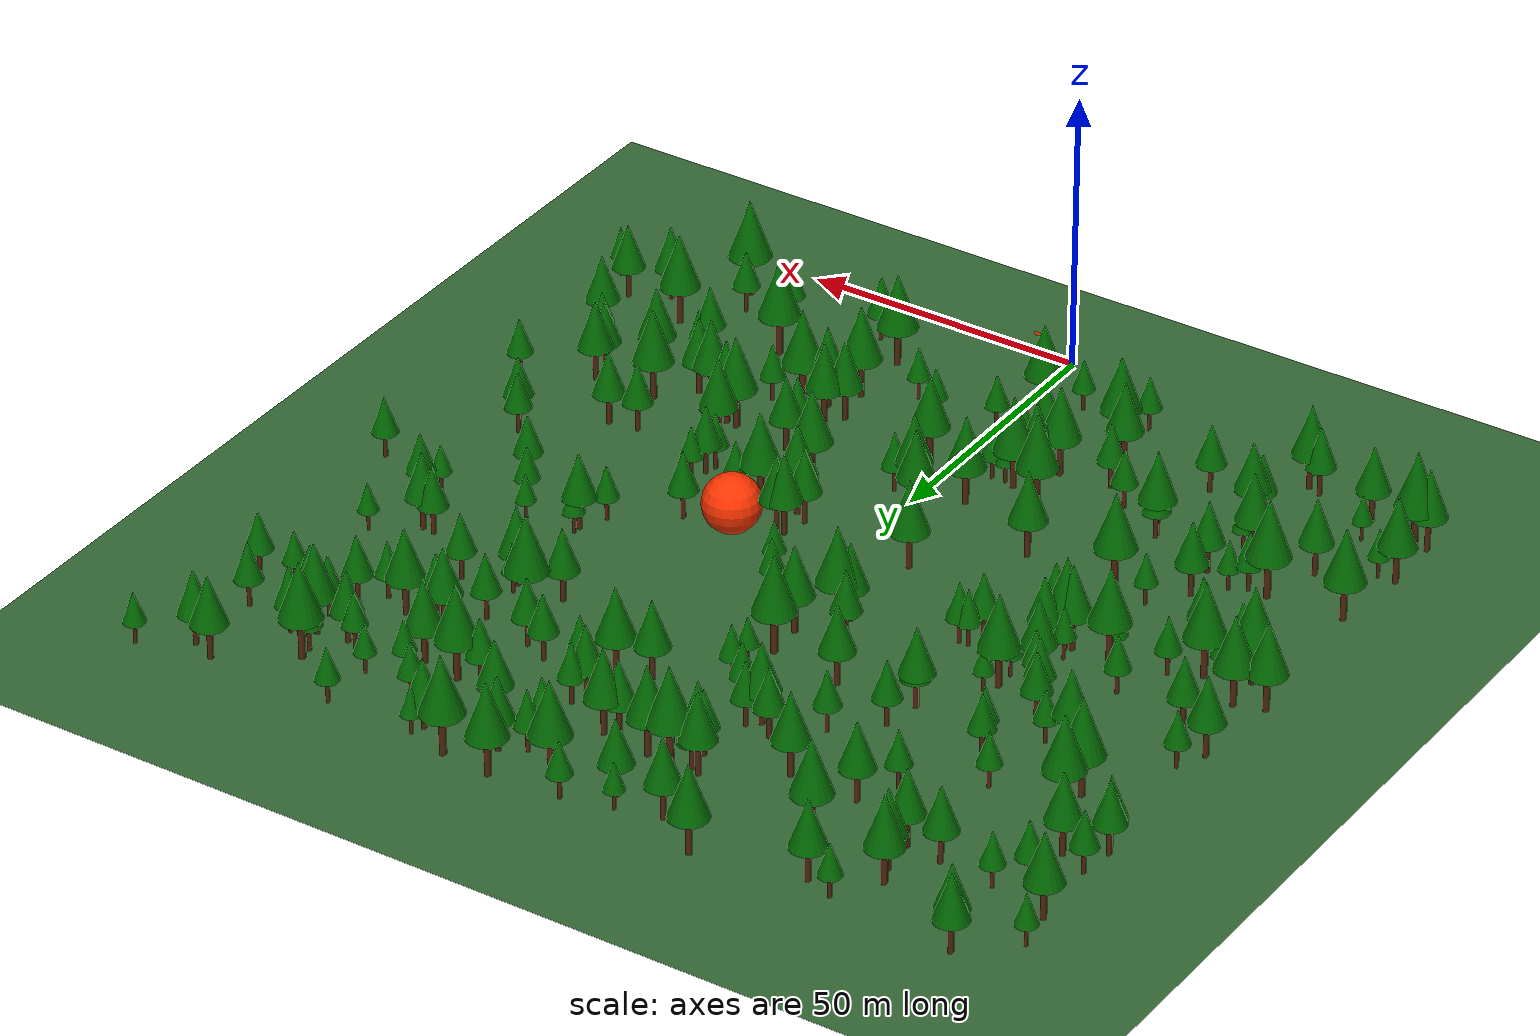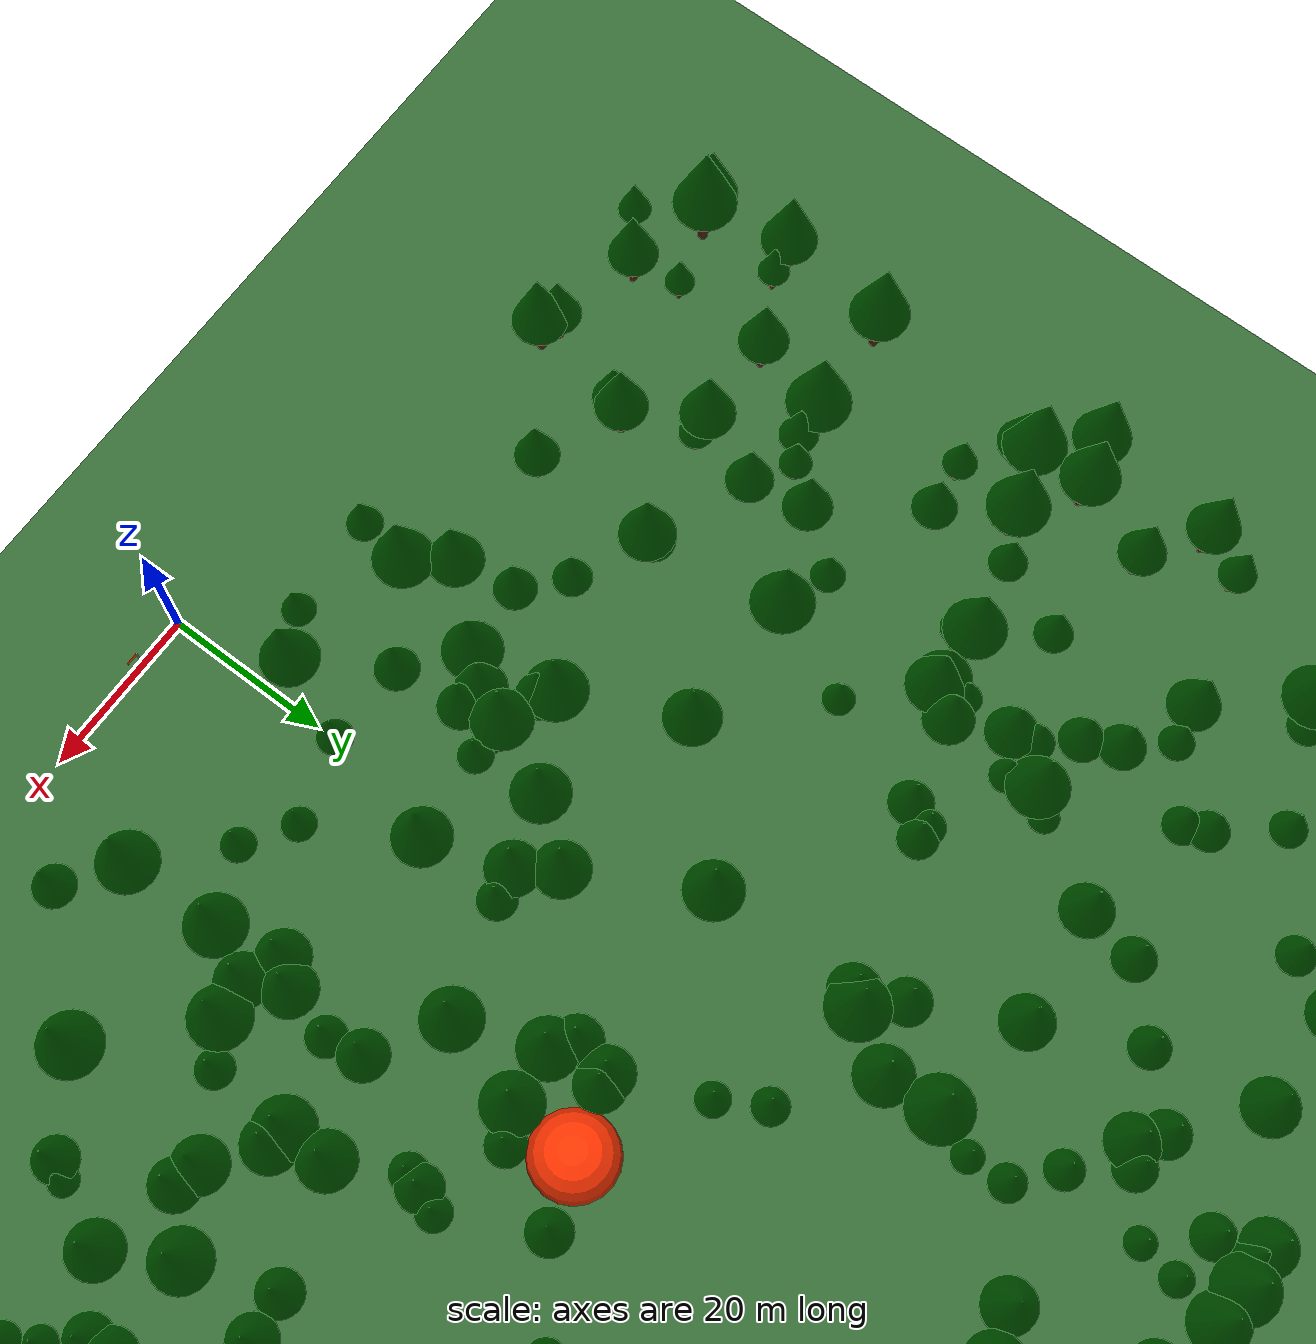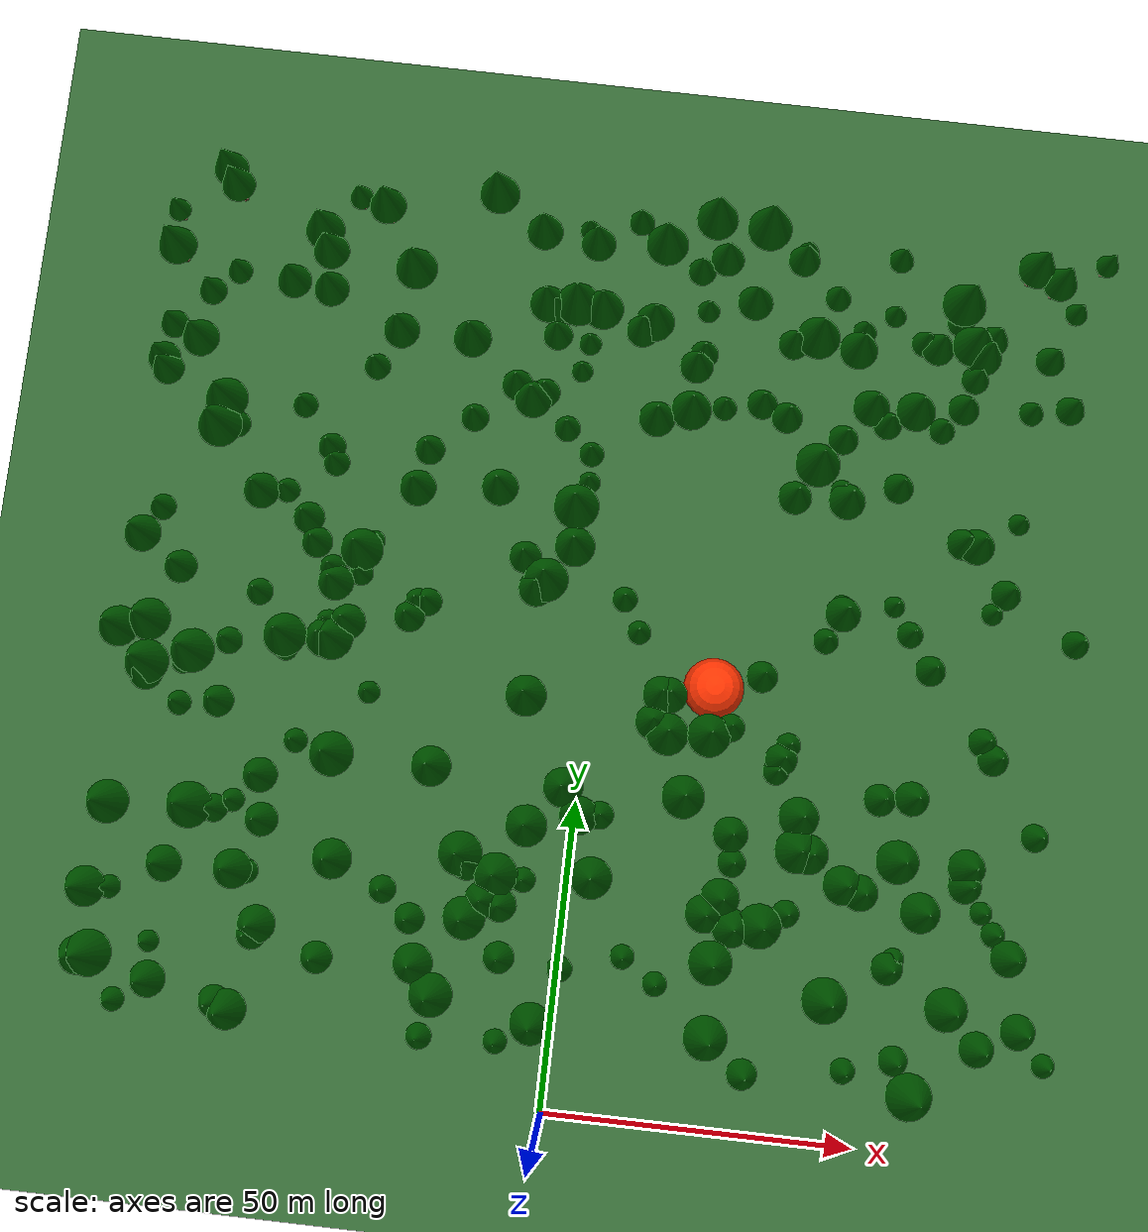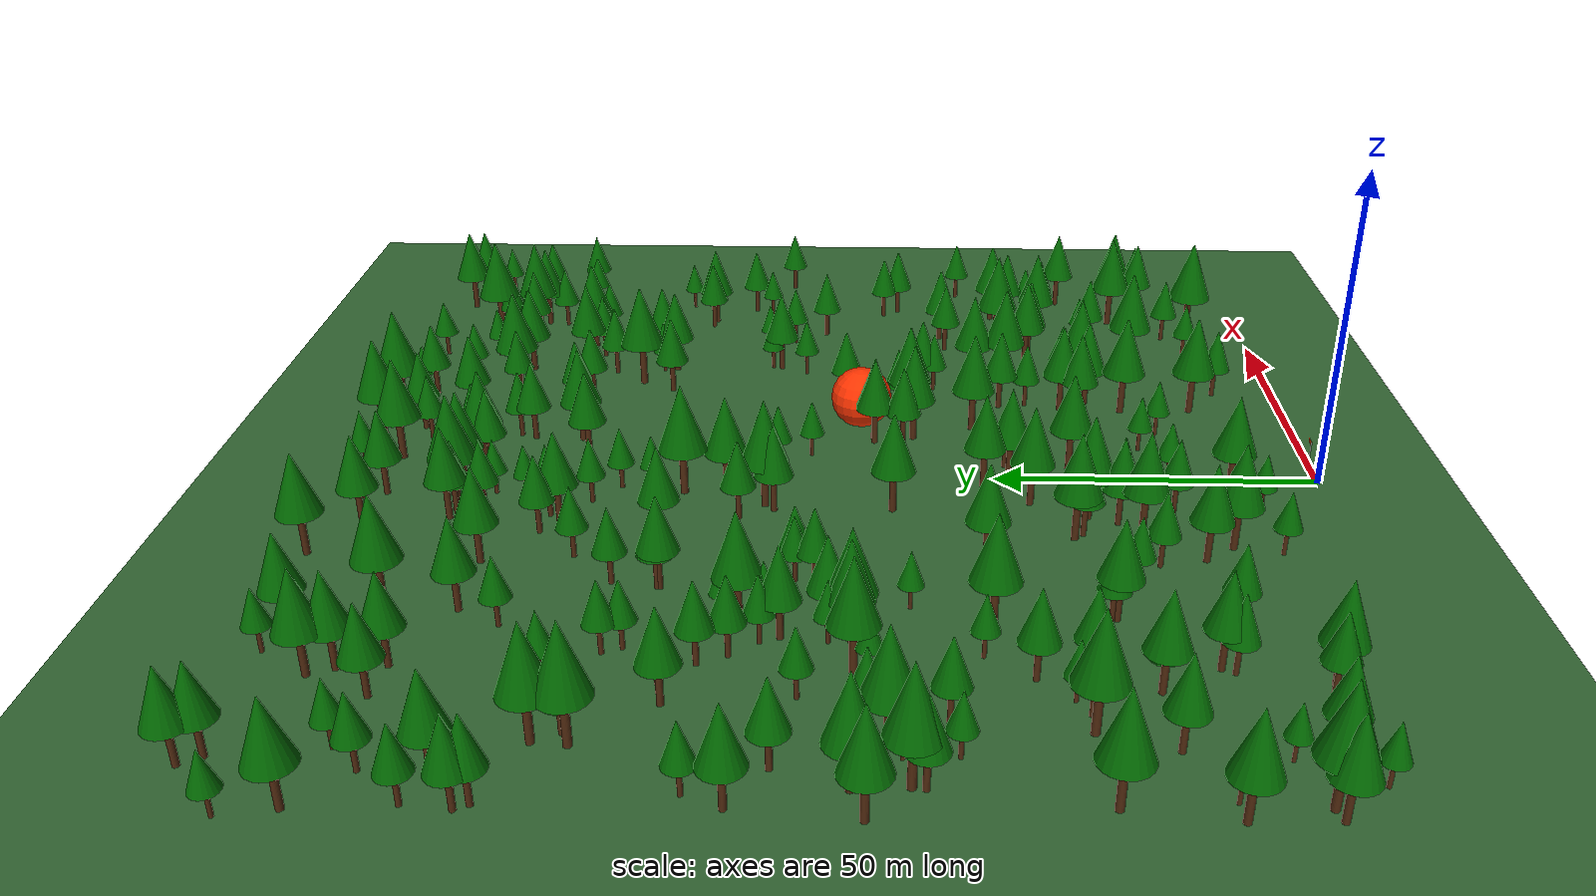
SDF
<sdf version="1.9">
 <world name="Forest_world">
  <physics type="ode"><max_step_size>0.004</max_step_size><real_time_factor>1.0</real_time_factor></physics>
  <plugin name="gz::sim::systems::Physics" filename="gz-sim-physics-system"/>
  <plugin name="gz::sim::systems::SceneBroadcaster" filename="gz-sim-scene-broadcaster-system"/>
  <plugin name="gz::sim::systems::UserCommands" filename="gz-sim-user-commands-system"/>
  <plugin name="gz::sim::systems::Sensors" filename="gz-sim-sensors-system">
   <render_engine>ogre2</render_engine>
  </plugin>
  <plugin name="gz::sim::systems::Imu" filename="gz-sim-imu-system"/>
  <plugin name="gz::sim::systems::NavSat" filename="gz-sim-navsat-system"/>
  <plugin name="gz::sim::systems::Magnetometer" filename="gz-sim-magnetometer-system"/>
  <plugin name="gz::sim::systems::AirPressure" filename="gz-sim-air-pressure-system"/>
  <plugin name="gz::sim::systems::Contact" filename="gz-sim-contact-system"/>
  <plugin name="gz::sim::systems::WindEffects" filename="gz-sim-wind-effects-system">
   <force_approximation_scaling_factor>1</force_approximation_scaling_factor>
   <linear_velocity>0 0 0</linear_velocity>
  </plugin>
  <wind><linear_velocity>0 0 0</linear_velocity></wind>
  <spherical_coordinates>
   <surface_model>EARTH_WGS84</surface_model>
   <world_frame_orientation>ENU</world_frame_orientation>
   <latitude_deg>47.397742</latitude_deg>
   <longitude_deg>8.545594</longitude_deg>
   <elevation>0</elevation>
   <heading_deg>0</heading_deg>
  </spherical_coordinates>
  <light type="directional" name="sun">
   <pose>0 0 10 0 0 0</pose>
   <diffuse>0.8 0.8 0.8 1</diffuse>
   <specular>0.2 0.2 0.2 1</specular>
   <direction>-0.5 0.1 -0.9</direction>
  </light>
  <model name="ground_plane">
   <static>true</static>
   <link name="link">
    <collision name="collision">
     <geometry><plane><normal>0 0 1</normal><size>500 500</size></plane></geometry>
    </collision>
    <visual name="visual">
     <geometry><plane><normal>0 0 1</normal><size>500 500</size></plane></geometry>
     <material><ambient>0.2 0.4 0.2 1</ambient><diffuse>0.2 0.4 0.2 1</diffuse></material>
    </visual>
   </link>
  </model>
  <model name="windsock_flag">
   <pose>6 0 0 0 0 0</pose>
   <link name="pole">
    <pose>0 0 2 0 0 0</pose>
    <inertial><mass>100</mass><inertia><ixx>1</ixx><iyy>1</iyy><izz>1</izz></inertia></inertial>
    <collision name="col">
     <geometry><cylinder><radius>0.08</radius><length>4</length></cylinder></geometry>
    </collision>
    <visual name="vis">
     <geometry><cylinder><radius>0.08</radius><length>4</length></cylinder></geometry>
     <material><ambient>0.8 0.8 0.8 1</ambient><diffuse>0.8 0.8 0.8 1</diffuse></material>
    </visual>
   </link>
   <joint name="fixed_to_ground" type="fixed"><parent>world</parent><child>pole</child></joint>
   <link name="fabric">
    <pose>0.75 0 3.8 0 0 0</pose>
    <enable_wind>true</enable_wind>
    <inertial><mass>0.15</mass><inertia><ixx>0.01</ixx><iyy>0.01</iyy><izz>0.01</izz></inertia></inertial>
    <collision name="col"><geometry><box><size>1.5 0.02 0.6</size></box></geometry></collision>
    <visual name="vis">
     <geometry><box><size>1.5 0.02 0.6</size></box></geometry>
     <material><ambient>1.0 0.3 0.0 1</ambient><diffuse>1.0 0.3 0.0 1</diffuse></material>
    </visual>
   </link>
   <joint name="hinge" type="universal">
    <parent>pole</parent>
    <child>fabric</child>
    <pose>-0.75 0 0 0 0 0</pose>
    <axis><xyz>0 0 1</xyz></axis>
    <axis2><xyz>0 1 0</xyz></axis2>
   </joint>
  </model>
  <model name="tree_0">
   <static>true</static>
   <pose>-8.42 110.98 0 0 0 0</pose>
   <link name="link">
    <collision name="trunk_col">
     <pose>0 0 2.21 0 0 0</pose>
     <geometry><cylinder><radius>0.35</radius><length>4.43</length></cylinder></geometry>
    </collision>
    <visual name="trunk_vis">
     <pose>0 0 2.21 0 0 0</pose>
     <geometry><cylinder><radius>0.35</radius><length>4.43</length></cylinder></geometry>
     <material><ambient>0.3 0.15 0.05 1</ambient><diffuse>0.3 0.15 0.05 1</diffuse></material>
    </visual>
    <collision name="leaves_col">
     <pose>0 0 7.53 0 0 0</pose>
     <geometry><cone><radius>2.21</radius><length>6.20</length></cone></geometry>
    </collision>
    <visual name="leaves_vis">
     <pose>0 0 7.53 0 0 0</pose>
     <geometry><cone><radius>2.21</radius><length>6.20</length></cone></geometry>
     <material><ambient>0.0 0.4 0.0 1</ambient><diffuse>0.0 0.4 0.0 1</diffuse></material>
    </visual>
   </link>
  </model>
  <model name="tree_1">
   <static>true</static>
   <pose>58.30 98.68 0 0 0 0</pose>
   <link name="link">
    <collision name="trunk_col">
     <pose>0 0 2.60 0 0 0</pose>
     <geometry><cylinder><radius>0.42</radius><length>5.20</length></cylinder></geometry>
    </collision>
    <visual name="trunk_vis">
     <pose>0 0 2.60 0 0 0</pose>
     <geometry><cylinder><radius>0.42</radius><length>5.20</length></cylinder></geometry>
     <material><ambient>0.3 0.15 0.05 1</ambient><diffuse>0.3 0.15 0.05 1</diffuse></material>
    </visual>
    <collision name="leaves_col">
     <pose>0 0 8.83 0 0 0</pose>
     <geometry><cone><radius>2.60</radius><length>7.27</length></cone></geometry>
    </collision>
    <visual name="leaves_vis">
     <pose>0 0 8.83 0 0 0</pose>
     <geometry><cone><radius>2.60</radius><length>7.27</length></cone></geometry>
     <material><ambient>0.0 0.4 0.0 1</ambient><diffuse>0.0 0.4 0.0 1</diffuse></material>
    </visual>
   </link>
  </model>
  <model name="tree_2">
   <static>true</static>
   <pose>-51.11 136.40 0 0 0 0</pose>
   <link name="link">
    <collision name="trunk_col">
     <pose>0 0 3.07 0 0 0</pose>
     <geometry><cylinder><radius>0.49</radius><length>6.15</length></cylinder></geometry>
    </collision>
    <visual name="trunk_vis">
     <pose>0 0 3.07 0 0 0</pose>
     <geometry><cylinder><radius>0.49</radius><length>6.15</length></cylinder></geometry>
     <material><ambient>0.3 0.15 0.05 1</ambient><diffuse>0.3 0.15 0.05 1</diffuse></material>
    </visual>
    <collision name="leaves_col">
     <pose>0 0 10.45 0 0 0</pose>
     <geometry><cone><radius>3.07</radius><length>8.60</length></cone></geometry>
    </collision>
    <visual name="leaves_vis">
     <pose>0 0 10.45 0 0 0</pose>
     <geometry><cone><radius>3.07</radius><length>8.60</length></cone></geometry>
     <material><ambient>0.0 0.4 0.0 1</ambient><diffuse>0.0 0.4 0.0 1</diffuse></material>
    </visual>
   </link>
  </model>
  <model name="tree_3">
   <static>true</static>
   <pose>53.28 30.68 0 0 0 0</pose>
   <link name="link">
    <collision name="trunk_col">
     <pose>0 0 1.76 0 0 0</pose>
     <geometry><cylinder><radius>0.28</radius><length>3.52</length></cylinder></geometry>
    </collision>
    <visual name="trunk_vis">
     <pose>0 0 1.76 0 0 0</pose>
     <geometry><cylinder><radius>0.28</radius><length>3.52</length></cylinder></geometry>
     <material><ambient>0.3 0.15 0.05 1</ambient><diffuse>0.3 0.15 0.05 1</diffuse></material>
    </visual>
    <collision name="leaves_col">
     <pose>0 0 5.98 0 0 0</pose>
     <geometry><cone><radius>1.76</radius><length>4.93</length></cone></geometry>
    </collision>
    <visual name="leaves_vis">
     <pose>0 0 5.98 0 0 0</pose>
     <geometry><cone><radius>1.76</radius><length>4.93</length></cone></geometry>
     <material><ambient>0.0 0.4 0.0 1</ambient><diffuse>0.0 0.4 0.0 1</diffuse></material>
    </visual>
   </link>
  </model>
  <model name="tree_4">
   <static>true</static>
   <pose>4.24 83.53 0 0 0 0</pose>
   <link name="link">
    <collision name="trunk_col">
     <pose>0 0 2.11 0 0 0</pose>
     <geometry><cylinder><radius>0.34</radius><length>4.22</length></cylinder></geometry>
    </collision>
    <visual name="trunk_vis">
     <pose>0 0 2.11 0 0 0</pose>
     <geometry><cylinder><radius>0.34</radius><length>4.22</length></cylinder></geometry>
     <material><ambient>0.3 0.15 0.05 1</ambient><diffuse>0.3 0.15 0.05 1</diffuse></material>
    </visual>
    <collision name="leaves_col">
     <pose>0 0 7.18 0 0 0</pose>
     <geometry><cone><radius>2.11</radius><length>5.91</length></cone></geometry>
    </collision>
    <visual name="leaves_vis">
     <pose>0 0 7.18 0 0 0</pose>
     <geometry><cone><radius>2.11</radius><length>5.91</length></cone></geometry>
     <material><ambient>0.0 0.4 0.0 1</ambient><diffuse>0.0 0.4 0.0 1</diffuse></material>
    </visual>
   </link>
  </model>
  <model name="tree_5">
   <static>true</static>
   <pose>46.70 12.42 0 0 0 0</pose>
   <link name="link">
    <collision name="trunk_col">
     <pose>0 0 2.06 0 0 0</pose>
     <geometry><cylinder><radius>0.33</radius><length>4.13</length></cylinder></geometry>
    </collision>
    <visual name="trunk_vis">
     <pose>0 0 2.06 0 0 0</pose>
     <geometry><cylinder><radius>0.33</radius><length>4.13</length></cylinder></geometry>
     <material><ambient>0.3 0.15 0.05 1</ambient><diffuse>0.3 0.15 0.05 1</diffuse></material>
    </visual>
    <collision name="leaves_col">
     <pose>0 0 7.01 0 0 0</pose>
     <geometry><cone><radius>2.06</radius><length>5.78</length></cone></geometry>
    </collision>
    <visual name="leaves_vis">
     <pose>0 0 7.01 0 0 0</pose>
     <geometry><cone><radius>2.06</radius><length>5.78</length></cone></geometry>
     <material><ambient>0.0 0.4 0.0 1</ambient><diffuse>0.0 0.4 0.0 1</diffuse></material>
    </visual>
   </link>
  </model>
  <model name="tree_6">
   <static>true</static>
   <pose>31.08 33.52 0 0 0 0</pose>
   <link name="link">
    <collision name="trunk_col">
     <pose>0 0 3.58 0 0 0</pose>
     <geometry><cylinder><radius>0.57</radius><length>7.17</length></cylinder></geometry>
    </collision>
    <visual name="trunk_vis">
     <pose>0 0 3.58 0 0 0</pose>
     <geometry><cylinder><radius>0.57</radius><length>7.17</length></cylinder></geometry>
     <material><ambient>0.3 0.15 0.05 1</ambient><diffuse>0.3 0.15 0.05 1</diffuse></material>
    </visual>
    <collision name="leaves_col">
     <pose>0 0 12.19 0 0 0</pose>
     <geometry><cone><radius>3.58</radius><length>10.04</length></cone></geometry>
    </collision>
    <visual name="leaves_vis">
     <pose>0 0 12.19 0 0 0</pose>
     <geometry><cone><radius>3.58</radius><length>10.04</length></cone></geometry>
     <material><ambient>0.0 0.4 0.0 1</ambient><diffuse>0.0 0.4 0.0 1</diffuse></material>
    </visual>
   </link>
  </model>
  <model name="tree_7">
   <static>true</static>
   <pose>-5.32 97.40 0 0 0 0</pose>
   <link name="link">
    <collision name="trunk_col">
     <pose>0 0 3.75 0 0 0</pose>
     <geometry><cylinder><radius>0.60</radius><length>7.50</length></cylinder></geometry>
    </collision>
    <visual name="trunk_vis">
     <pose>0 0 3.75 0 0 0</pose>
     <geometry><cylinder><radius>0.60</radius><length>7.50</length></cylinder></geometry>
     <material><ambient>0.3 0.15 0.05 1</ambient><diffuse>0.3 0.15 0.05 1</diffuse></material>
    </visual>
    <collision name="leaves_col">
     <pose>0 0 12.75 0 0 0</pose>
     <geometry><cone><radius>3.75</radius><length>10.50</length></cone></geometry>
    </collision>
    <visual name="leaves_vis">
     <pose>0 0 12.75 0 0 0</pose>
     <geometry><cone><radius>3.75</radius><length>10.50</length></cone></geometry>
     <material><ambient>0.0 0.4 0.0 1</ambient><diffuse>0.0 0.4 0.0 1</diffuse></material>
    </visual>
   </link>
  </model>
  <model name="tree_8">
   <static>true</static>
   <pose>-43.70 74.55 0 0 0 0</pose>
   <link name="link">
    <collision name="trunk_col">
     <pose>0 0 1.99 0 0 0</pose>
     <geometry><cylinder><radius>0.32</radius><length>3.98</length></cylinder></geometry>
    </collision>
    <visual name="trunk_vis">
     <pose>0 0 1.99 0 0 0</pose>
     <geometry><cylinder><radius>0.32</radius><length>3.98</length></cylinder></geometry>
     <material><ambient>0.3 0.15 0.05 1</ambient><diffuse>0.3 0.15 0.05 1</diffuse></material>
    </visual>
    <collision name="leaves_col">
     <pose>0 0 6.77 0 0 0</pose>
     <geometry><cone><radius>1.99</radius><length>5.57</length></cone></geometry>
    </collision>
    <visual name="leaves_vis">
     <pose>0 0 6.77 0 0 0</pose>
     <geometry><cone><radius>1.99</radius><length>5.57</length></cone></geometry>
     <material><ambient>0.0 0.4 0.0 1</ambient><diffuse>0.0 0.4 0.0 1</diffuse></material>
    </visual>
   </link>
  </model>
  <model name="tree_9">
   <static>true</static>
   <pose>-39.32 83.02 0 0 0 0</pose>
   <link name="link">
    <collision name="trunk_col">
     <pose>0 0 1.98 0 0 0</pose>
     <geometry><cylinder><radius>0.32</radius><length>3.95</length></cylinder></geometry>
    </collision>
    <visual name="trunk_vis">
     <pose>0 0 1.98 0 0 0</pose>
     <geometry><cylinder><radius>0.32</radius><length>3.95</length></cylinder></geometry>
     <material><ambient>0.3 0.15 0.05 1</ambient><diffuse>0.3 0.15 0.05 1</diffuse></material>
    </visual>
    <collision name="leaves_col">
     <pose>0 0 6.72 0 0 0</pose>
     <geometry><cone><radius>1.98</radius><length>5.54</length></cone></geometry>
    </collision>
    <visual name="leaves_vis">
     <pose>0 0 6.72 0 0 0</pose>
     <geometry><cone><radius>1.98</radius><length>5.54</length></cone></geometry>
     <material><ambient>0.0 0.4 0.0 1</ambient><diffuse>0.0 0.4 0.0 1</diffuse></material>
    </visual>
   </link>
  </model>
  <model name="tree_10">
   <static>true</static>
   <pose>51.21 82.89 0 0 0 0</pose>
   <link name="link">
    <collision name="trunk_col">
     <pose>0 0 2.19 0 0 0</pose>
     <geometry><cylinder><radius>0.35</radius><length>4.38</length></cylinder></geometry>
    </collision>
    <visual name="trunk_vis">
     <pose>0 0 2.19 0 0 0</pose>
     <geometry><cylinder><radius>0.35</radius><length>4.38</length></cylinder></geometry>
     <material><ambient>0.3 0.15 0.05 1</ambient><diffuse>0.3 0.15 0.05 1</diffuse></material>
    </visual>
    <collision name="leaves_col">
     <pose>0 0 7.45 0 0 0</pose>
     <geometry><cone><radius>2.19</radius><length>6.14</length></cone></geometry>
    </collision>
    <visual name="leaves_vis">
     <pose>0 0 7.45 0 0 0</pose>
     <geometry><cone><radius>2.19</radius><length>6.14</length></cone></geometry>
     <material><ambient>0.0 0.4 0.0 1</ambient><diffuse>0.0 0.4 0.0 1</diffuse></material>
    </visual>
   </link>
  </model>
  <model name="tree_11">
   <static>true</static>
   <pose>-41.16 118.00 0 0 0 0</pose>
   <link name="link">
    <collision name="trunk_col">
     <pose>0 0 2.25 0 0 0</pose>
     <geometry><cylinder><radius>0.36</radius><length>4.49</length></cylinder></geometry>
    </collision>
    <visual name="trunk_vis">
     <pose>0 0 2.25 0 0 0</pose>
     <geometry><cylinder><radius>0.36</radius><length>4.49</length></cylinder></geometry>
     <material><ambient>0.3 0.15 0.05 1</ambient><diffuse>0.3 0.15 0.05 1</diffuse></material>
    </visual>
    <collision name="leaves_col">
     <pose>0 0 7.64 0 0 0</pose>
     <geometry><cone><radius>2.25</radius><length>6.29</length></cone></geometry>
    </collision>
    <visual name="leaves_vis">
     <pose>0 0 7.64 0 0 0</pose>
     <geometry><cone><radius>2.25</radius><length>6.29</length></cone></geometry>
     <material><ambient>0.0 0.4 0.0 1</ambient><diffuse>0.0 0.4 0.0 1</diffuse></material>
    </visual>
   </link>
  </model>
  <model name="tree_12">
   <static>true</static>
   <pose>-63.00 105.64 0 0 0 0</pose>
   <link name="link">
    <collision name="trunk_col">
     <pose>0 0 2.24 0 0 0</pose>
     <geometry><cylinder><radius>0.36</radius><length>4.47</length></cylinder></geometry>
    </collision>
    <visual name="trunk_vis">
     <pose>0 0 2.24 0 0 0</pose>
     <geometry><cylinder><radius>0.36</radius><length>4.47</length></cylinder></geometry>
     <material><ambient>0.3 0.15 0.05 1</ambient><diffuse>0.3 0.15 0.05 1</diffuse></material>
    </visual>
    <collision name="leaves_col">
     <pose>0 0 7.61 0 0 0</pose>
     <geometry><cone><radius>2.24</radius><length>6.26</length></cone></geometry>
    </collision>
    <visual name="leaves_vis">
     <pose>0 0 7.61 0 0 0</pose>
     <geometry><cone><radius>2.24</radius><length>6.26</length></cone></geometry>
     <material><ambient>0.0 0.4 0.0 1</ambient><diffuse>0.0 0.4 0.0 1</diffuse></material>
    </visual>
   </link>
  </model>
  <model name="tree_13">
   <static>true</static>
   <pose>60.52 133.61 0 0 0 0</pose>
   <link name="link">
    <collision name="trunk_col">
     <pose>0 0 2.55 0 0 0</pose>
     <geometry><cylinder><radius>0.41</radius><length>5.10</length></cylinder></geometry>
    </collision>
    <visual name="trunk_vis">
     <pose>0 0 2.55 0 0 0</pose>
     <geometry><cylinder><radius>0.41</radius><length>5.10</length></cylinder></geometry>
     <material><ambient>0.3 0.15 0.05 1</ambient><diffuse>0.3 0.15 0.05 1</diffuse></material>
    </visual>
    <collision name="leaves_col">
     <pose>0 0 8.67 0 0 0</pose>
     <geometry><cone><radius>2.55</radius><length>7.14</length></cone></geometry>
    </collision>
    <visual name="leaves_vis">
     <pose>0 0 8.67 0 0 0</pose>
     <geometry><cone><radius>2.55</radius><length>7.14</length></cone></geometry>
     <material><ambient>0.0 0.4 0.0 1</ambient><diffuse>0.0 0.4 0.0 1</diffuse></material>
    </visual>
   </link>
  </model>
  <model name="tree_14">
   <static>true</static>
   <pose>31.30 130.26 0 0 0 0</pose>
   <link name="link">
    <collision name="trunk_col">
     <pose>0 0 3.61 0 0 0</pose>
     <geometry><cylinder><radius>0.58</radius><length>7.22</length></cylinder></geometry>
    </collision>
    <visual name="trunk_vis">
     <pose>0 0 3.61 0 0 0</pose>
     <geometry><cylinder><radius>0.58</radius><length>7.22</length></cylinder></geometry>
     <material><ambient>0.3 0.15 0.05 1</ambient><diffuse>0.3 0.15 0.05 1</diffuse></material>
    </visual>
    <collision name="leaves_col">
     <pose>0 0 12.27 0 0 0</pose>
     <geometry><cone><radius>3.61</radius><length>10.10</length></cone></geometry>
    </collision>
    <visual name="leaves_vis">
     <pose>0 0 12.27 0 0 0</pose>
     <geometry><cone><radius>3.61</radius><length>10.10</length></cone></geometry>
     <material><ambient>0.0 0.4 0.0 1</ambient><diffuse>0.0 0.4 0.0 1</diffuse></material>
    </visual>
   </link>
  </model>
  <model name="tree_15">
   <static>true</static>
   <pose>-12.96 32.70 0 0 0 0</pose>
   <link name="link">
    <collision name="trunk_col">
     <pose>0 0 2.96 0 0 0</pose>
     <geometry><cylinder><radius>0.47</radius><length>5.92</length></cylinder></geometry>
    </collision>
    <visual name="trunk_vis">
     <pose>0 0 2.96 0 0 0</pose>
     <geometry><cylinder><radius>0.47</radius><length>5.92</length></cylinder></geometry>
     <material><ambient>0.3 0.15 0.05 1</ambient><diffuse>0.3 0.15 0.05 1</diffuse></material>
    </visual>
    <collision name="leaves_col">
     <pose>0 0 10.06 0 0 0</pose>
     <geometry><cone><radius>2.96</radius><length>8.29</length></cone></geometry>
    </collision>
    <visual name="leaves_vis">
     <pose>0 0 10.06 0 0 0</pose>
     <geometry><cone><radius>2.96</radius><length>8.29</length></cone></geometry>
     <material><ambient>0.0 0.4 0.0 1</ambient><diffuse>0.0 0.4 0.0 1</diffuse></material>
    </visual>
   </link>
  </model>
  <model name="tree_16">
   <static>true</static>
   <pose>-66.06 58.57 0 0 0 0</pose>
   <link name="link">
    <collision name="trunk_col">
     <pose>0 0 2.02 0 0 0</pose>
     <geometry><cylinder><radius>0.32</radius><length>4.04</length></cylinder></geometry>
    </collision>
    <visual name="trunk_vis">
     <pose>0 0 2.02 0 0 0</pose>
     <geometry><cylinder><radius>0.32</radius><length>4.04</length></cylinder></geometry>
     <material><ambient>0.3 0.15 0.05 1</ambient><diffuse>0.3 0.15 0.05 1</diffuse></material>
    </visual>
    <collision name="leaves_col">
     <pose>0 0 6.87 0 0 0</pose>
     <geometry><cone><radius>2.02</radius><length>5.66</length></cone></geometry>
    </collision>
    <visual name="leaves_vis">
     <pose>0 0 6.87 0 0 0</pose>
     <geometry><cone><radius>2.02</radius><length>5.66</length></cone></geometry>
     <material><ambient>0.0 0.4 0.0 1</ambient><diffuse>0.0 0.4 0.0 1</diffuse></material>
    </visual>
   </link>
  </model>
  <model name="tree_17">
   <static>true</static>
   <pose>-78.15 141.54 0 0 0 0</pose>
   <link name="link">
    <collision name="trunk_col">
     <pose>0 0 1.96 0 0 0</pose>
     <geometry><cylinder><radius>0.31</radius><length>3.92</length></cylinder></geometry>
    </collision>
    <visual name="trunk_vis">
     <pose>0 0 1.96 0 0 0</pose>
     <geometry><cylinder><radius>0.31</radius><length>3.92</length></cylinder></geometry>
     <material><ambient>0.3 0.15 0.05 1</ambient><diffuse>0.3 0.15 0.05 1</diffuse></material>
    </visual>
    <collision name="leaves_col">
     <pose>0 0 6.67 0 0 0</pose>
     <geometry><cone><radius>1.96</radius><length>5.49</length></cone></geometry>
    </collision>
    <visual name="leaves_vis">
     <pose>0 0 6.67 0 0 0</pose>
     <geometry><cone><radius>1.96</radius><length>5.49</length></cone></geometry>
     <material><ambient>0.0 0.4 0.0 1</ambient><diffuse>0.0 0.4 0.0 1</diffuse></material>
    </visual>
   </link>
  </model>
  <model name="tree_18">
   <static>true</static>
   <pose>-75.57 113.54 0 0 0 0</pose>
   <link name="link">
    <collision name="trunk_col">
     <pose>0 0 2.69 0 0 0</pose>
     <geometry><cylinder><radius>0.43</radius><length>5.37</length></cylinder></geometry>
    </collision>
    <visual name="trunk_vis">
     <pose>0 0 2.69 0 0 0</pose>
     <geometry><cylinder><radius>0.43</radius><length>5.37</length></cylinder></geometry>
     <material><ambient>0.3 0.15 0.05 1</ambient><diffuse>0.3 0.15 0.05 1</diffuse></material>
    </visual>
    <collision name="leaves_col">
     <pose>0 0 9.14 0 0 0</pose>
     <geometry><cone><radius>2.69</radius><length>7.52</length></cone></geometry>
    </collision>
    <visual name="leaves_vis">
     <pose>0 0 9.14 0 0 0</pose>
     <geometry><cone><radius>2.69</radius><length>7.52</length></cone></geometry>
     <material><ambient>0.0 0.4 0.0 1</ambient><diffuse>0.0 0.4 0.0 1</diffuse></material>
    </visual>
   </link>
  </model>
  <model name="tree_19">
   <static>true</static>
   <pose>-3.94 107.13 0 0 0 0</pose>
   <link name="link">
    <collision name="trunk_col">
     <pose>0 0 2.10 0 0 0</pose>
     <geometry><cylinder><radius>0.34</radius><length>4.20</length></cylinder></geometry>
    </collision>
    <visual name="trunk_vis">
     <pose>0 0 2.10 0 0 0</pose>
     <geometry><cylinder><radius>0.34</radius><length>4.20</length></cylinder></geometry>
     <material><ambient>0.3 0.15 0.05 1</ambient><diffuse>0.3 0.15 0.05 1</diffuse></material>
    </visual>
    <collision name="leaves_col">
     <pose>0 0 7.14 0 0 0</pose>
     <geometry><cone><radius>2.10</radius><length>5.88</length></cone></geometry>
    </collision>
    <visual name="leaves_vis">
     <pose>0 0 7.14 0 0 0</pose>
     <geometry><cone><radius>2.10</radius><length>5.88</length></cone></geometry>
     <material><ambient>0.0 0.4 0.0 1</ambient><diffuse>0.0 0.4 0.0 1</diffuse></material>
    </visual>
   </link>
  </model>
  <model name="tree_20">
   <static>true</static>
   <pose>56.82 10.01 0 0 0 0</pose>
   <link name="link">
    <collision name="trunk_col">
     <pose>0 0 3.73 0 0 0</pose>
     <geometry><cylinder><radius>0.60</radius><length>7.46</length></cylinder></geometry>
    </collision>
    <visual name="trunk_vis">
     <pose>0 0 3.73 0 0 0</pose>
     <geometry><cylinder><radius>0.60</radius><length>7.46</length></cylinder></geometry>
     <material><ambient>0.3 0.15 0.05 1</ambient><diffuse>0.3 0.15 0.05 1</diffuse></material>
    </visual>
    <collision name="leaves_col">
     <pose>0 0 12.69 0 0 0</pose>
     <geometry><cone><radius>3.73</radius><length>10.45</length></cone></geometry>
    </collision>
    <visual name="leaves_vis">
     <pose>0 0 12.69 0 0 0</pose>
     <geometry><cone><radius>3.73</radius><length>10.45</length></cone></geometry>
     <material><ambient>0.0 0.4 0.0 1</ambient><diffuse>0.0 0.4 0.0 1</diffuse></material>
    </visual>
   </link>
  </model>
  <model name="tree_21">
   <static>true</static>
   <pose>38.01 105.65 0 0 0 0</pose>
   <link name="link">
    <collision name="trunk_col">
     <pose>0 0 1.95 0 0 0</pose>
     <geometry><cylinder><radius>0.31</radius><length>3.90</length></cylinder></geometry>
    </collision>
    <visual name="trunk_vis">
     <pose>0 0 1.95 0 0 0</pose>
     <geometry><cylinder><radius>0.31</radius><length>3.90</length></cylinder></geometry>
     <material><ambient>0.3 0.15 0.05 1</ambient><diffuse>0.3 0.15 0.05 1</diffuse></material>
    </visual>
    <collision name="leaves_col">
     <pose>0 0 6.62 0 0 0</pose>
     <geometry><cone><radius>1.95</radius><length>5.45</length></cone></geometry>
    </collision>
    <visual name="leaves_vis">
     <pose>0 0 6.62 0 0 0</pose>
     <geometry><cone><radius>1.95</radius><length>5.45</length></cone></geometry>
     <material><ambient>0.0 0.4 0.0 1</ambient><diffuse>0.0 0.4 0.0 1</diffuse></material>
    </visual>
   </link>
  </model>
  <model name="tree_22">
   <static>true</static>
   <pose>23.62 64.46 0 0 0 0</pose>
   <link name="link">
    <collision name="trunk_col">
     <pose>0 0 2.33 0 0 0</pose>
     <geometry><cylinder><radius>0.37</radius><length>4.66</length></cylinder></geometry>
    </collision>
    <visual name="trunk_vis">
     <pose>0 0 2.33 0 0 0</pose>
     <geometry><cylinder><radius>0.37</radius><length>4.66</length></cylinder></geometry>
     <material><ambient>0.3 0.15 0.05 1</ambient><diffuse>0.3 0.15 0.05 1</diffuse></material>
    </visual>
    <collision name="leaves_col">
     <pose>0 0 7.92 0 0 0</pose>
     <geometry><cone><radius>2.33</radius><length>6.52</length></cone></geometry>
    </collision>
    <visual name="leaves_vis">
     <pose>0 0 7.92 0 0 0</pose>
     <geometry><cone><radius>2.33</radius><length>6.52</length></cone></geometry>
     <material><ambient>0.0 0.4 0.0 1</ambient><diffuse>0.0 0.4 0.0 1</diffuse></material>
    </visual>
   </link>
  </model>
  <model name="tree_23">
   <static>true</static>
   <pose>-9.40 23.94 0 0 0 0</pose>
   <link name="link">
    <collision name="trunk_col">
     <pose>0 0 2.56 0 0 0</pose>
     <geometry><cylinder><radius>0.41</radius><length>5.13</length></cylinder></geometry>
    </collision>
    <visual name="trunk_vis">
     <pose>0 0 2.56 0 0 0</pose>
     <geometry><cylinder><radius>0.41</radius><length>5.13</length></cylinder></geometry>
     <material><ambient>0.3 0.15 0.05 1</ambient><diffuse>0.3 0.15 0.05 1</diffuse></material>
    </visual>
    <collision name="leaves_col">
     <pose>0 0 8.71 0 0 0</pose>
     <geometry><cone><radius>2.56</radius><length>7.18</length></cone></geometry>
    </collision>
    <visual name="leaves_vis">
     <pose>0 0 8.71 0 0 0</pose>
     <geometry><cone><radius>2.56</radius><length>7.18</length></cone></geometry>
     <material><ambient>0.0 0.4 0.0 1</ambient><diffuse>0.0 0.4 0.0 1</diffuse></material>
    </visual>
   </link>
  </model>
  <model name="tree_24">
   <static>true</static>
   <pose>-3.13 14.43 0 0 0 0</pose>
   <link name="link">
    <collision name="trunk_col">
     <pose>0 0 3.37 0 0 0</pose>
     <geometry><cylinder><radius>0.54</radius><length>6.75</length></cylinder></geometry>
    </collision>
    <visual name="trunk_vis">
     <pose>0 0 3.37 0 0 0</pose>
     <geometry><cylinder><radius>0.54</radius><length>6.75</length></cylinder></geometry>
     <material><ambient>0.3 0.15 0.05 1</ambient><diffuse>0.3 0.15 0.05 1</diffuse></material>
    </visual>
    <collision name="leaves_col">
     <pose>0 0 11.47 0 0 0</pose>
     <geometry><cone><radius>3.37</radius><length>9.45</length></cone></geometry>
    </collision>
    <visual name="leaves_vis">
     <pose>0 0 11.47 0 0 0</pose>
     <geometry><cone><radius>3.37</radius><length>9.45</length></cone></geometry>
     <material><ambient>0.0 0.4 0.0 1</ambient><diffuse>0.0 0.4 0.0 1</diffuse></material>
    </visual>
   </link>
  </model>
  <model name="tree_25">
   <static>true</static>
   <pose>74.31 140.23 0 0 0 0</pose>
   <link name="link">
    <collision name="trunk_col">
     <pose>0 0 1.88 0 0 0</pose>
     <geometry><cylinder><radius>0.30</radius><length>3.75</length></cylinder></geometry>
    </collision>
    <visual name="trunk_vis">
     <pose>0 0 1.88 0 0 0</pose>
     <geometry><cylinder><radius>0.30</radius><length>3.75</length></cylinder></geometry>
     <material><ambient>0.3 0.15 0.05 1</ambient><diffuse>0.3 0.15 0.05 1</diffuse></material>
    </visual>
    <collision name="leaves_col">
     <pose>0 0 6.38 0 0 0</pose>
     <geometry><cone><radius>1.88</radius><length>5.25</length></cone></geometry>
    </collision>
    <visual name="leaves_vis">
     <pose>0 0 6.38 0 0 0</pose>
     <geometry><cone><radius>1.88</radius><length>5.25</length></cone></geometry>
     <material><ambient>0.0 0.4 0.0 1</ambient><diffuse>0.0 0.4 0.0 1</diffuse></material>
    </visual>
   </link>
  </model>
  <model name="tree_26">
   <static>true</static>
   <pose>-76.75 134.41 0 0 0 0</pose>
   <link name="link">
    <collision name="trunk_col">
     <pose>0 0 3.26 0 0 0</pose>
     <geometry><cylinder><radius>0.52</radius><length>6.52</length></cylinder></geometry>
    </collision>
    <visual name="trunk_vis">
     <pose>0 0 3.26 0 0 0</pose>
     <geometry><cylinder><radius>0.52</radius><length>6.52</length></cylinder></geometry>
     <material><ambient>0.3 0.15 0.05 1</ambient><diffuse>0.3 0.15 0.05 1</diffuse></material>
    </visual>
    <collision name="leaves_col">
     <pose>0 0 11.08 0 0 0</pose>
     <geometry><cone><radius>3.26</radius><length>9.13</length></cone></geometry>
    </collision>
    <visual name="leaves_vis">
     <pose>0 0 11.08 0 0 0</pose>
     <geometry><cone><radius>3.26</radius><length>9.13</length></cone></geometry>
     <material><ambient>0.0 0.4 0.0 1</ambient><diffuse>0.0 0.4 0.0 1</diffuse></material>
    </visual>
   </link>
  </model>
  <model name="tree_27">
   <static>true</static>
   <pose>-42.20 71.46 0 0 0 0</pose>
   <link name="link">
    <collision name="trunk_col">
     <pose>0 0 3.43 0 0 0</pose>
     <geometry><cylinder><radius>0.55</radius><length>6.86</length></cylinder></geometry>
    </collision>
    <visual name="trunk_vis">
     <pose>0 0 3.43 0 0 0</pose>
     <geometry><cylinder><radius>0.55</radius><length>6.86</length></cylinder></geometry>
     <material><ambient>0.3 0.15 0.05 1</ambient><diffuse>0.3 0.15 0.05 1</diffuse></material>
    </visual>
    <collision name="leaves_col">
     <pose>0 0 11.65 0 0 0</pose>
     <geometry><cone><radius>3.43</radius><length>9.60</length></cone></geometry>
    </collision>
    <visual name="leaves_vis">
     <pose>0 0 11.65 0 0 0</pose>
     <geometry><cone><radius>3.43</radius><length>9.60</length></cone></geometry>
     <material><ambient>0.0 0.4 0.0 1</ambient><diffuse>0.0 0.4 0.0 1</diffuse></material>
    </visual>
   </link>
  </model>
  <model name="tree_28">
   <static>true</static>
   <pose>-53.22 95.50 0 0 0 0</pose>
   <link name="link">
    <collision name="trunk_col">
     <pose>0 0 2.05 0 0 0</pose>
     <geometry><cylinder><radius>0.33</radius><length>4.10</length></cylinder></geometry>
    </collision>
    <visual name="trunk_vis">
     <pose>0 0 2.05 0 0 0</pose>
     <geometry><cylinder><radius>0.33</radius><length>4.10</length></cylinder></geometry>
     <material><ambient>0.3 0.15 0.05 1</ambient><diffuse>0.3 0.15 0.05 1</diffuse></material>
    </visual>
    <collision name="leaves_col">
     <pose>0 0 6.97 0 0 0</pose>
     <geometry><cone><radius>2.05</radius><length>5.74</length></cone></geometry>
    </collision>
    <visual name="leaves_vis">
     <pose>0 0 6.97 0 0 0</pose>
     <geometry><cone><radius>2.05</radius><length>5.74</length></cone></geometry>
     <material><ambient>0.0 0.4 0.0 1</ambient><diffuse>0.0 0.4 0.0 1</diffuse></material>
    </visual>
   </link>
  </model>
  <model name="tree_29">
   <static>true</static>
   <pose>0.05 147.82 0 0 0 0</pose>
   <link name="link">
    <collision name="trunk_col">
     <pose>0 0 2.18 0 0 0</pose>
     <geometry><cylinder><radius>0.35</radius><length>4.36</length></cylinder></geometry>
    </collision>
    <visual name="trunk_vis">
     <pose>0 0 2.18 0 0 0</pose>
     <geometry><cylinder><radius>0.35</radius><length>4.36</length></cylinder></geometry>
     <material><ambient>0.3 0.15 0.05 1</ambient><diffuse>0.3 0.15 0.05 1</diffuse></material>
    </visual>
    <collision name="leaves_col">
     <pose>0 0 7.42 0 0 0</pose>
     <geometry><cone><radius>2.18</radius><length>6.11</length></cone></geometry>
    </collision>
    <visual name="leaves_vis">
     <pose>0 0 7.42 0 0 0</pose>
     <geometry><cone><radius>2.18</radius><length>6.11</length></cone></geometry>
     <material><ambient>0.0 0.4 0.0 1</ambient><diffuse>0.0 0.4 0.0 1</diffuse></material>
    </visual>
   </link>
  </model>
  <model name="tree_30">
   <static>true</static>
   <pose>-73.63 17.61 0 0 0 0</pose>
   <link name="link">
    <collision name="trunk_col">
     <pose>0 0 3.73 0 0 0</pose>
     <geometry><cylinder><radius>0.60</radius><length>7.45</length></cylinder></geometry>
    </collision>
    <visual name="trunk_vis">
     <pose>0 0 3.73 0 0 0</pose>
     <geometry><cylinder><radius>0.60</radius><length>7.45</length></cylinder></geometry>
     <material><ambient>0.3 0.15 0.05 1</ambient><diffuse>0.3 0.15 0.05 1</diffuse></material>
    </visual>
    <collision name="leaves_col">
     <pose>0 0 12.67 0 0 0</pose>
     <geometry><cone><radius>3.73</radius><length>10.44</length></cone></geometry>
    </collision>
    <visual name="leaves_vis">
     <pose>0 0 12.67 0 0 0</pose>
     <geometry><cone><radius>3.73</radius><length>10.44</length></cone></geometry>
     <material><ambient>0.0 0.4 0.0 1</ambient><diffuse>0.0 0.4 0.0 1</diffuse></material>
    </visual>
   </link>
  </model>
  <model name="tree_31">
   <static>true</static>
   <pose>-23.72 52.81 0 0 0 0</pose>
   <link name="link">
    <collision name="trunk_col">
     <pose>0 0 3.29 0 0 0</pose>
     <geometry><cylinder><radius>0.53</radius><length>6.57</length></cylinder></geometry>
    </collision>
    <visual name="trunk_vis">
     <pose>0 0 3.29 0 0 0</pose>
     <geometry><cylinder><radius>0.53</radius><length>6.57</length></cylinder></geometry>
     <material><ambient>0.3 0.15 0.05 1</ambient><diffuse>0.3 0.15 0.05 1</diffuse></material>
    </visual>
    <collision name="leaves_col">
     <pose>0 0 11.18 0 0 0</pose>
     <geometry><cone><radius>3.29</radius><length>9.20</length></cone></geometry>
    </collision>
    <visual name="leaves_vis">
     <pose>0 0 11.18 0 0 0</pose>
     <geometry><cone><radius>3.29</radius><length>9.20</length></cone></geometry>
     <material><ambient>0.0 0.4 0.0 1</ambient><diffuse>0.0 0.4 0.0 1</diffuse></material>
    </visual>
   </link>
  </model>
  <model name="tree_32">
   <static>true</static>
   <pose>70.30 131.21 0 0 0 0</pose>
   <link name="link">
    <collision name="trunk_col">
     <pose>0 0 2.46 0 0 0</pose>
     <geometry><cylinder><radius>0.39</radius><length>4.92</length></cylinder></geometry>
    </collision>
    <visual name="trunk_vis">
     <pose>0 0 2.46 0 0 0</pose>
     <geometry><cylinder><radius>0.39</radius><length>4.92</length></cylinder></geometry>
     <material><ambient>0.3 0.15 0.05 1</ambient><diffuse>0.3 0.15 0.05 1</diffuse></material>
    </visual>
    <collision name="leaves_col">
     <pose>0 0 8.36 0 0 0</pose>
     <geometry><cone><radius>2.46</radius><length>6.88</length></cone></geometry>
    </collision>
    <visual name="leaves_vis">
     <pose>0 0 8.36 0 0 0</pose>
     <geometry><cone><radius>2.46</radius><length>6.88</length></cone></geometry>
     <material><ambient>0.0 0.4 0.0 1</ambient><diffuse>0.0 0.4 0.0 1</diffuse></material>
    </visual>
   </link>
  </model>
  <model name="tree_33">
   <static>true</static>
   <pose>-52.27 110.15 0 0 0 0</pose>
   <link name="link">
    <collision name="trunk_col">
     <pose>0 0 2.12 0 0 0</pose>
     <geometry><cylinder><radius>0.34</radius><length>4.23</length></cylinder></geometry>
    </collision>
    <visual name="trunk_vis">
     <pose>0 0 2.12 0 0 0</pose>
     <geometry><cylinder><radius>0.34</radius><length>4.23</length></cylinder></geometry>
     <material><ambient>0.3 0.15 0.05 1</ambient><diffuse>0.3 0.15 0.05 1</diffuse></material>
    </visual>
    <collision name="leaves_col">
     <pose>0 0 7.20 0 0 0</pose>
     <geometry><cone><radius>2.12</radius><length>5.93</length></cone></geometry>
    </collision>
    <visual name="leaves_vis">
     <pose>0 0 7.20 0 0 0</pose>
     <geometry><cone><radius>2.12</radius><length>5.93</length></cone></geometry>
     <material><ambient>0.0 0.4 0.0 1</ambient><diffuse>0.0 0.4 0.0 1</diffuse></material>
    </visual>
   </link>
  </model>
  <model name="tree_34">
   <static>true</static>
   <pose>41.25 119.61 0 0 0 0</pose>
   <link name="link">
    <collision name="trunk_col">
     <pose>0 0 3.09 0 0 0</pose>
     <geometry><cylinder><radius>0.49</radius><length>6.18</length></cylinder></geometry>
    </collision>
    <visual name="trunk_vis">
     <pose>0 0 3.09 0 0 0</pose>
     <geometry><cylinder><radius>0.49</radius><length>6.18</length></cylinder></geometry>
     <material><ambient>0.3 0.15 0.05 1</ambient><diffuse>0.3 0.15 0.05 1</diffuse></material>
    </visual>
    <collision name="leaves_col">
     <pose>0 0 10.50 0 0 0</pose>
     <geometry><cone><radius>3.09</radius><length>8.65</length></cone></geometry>
    </collision>
    <visual name="leaves_vis">
     <pose>0 0 10.50 0 0 0</pose>
     <geometry><cone><radius>3.09</radius><length>8.65</length></cone></geometry>
     <material><ambient>0.0 0.4 0.0 1</ambient><diffuse>0.0 0.4 0.0 1</diffuse></material>
    </visual>
   </link>
  </model>
  <model name="tree_35">
   <static>true</static>
   <pose>-64.30 67.00 0 0 0 0</pose>
   <link name="link">
    <collision name="trunk_col">
     <pose>0 0 3.63 0 0 0</pose>
     <geometry><cylinder><radius>0.58</radius><length>7.26</length></cylinder></geometry>
    </collision>
    <visual name="trunk_vis">
     <pose>0 0 3.63 0 0 0</pose>
     <geometry><cylinder><radius>0.58</radius><length>7.26</length></cylinder></geometry>
     <material><ambient>0.3 0.15 0.05 1</ambient><diffuse>0.3 0.15 0.05 1</diffuse></material>
    </visual>
    <collision name="leaves_col">
     <pose>0 0 12.34 0 0 0</pose>
     <geometry><cone><radius>3.63</radius><length>10.17</length></cone></geometry>
    </collision>
    <visual name="leaves_vis">
     <pose>0 0 12.34 0 0 0</pose>
     <geometry><cone><radius>3.63</radius><length>10.17</length></cone></geometry>
     <material><ambient>0.0 0.4 0.0 1</ambient><diffuse>0.0 0.4 0.0 1</diffuse></material>
    </visual>
   </link>
  </model>
  <model name="tree_36">
   <static>true</static>
   <pose>-19.27 17.14 0 0 0 0</pose>
   <link name="link">
    <collision name="trunk_col">
     <pose>0 0 3.53 0 0 0</pose>
     <geometry><cylinder><radius>0.56</radius><length>7.05</length></cylinder></geometry>
    </collision>
    <visual name="trunk_vis">
     <pose>0 0 3.53 0 0 0</pose>
     <geometry><cylinder><radius>0.56</radius><length>7.05</length></cylinder></geometry>
     <material><ambient>0.3 0.15 0.05 1</ambient><diffuse>0.3 0.15 0.05 1</diffuse></material>
    </visual>
    <collision name="leaves_col">
     <pose>0 0 11.99 0 0 0</pose>
     <geometry><cone><radius>3.53</radius><length>9.87</length></cone></geometry>
    </collision>
    <visual name="leaves_vis">
     <pose>0 0 11.99 0 0 0</pose>
     <geometry><cone><radius>3.53</radius><length>9.87</length></cone></geometry>
     <material><ambient>0.0 0.4 0.0 1</ambient><diffuse>0.0 0.4 0.0 1</diffuse></material>
    </visual>
   </link>
  </model>
  <model name="tree_37">
   <static>true</static>
   <pose>43.69 41.32 0 0 0 0</pose>
   <link name="link">
    <collision name="trunk_col">
     <pose>0 0 3.17 0 0 0</pose>
     <geometry><cylinder><radius>0.51</radius><length>6.34</length></cylinder></geometry>
    </collision>
    <visual name="trunk_vis">
     <pose>0 0 3.17 0 0 0</pose>
     <geometry><cylinder><radius>0.51</radius><length>6.34</length></cylinder></geometry>
     <material><ambient>0.3 0.15 0.05 1</ambient><diffuse>0.3 0.15 0.05 1</diffuse></material>
    </visual>
    <collision name="leaves_col">
     <pose>0 0 10.78 0 0 0</pose>
     <geometry><cone><radius>3.17</radius><length>8.88</length></cone></geometry>
    </collision>
    <visual name="leaves_vis">
     <pose>0 0 10.78 0 0 0</pose>
     <geometry><cone><radius>3.17</radius><length>8.88</length></cone></geometry>
     <material><ambient>0.0 0.4 0.0 1</ambient><diffuse>0.0 0.4 0.0 1</diffuse></material>
    </visual>
   </link>
  </model>
  <model name="tree_38">
   <static>true</static>
   <pose>78.88 149.20 0 0 0 0</pose>
   <link name="link">
    <collision name="trunk_col">
     <pose>0 0 1.94 0 0 0</pose>
     <geometry><cylinder><radius>0.31</radius><length>3.89</length></cylinder></geometry>
    </collision>
    <visual name="trunk_vis">
     <pose>0 0 1.94 0 0 0</pose>
     <geometry><cylinder><radius>0.31</radius><length>3.89</length></cylinder></geometry>
     <material><ambient>0.3 0.15 0.05 1</ambient><diffuse>0.3 0.15 0.05 1</diffuse></material>
    </visual>
    <collision name="leaves_col">
     <pose>0 0 6.61 0 0 0</pose>
     <geometry><cone><radius>1.94</radius><length>5.44</length></cone></geometry>
    </collision>
    <visual name="leaves_vis">
     <pose>0 0 6.61 0 0 0</pose>
     <geometry><cone><radius>1.94</radius><length>5.44</length></cone></geometry>
     <material><ambient>0.0 0.4 0.0 1</ambient><diffuse>0.0 0.4 0.0 1</diffuse></material>
    </visual>
   </link>
  </model>
  <model name="tree_39">
   <static>true</static>
   <pose>13.44 62.15 0 0 0 0</pose>
   <link name="link">
    <collision name="trunk_col">
     <pose>0 0 3.45 0 0 0</pose>
     <geometry><cylinder><radius>0.55</radius><length>6.89</length></cylinder></geometry>
    </collision>
    <visual name="trunk_vis">
     <pose>0 0 3.45 0 0 0</pose>
     <geometry><cylinder><radius>0.55</radius><length>6.89</length></cylinder></geometry>
     <material><ambient>0.3 0.15 0.05 1</ambient><diffuse>0.3 0.15 0.05 1</diffuse></material>
    </visual>
    <collision name="leaves_col">
     <pose>0 0 11.72 0 0 0</pose>
     <geometry><cone><radius>3.45</radius><length>9.65</length></cone></geometry>
    </collision>
    <visual name="leaves_vis">
     <pose>0 0 11.72 0 0 0</pose>
     <geometry><cone><radius>3.45</radius><length>9.65</length></cone></geometry>
     <material><ambient>0.0 0.4 0.0 1</ambient><diffuse>0.0 0.4 0.0 1</diffuse></material>
    </visual>
   </link>
  </model>
  <model name="tree_40">
   <static>true</static>
   <pose>0.40 23.18 0 0 0 0</pose>
   <link name="link">
    <collision name="trunk_col">
     <pose>0 0 2.09 0 0 0</pose>
     <geometry><cylinder><radius>0.33</radius><length>4.17</length></cylinder></geometry>
    </collision>
    <visual name="trunk_vis">
     <pose>0 0 2.09 0 0 0</pose>
     <geometry><cylinder><radius>0.33</radius><length>4.17</length></cylinder></geometry>
     <material><ambient>0.3 0.15 0.05 1</ambient><diffuse>0.3 0.15 0.05 1</diffuse></material>
    </visual>
    <collision name="leaves_col">
     <pose>0 0 7.10 0 0 0</pose>
     <geometry><cone><radius>2.09</radius><length>5.84</length></cone></geometry>
    </collision>
    <visual name="leaves_vis">
     <pose>0 0 7.10 0 0 0</pose>
     <geometry><cone><radius>2.09</radius><length>5.84</length></cone></geometry>
     <material><ambient>0.0 0.4 0.0 1</ambient><diffuse>0.0 0.4 0.0 1</diffuse></material>
    </visual>
   </link>
  </model>
  <model name="tree_41">
   <static>true</static>
   <pose>10.14 26.17 0 0 0 0</pose>
   <link name="link">
    <collision name="trunk_col">
     <pose>0 0 1.99 0 0 0</pose>
     <geometry><cylinder><radius>0.32</radius><length>3.97</length></cylinder></geometry>
    </collision>
    <visual name="trunk_vis">
     <pose>0 0 1.99 0 0 0</pose>
     <geometry><cylinder><radius>0.32</radius><length>3.97</length></cylinder></geometry>
     <material><ambient>0.3 0.15 0.05 1</ambient><diffuse>0.3 0.15 0.05 1</diffuse></material>
    </visual>
    <collision name="leaves_col">
     <pose>0 0 6.75 0 0 0</pose>
     <geometry><cone><radius>1.99</radius><length>5.56</length></cone></geometry>
    </collision>
    <visual name="leaves_vis">
     <pose>0 0 6.75 0 0 0</pose>
     <geometry><cone><radius>1.99</radius><length>5.56</length></cone></geometry>
     <material><ambient>0.0 0.4 0.0 1</ambient><diffuse>0.0 0.4 0.0 1</diffuse></material>
    </visual>
   </link>
  </model>
  <model name="tree_42">
   <static>true</static>
   <pose>4.71 143.42 0 0 0 0</pose>
   <link name="link">
    <collision name="trunk_col">
     <pose>0 0 3.57 0 0 0</pose>
     <geometry><cylinder><radius>0.57</radius><length>7.14</length></cylinder></geometry>
    </collision>
    <visual name="trunk_vis">
     <pose>0 0 3.57 0 0 0</pose>
     <geometry><cylinder><radius>0.57</radius><length>7.14</length></cylinder></geometry>
     <material><ambient>0.3 0.15 0.05 1</ambient><diffuse>0.3 0.15 0.05 1</diffuse></material>
    </visual>
    <collision name="leaves_col">
     <pose>0 0 12.14 0 0 0</pose>
     <geometry><cone><radius>3.57</radius><length>10.00</length></cone></geometry>
    </collision>
    <visual name="leaves_vis">
     <pose>0 0 12.14 0 0 0</pose>
     <geometry><cone><radius>3.57</radius><length>10.00</length></cone></geometry>
     <material><ambient>0.0 0.4 0.0 1</ambient><diffuse>0.0 0.4 0.0 1</diffuse></material>
    </visual>
   </link>
  </model>
  <model name="tree_43">
   <static>true</static>
   <pose>49.33 132.07 0 0 0 0</pose>
   <link name="link">
    <collision name="trunk_col">
     <pose>0 0 2.20 0 0 0</pose>
     <geometry><cylinder><radius>0.35</radius><length>4.39</length></cylinder></geometry>
    </collision>
    <visual name="trunk_vis">
     <pose>0 0 2.20 0 0 0</pose>
     <geometry><cylinder><radius>0.35</radius><length>4.39</length></cylinder></geometry>
     <material><ambient>0.3 0.15 0.05 1</ambient><diffuse>0.3 0.15 0.05 1</diffuse></material>
    </visual>
    <collision name="leaves_col">
     <pose>0 0 7.47 0 0 0</pose>
     <geometry><cone><radius>2.20</radius><length>6.15</length></cone></geometry>
    </collision>
    <visual name="leaves_vis">
     <pose>0 0 7.47 0 0 0</pose>
     <geometry><cone><radius>2.20</radius><length>6.15</length></cone></geometry>
     <material><ambient>0.0 0.4 0.0 1</ambient><diffuse>0.0 0.4 0.0 1</diffuse></material>
    </visual>
   </link>
  </model>
  <model name="tree_44">
   <static>true</static>
   <pose>13.16 68.52 0 0 0 0</pose>
   <link name="link">
    <collision name="trunk_col">
     <pose>0 0 2.95 0 0 0</pose>
     <geometry><cylinder><radius>0.47</radius><length>5.90</length></cylinder></geometry>
    </collision>
    <visual name="trunk_vis">
     <pose>0 0 2.95 0 0 0</pose>
     <geometry><cylinder><radius>0.47</radius><length>5.90</length></cylinder></geometry>
     <material><ambient>0.3 0.15 0.05 1</ambient><diffuse>0.3 0.15 0.05 1</diffuse></material>
    </visual>
    <collision name="leaves_col">
     <pose>0 0 10.02 0 0 0</pose>
     <geometry><cone><radius>2.95</radius><length>8.25</length></cone></geometry>
    </collision>
    <visual name="leaves_vis">
     <pose>0 0 10.02 0 0 0</pose>
     <geometry><cone><radius>2.95</radius><length>8.25</length></cone></geometry>
     <material><ambient>0.0 0.4 0.0 1</ambient><diffuse>0.0 0.4 0.0 1</diffuse></material>
    </visual>
   </link>
  </model>
  <model name="tree_45">
   <static>true</static>
   <pose>12.86 126.06 0 0 0 0</pose>
   <link name="link">
    <collision name="trunk_col">
     <pose>0 0 2.37 0 0 0</pose>
     <geometry><cylinder><radius>0.38</radius><length>4.74</length></cylinder></geometry>
    </collision>
    <visual name="trunk_vis">
     <pose>0 0 2.37 0 0 0</pose>
     <geometry><cylinder><radius>0.38</radius><length>4.74</length></cylinder></geometry>
     <material><ambient>0.3 0.15 0.05 1</ambient><diffuse>0.3 0.15 0.05 1</diffuse></material>
    </visual>
    <collision name="leaves_col">
     <pose>0 0 8.06 0 0 0</pose>
     <geometry><cone><radius>2.37</radius><length>6.64</length></cone></geometry>
    </collision>
    <visual name="leaves_vis">
     <pose>0 0 8.06 0 0 0</pose>
     <geometry><cone><radius>2.37</radius><length>6.64</length></cone></geometry>
     <material><ambient>0.0 0.4 0.0 1</ambient><diffuse>0.0 0.4 0.0 1</diffuse></material>
    </visual>
   </link>
  </model>
  <model name="tree_46">
   <static>true</static>
   <pose>-8.87 131.46 0 0 0 0</pose>
   <link name="link">
    <collision name="trunk_col">
     <pose>0 0 3.73 0 0 0</pose>
     <geometry><cylinder><radius>0.60</radius><length>7.46</length></cylinder></geometry>
    </collision>
    <visual name="trunk_vis">
     <pose>0 0 3.73 0 0 0</pose>
     <geometry><cylinder><radius>0.60</radius><length>7.46</length></cylinder></geometry>
     <material><ambient>0.3 0.15 0.05 1</ambient><diffuse>0.3 0.15 0.05 1</diffuse></material>
    </visual>
    <collision name="leaves_col">
     <pose>0 0 12.68 0 0 0</pose>
     <geometry><cone><radius>3.73</radius><length>10.45</length></cone></geometry>
    </collision>
    <visual name="leaves_vis">
     <pose>0 0 12.68 0 0 0</pose>
     <geometry><cone><radius>3.73</radius><length>10.45</length></cone></geometry>
     <material><ambient>0.0 0.4 0.0 1</ambient><diffuse>0.0 0.4 0.0 1</diffuse></material>
    </visual>
   </link>
  </model>
  <model name="tree_47">
   <static>true</static>
   <pose>-8.44 145.77 0 0 0 0</pose>
   <link name="link">
    <collision name="trunk_col">
     <pose>0 0 1.80 0 0 0</pose>
     <geometry><cylinder><radius>0.29</radius><length>3.60</length></cylinder></geometry>
    </collision>
    <visual name="trunk_vis">
     <pose>0 0 1.80 0 0 0</pose>
     <geometry><cylinder><radius>0.29</radius><length>3.60</length></cylinder></geometry>
     <material><ambient>0.3 0.15 0.05 1</ambient><diffuse>0.3 0.15 0.05 1</diffuse></material>
    </visual>
    <collision name="leaves_col">
     <pose>0 0 6.11 0 0 0</pose>
     <geometry><cone><radius>1.80</radius><length>5.03</length></cone></geometry>
    </collision>
    <visual name="leaves_vis">
     <pose>0 0 6.11 0 0 0</pose>
     <geometry><cone><radius>1.80</radius><length>5.03</length></cone></geometry>
     <material><ambient>0.0 0.4 0.0 1</ambient><diffuse>0.0 0.4 0.0 1</diffuse></material>
    </visual>
   </link>
  </model>
  <model name="tree_48">
   <static>true</static>
   <pose>-10.31 83.46 0 0 0 0</pose>
   <link name="link">
    <collision name="trunk_col">
     <pose>0 0 2.98 0 0 0</pose>
     <geometry><cylinder><radius>0.48</radius><length>5.96</length></cylinder></geometry>
    </collision>
    <visual name="trunk_vis">
     <pose>0 0 2.98 0 0 0</pose>
     <geometry><cylinder><radius>0.48</radius><length>5.96</length></cylinder></geometry>
     <material><ambient>0.3 0.15 0.05 1</ambient><diffuse>0.3 0.15 0.05 1</diffuse></material>
    </visual>
    <collision name="leaves_col">
     <pose>0 0 10.13 0 0 0</pose>
     <geometry><cone><radius>2.98</radius><length>8.34</length></cone></geometry>
    </collision>
    <visual name="leaves_vis">
     <pose>0 0 10.13 0 0 0</pose>
     <geometry><cone><radius>2.98</radius><length>8.34</length></cone></geometry>
     <material><ambient>0.0 0.4 0.0 1</ambient><diffuse>0.0 0.4 0.0 1</diffuse></material>
    </visual>
   </link>
  </model>
  <model name="tree_49">
   <static>true</static>
   <pose>-51.44 32.93 0 0 0 0</pose>
   <link name="link">
    <collision name="trunk_col">
     <pose>0 0 2.03 0 0 0</pose>
     <geometry><cylinder><radius>0.32</radius><length>4.06</length></cylinder></geometry>
    </collision>
    <visual name="trunk_vis">
     <pose>0 0 2.03 0 0 0</pose>
     <geometry><cylinder><radius>0.32</radius><length>4.06</length></cylinder></geometry>
     <material><ambient>0.3 0.15 0.05 1</ambient><diffuse>0.3 0.15 0.05 1</diffuse></material>
    </visual>
    <collision name="leaves_col">
     <pose>0 0 6.90 0 0 0</pose>
     <geometry><cone><radius>2.03</radius><length>5.69</length></cone></geometry>
    </collision>
    <visual name="leaves_vis">
     <pose>0 0 6.90 0 0 0</pose>
     <geometry><cone><radius>2.03</radius><length>5.69</length></cone></geometry>
     <material><ambient>0.0 0.4 0.0 1</ambient><diffuse>0.0 0.4 0.0 1</diffuse></material>
    </visual>
   </link>
  </model>
  <model name="tree_50">
   <static>true</static>
   <pose>67.12 18.22 0 0 0 0</pose>
   <link name="link">
    <collision name="trunk_col">
     <pose>0 0 2.85 0 0 0</pose>
     <geometry><cylinder><radius>0.46</radius><length>5.70</length></cylinder></geometry>
    </collision>
    <visual name="trunk_vis">
     <pose>0 0 2.85 0 0 0</pose>
     <geometry><cylinder><radius>0.46</radius><length>5.70</length></cylinder></geometry>
     <material><ambient>0.3 0.15 0.05 1</ambient><diffuse>0.3 0.15 0.05 1</diffuse></material>
    </visual>
    <collision name="leaves_col">
     <pose>0 0 9.69 0 0 0</pose>
     <geometry><cone><radius>2.85</radius><length>7.98</length></cone></geometry>
    </collision>
    <visual name="leaves_vis">
     <pose>0 0 9.69 0 0 0</pose>
     <geometry><cone><radius>2.85</radius><length>7.98</length></cone></geometry>
     <material><ambient>0.0 0.4 0.0 1</ambient><diffuse>0.0 0.4 0.0 1</diffuse></material>
    </visual>
   </link>
  </model>
  <model name="tree_51">
   <static>true</static>
   <pose>-16.15 38.19 0 0 0 0</pose>
   <link name="link">
    <collision name="trunk_col">
     <pose>0 0 2.78 0 0 0</pose>
     <geometry><cylinder><radius>0.45</radius><length>5.56</length></cylinder></geometry>
    </collision>
    <visual name="trunk_vis">
     <pose>0 0 2.78 0 0 0</pose>
     <geometry><cylinder><radius>0.45</radius><length>5.56</length></cylinder></geometry>
     <material><ambient>0.3 0.15 0.05 1</ambient><diffuse>0.3 0.15 0.05 1</diffuse></material>
    </visual>
    <collision name="leaves_col">
     <pose>0 0 9.46 0 0 0</pose>
     <geometry><cone><radius>2.78</radius><length>7.79</length></cone></geometry>
    </collision>
    <visual name="leaves_vis">
     <pose>0 0 9.46 0 0 0</pose>
     <geometry><cone><radius>2.78</radius><length>7.79</length></cone></geometry>
     <material><ambient>0.0 0.4 0.0 1</ambient><diffuse>0.0 0.4 0.0 1</diffuse></material>
    </visual>
   </link>
  </model>
  <model name="tree_52">
   <static>true</static>
   <pose>21.44 147.92 0 0 0 0</pose>
   <link name="link">
    <collision name="trunk_col">
     <pose>0 0 3.74 0 0 0</pose>
     <geometry><cylinder><radius>0.60</radius><length>7.48</length></cylinder></geometry>
    </collision>
    <visual name="trunk_vis">
     <pose>0 0 3.74 0 0 0</pose>
     <geometry><cylinder><radius>0.60</radius><length>7.48</length></cylinder></geometry>
     <material><ambient>0.3 0.15 0.05 1</ambient><diffuse>0.3 0.15 0.05 1</diffuse></material>
    </visual>
    <collision name="leaves_col">
     <pose>0 0 12.72 0 0 0</pose>
     <geometry><cone><radius>3.74</radius><length>10.48</length></cone></geometry>
    </collision>
    <visual name="leaves_vis">
     <pose>0 0 12.72 0 0 0</pose>
     <geometry><cone><radius>3.74</radius><length>10.48</length></cone></geometry>
     <material><ambient>0.0 0.4 0.0 1</ambient><diffuse>0.0 0.4 0.0 1</diffuse></material>
    </visual>
   </link>
  </model>
  <model name="tree_53">
   <static>true</static>
   <pose>-68.32 146.31 0 0 0 0</pose>
   <link name="link">
    <collision name="trunk_col">
     <pose>0 0 2.88 0 0 0</pose>
     <geometry><cylinder><radius>0.46</radius><length>5.76</length></cylinder></geometry>
    </collision>
    <visual name="trunk_vis">
     <pose>0 0 2.88 0 0 0</pose>
     <geometry><cylinder><radius>0.46</radius><length>5.76</length></cylinder></geometry>
     <material><ambient>0.3 0.15 0.05 1</ambient><diffuse>0.3 0.15 0.05 1</diffuse></material>
    </visual>
    <collision name="leaves_col">
     <pose>0 0 9.79 0 0 0</pose>
     <geometry><cone><radius>2.88</radius><length>8.06</length></cone></geometry>
    </collision>
    <visual name="leaves_vis">
     <pose>0 0 9.79 0 0 0</pose>
     <geometry><cone><radius>2.88</radius><length>8.06</length></cone></geometry>
     <material><ambient>0.0 0.4 0.0 1</ambient><diffuse>0.0 0.4 0.0 1</diffuse></material>
    </visual>
   </link>
  </model>
  <model name="tree_54">
   <static>true</static>
   <pose>56.33 38.41 0 0 0 0</pose>
   <link name="link">
    <collision name="trunk_col">
     <pose>0 0 3.25 0 0 0</pose>
     <geometry><cylinder><radius>0.52</radius><length>6.51</length></cylinder></geometry>
    </collision>
    <visual name="trunk_vis">
     <pose>0 0 3.25 0 0 0</pose>
     <geometry><cylinder><radius>0.52</radius><length>6.51</length></cylinder></geometry>
     <material><ambient>0.3 0.15 0.05 1</ambient><diffuse>0.3 0.15 0.05 1</diffuse></material>
    </visual>
    <collision name="leaves_col">
     <pose>0 0 11.06 0 0 0</pose>
     <geometry><cone><radius>3.25</radius><length>9.11</length></cone></geometry>
    </collision>
    <visual name="leaves_vis">
     <pose>0 0 11.06 0 0 0</pose>
     <geometry><cone><radius>3.25</radius><length>9.11</length></cone></geometry>
     <material><ambient>0.0 0.4 0.0 1</ambient><diffuse>0.0 0.4 0.0 1</diffuse></material>
    </visual>
   </link>
  </model>
  <model name="tree_55">
   <static>true</static>
   <pose>52.07 29.08 0 0 0 0</pose>
   <link name="link">
    <collision name="trunk_col">
     <pose>0 0 2.60 0 0 0</pose>
     <geometry><cylinder><radius>0.42</radius><length>5.21</length></cylinder></geometry>
    </collision>
    <visual name="trunk_vis">
     <pose>0 0 2.60 0 0 0</pose>
     <geometry><cylinder><radius>0.42</radius><length>5.21</length></cylinder></geometry>
     <material><ambient>0.3 0.15 0.05 1</ambient><diffuse>0.3 0.15 0.05 1</diffuse></material>
    </visual>
    <collision name="leaves_col">
     <pose>0 0 8.85 0 0 0</pose>
     <geometry><cone><radius>2.60</radius><length>7.29</length></cone></geometry>
    </collision>
    <visual name="leaves_vis">
     <pose>0 0 8.85 0 0 0</pose>
     <geometry><cone><radius>2.60</radius><length>7.29</length></cone></geometry>
     <material><ambient>0.0 0.4 0.0 1</ambient><diffuse>0.0 0.4 0.0 1</diffuse></material>
    </visual>
   </link>
  </model>
  <model name="tree_56">
   <static>true</static>
   <pose>33.25 62.71 0 0 0 0</pose>
   <link name="link">
    <collision name="trunk_col">
     <pose>0 0 2.04 0 0 0</pose>
     <geometry><cylinder><radius>0.33</radius><length>4.08</length></cylinder></geometry>
    </collision>
    <visual name="trunk_vis">
     <pose>0 0 2.04 0 0 0</pose>
     <geometry><cylinder><radius>0.33</radius><length>4.08</length></cylinder></geometry>
     <material><ambient>0.3 0.15 0.05 1</ambient><diffuse>0.3 0.15 0.05 1</diffuse></material>
    </visual>
    <collision name="leaves_col">
     <pose>0 0 6.94 0 0 0</pose>
     <geometry><cone><radius>2.04</radius><length>5.72</length></cone></geometry>
    </collision>
    <visual name="leaves_vis">
     <pose>0 0 6.94 0 0 0</pose>
     <geometry><cone><radius>2.04</radius><length>5.72</length></cone></geometry>
     <material><ambient>0.0 0.4 0.0 1</ambient><diffuse>0.0 0.4 0.0 1</diffuse></material>
    </visual>
   </link>
  </model>
  <model name="tree_57">
   <static>true</static>
   <pose>51.96 45.97 0 0 0 0</pose>
   <link name="link">
    <collision name="trunk_col">
     <pose>0 0 3.51 0 0 0</pose>
     <geometry><cylinder><radius>0.56</radius><length>7.01</length></cylinder></geometry>
    </collision>
    <visual name="trunk_vis">
     <pose>0 0 3.51 0 0 0</pose>
     <geometry><cylinder><radius>0.56</radius><length>7.01</length></cylinder></geometry>
     <material><ambient>0.3 0.15 0.05 1</ambient><diffuse>0.3 0.15 0.05 1</diffuse></material>
    </visual>
    <collision name="leaves_col">
     <pose>0 0 11.92 0 0 0</pose>
     <geometry><cone><radius>3.51</radius><length>9.82</length></cone></geometry>
    </collision>
    <visual name="leaves_vis">
     <pose>0 0 11.92 0 0 0</pose>
     <geometry><cone><radius>3.51</radius><length>9.82</length></cone></geometry>
     <material><ambient>0.0 0.4 0.0 1</ambient><diffuse>0.0 0.4 0.0 1</diffuse></material>
    </visual>
   </link>
  </model>
  <model name="tree_58">
   <static>true</static>
   <pose>74.25 123.18 0 0 0 0</pose>
   <link name="link">
    <collision name="trunk_col">
     <pose>0 0 2.43 0 0 0</pose>
     <geometry><cylinder><radius>0.39</radius><length>4.87</length></cylinder></geometry>
    </collision>
    <visual name="trunk_vis">
     <pose>0 0 2.43 0 0 0</pose>
     <geometry><cylinder><radius>0.39</radius><length>4.87</length></cylinder></geometry>
     <material><ambient>0.3 0.15 0.05 1</ambient><diffuse>0.3 0.15 0.05 1</diffuse></material>
    </visual>
    <collision name="leaves_col">
     <pose>0 0 8.27 0 0 0</pose>
     <geometry><cone><radius>2.43</radius><length>6.81</length></cone></geometry>
    </collision>
    <visual name="leaves_vis">
     <pose>0 0 8.27 0 0 0</pose>
     <geometry><cone><radius>2.43</radius><length>6.81</length></cone></geometry>
     <material><ambient>0.0 0.4 0.0 1</ambient><diffuse>0.0 0.4 0.0 1</diffuse></material>
    </visual>
   </link>
  </model>
  <model name="tree_59">
   <static>true</static>
   <pose>53.47 117.54 0 0 0 0</pose>
   <link name="link">
    <collision name="trunk_col">
     <pose>0 0 2.17 0 0 0</pose>
     <geometry><cylinder><radius>0.35</radius><length>4.34</length></cylinder></geometry>
    </collision>
    <visual name="trunk_vis">
     <pose>0 0 2.17 0 0 0</pose>
     <geometry><cylinder><radius>0.35</radius><length>4.34</length></cylinder></geometry>
     <material><ambient>0.3 0.15 0.05 1</ambient><diffuse>0.3 0.15 0.05 1</diffuse></material>
    </visual>
    <collision name="leaves_col">
     <pose>0 0 7.39 0 0 0</pose>
     <geometry><cone><radius>2.17</radius><length>6.08</length></cone></geometry>
    </collision>
    <visual name="leaves_vis">
     <pose>0 0 7.39 0 0 0</pose>
     <geometry><cone><radius>2.17</radius><length>6.08</length></cone></geometry>
     <material><ambient>0.0 0.4 0.0 1</ambient><diffuse>0.0 0.4 0.0 1</diffuse></material>
    </visual>
   </link>
  </model>
  <model name="tree_60">
   <static>true</static>
   <pose>-35.60 63.74 0 0 0 0</pose>
   <link name="link">
    <collision name="trunk_col">
     <pose>0 0 1.87 0 0 0</pose>
     <geometry><cylinder><radius>0.30</radius><length>3.74</length></cylinder></geometry>
    </collision>
    <visual name="trunk_vis">
     <pose>0 0 1.87 0 0 0</pose>
     <geometry><cylinder><radius>0.30</radius><length>3.74</length></cylinder></geometry>
     <material><ambient>0.3 0.15 0.05 1</ambient><diffuse>0.3 0.15 0.05 1</diffuse></material>
    </visual>
    <collision name="leaves_col">
     <pose>0 0 6.35 0 0 0</pose>
     <geometry><cone><radius>1.87</radius><length>5.23</length></cone></geometry>
    </collision>
    <visual name="leaves_vis">
     <pose>0 0 6.35 0 0 0</pose>
     <geometry><cone><radius>1.87</radius><length>5.23</length></cone></geometry>
     <material><ambient>0.0 0.4 0.0 1</ambient><diffuse>0.0 0.4 0.0 1</diffuse></material>
    </visual>
   </link>
  </model>
  <model name="tree_61">
   <static>true</static>
   <pose>30.18 103.29 0 0 0 0</pose>
   <link name="link">
    <collision name="trunk_col">
     <pose>0 0 2.80 0 0 0</pose>
     <geometry><cylinder><radius>0.45</radius><length>5.60</length></cylinder></geometry>
    </collision>
    <visual name="trunk_vis">
     <pose>0 0 2.80 0 0 0</pose>
     <geometry><cylinder><radius>0.45</radius><length>5.60</length></cylinder></geometry>
     <material><ambient>0.3 0.15 0.05 1</ambient><diffuse>0.3 0.15 0.05 1</diffuse></material>
    </visual>
    <collision name="leaves_col">
     <pose>0 0 9.52 0 0 0</pose>
     <geometry><cone><radius>2.80</radius><length>7.84</length></cone></geometry>
    </collision>
    <visual name="leaves_vis">
     <pose>0 0 9.52 0 0 0</pose>
     <geometry><cone><radius>2.80</radius><length>7.84</length></cone></geometry>
     <material><ambient>0.0 0.4 0.0 1</ambient><diffuse>0.0 0.4 0.0 1</diffuse></material>
    </visual>
   </link>
  </model>
  <model name="tree_62">
   <static>true</static>
   <pose>-7.01 36.48 0 0 0 0</pose>
   <link name="link">
    <collision name="trunk_col">
     <pose>0 0 2.05 0 0 0</pose>
     <geometry><cylinder><radius>0.33</radius><length>4.10</length></cylinder></geometry>
    </collision>
    <visual name="trunk_vis">
     <pose>0 0 2.05 0 0 0</pose>
     <geometry><cylinder><radius>0.33</radius><length>4.10</length></cylinder></geometry>
     <material><ambient>0.3 0.15 0.05 1</ambient><diffuse>0.3 0.15 0.05 1</diffuse></material>
    </visual>
    <collision name="leaves_col">
     <pose>0 0 6.97 0 0 0</pose>
     <geometry><cone><radius>2.05</radius><length>5.74</length></cone></geometry>
    </collision>
    <visual name="leaves_vis">
     <pose>0 0 6.97 0 0 0</pose>
     <geometry><cone><radius>2.05</radius><length>5.74</length></cone></geometry>
     <material><ambient>0.0 0.4 0.0 1</ambient><diffuse>0.0 0.4 0.0 1</diffuse></material>
    </visual>
   </link>
  </model>
  <model name="tree_63">
   <static>true</static>
   <pose>-65.56 20.14 0 0 0 0</pose>
   <link name="link">
    <collision name="trunk_col">
     <pose>0 0 1.77 0 0 0</pose>
     <geometry><cylinder><radius>0.28</radius><length>3.54</length></cylinder></geometry>
    </collision>
    <visual name="trunk_vis">
     <pose>0 0 1.77 0 0 0</pose>
     <geometry><cylinder><radius>0.28</radius><length>3.54</length></cylinder></geometry>
     <material><ambient>0.3 0.15 0.05 1</ambient><diffuse>0.3 0.15 0.05 1</diffuse></material>
    </visual>
    <collision name="leaves_col">
     <pose>0 0 6.01 0 0 0</pose>
     <geometry><cone><radius>1.77</radius><length>4.95</length></cone></geometry>
    </collision>
    <visual name="leaves_vis">
     <pose>0 0 6.01 0 0 0</pose>
     <geometry><cone><radius>1.77</radius><length>4.95</length></cone></geometry>
     <material><ambient>0.0 0.4 0.0 1</ambient><diffuse>0.0 0.4 0.0 1</diffuse></material>
    </visual>
   </link>
  </model>
  <model name="tree_64">
   <static>true</static>
   <pose>47.05 106.88 0 0 0 0</pose>
   <link name="link">
    <collision name="trunk_col">
     <pose>0 0 2.53 0 0 0</pose>
     <geometry><cylinder><radius>0.40</radius><length>5.06</length></cylinder></geometry>
    </collision>
    <visual name="trunk_vis">
     <pose>0 0 2.53 0 0 0</pose>
     <geometry><cylinder><radius>0.40</radius><length>5.06</length></cylinder></geometry>
     <material><ambient>0.3 0.15 0.05 1</ambient><diffuse>0.3 0.15 0.05 1</diffuse></material>
    </visual>
    <collision name="leaves_col">
     <pose>0 0 8.60 0 0 0</pose>
     <geometry><cone><radius>2.53</radius><length>7.09</length></cone></geometry>
    </collision>
    <visual name="leaves_vis">
     <pose>0 0 8.60 0 0 0</pose>
     <geometry><cone><radius>2.53</radius><length>7.09</length></cone></geometry>
     <material><ambient>0.0 0.4 0.0 1</ambient><diffuse>0.0 0.4 0.0 1</diffuse></material>
    </visual>
   </link>
  </model>
  <model name="tree_65">
   <static>true</static>
   <pose>44.15 136.52 0 0 0 0</pose>
   <link name="link">
    <collision name="trunk_col">
     <pose>0 0 1.87 0 0 0</pose>
     <geometry><cylinder><radius>0.30</radius><length>3.74</length></cylinder></geometry>
    </collision>
    <visual name="trunk_vis">
     <pose>0 0 1.87 0 0 0</pose>
     <geometry><cylinder><radius>0.30</radius><length>3.74</length></cylinder></geometry>
     <material><ambient>0.3 0.15 0.05 1</ambient><diffuse>0.3 0.15 0.05 1</diffuse></material>
    </visual>
    <collision name="leaves_col">
     <pose>0 0 6.36 0 0 0</pose>
     <geometry><cone><radius>1.87</radius><length>5.24</length></cone></geometry>
    </collision>
    <visual name="leaves_vis">
     <pose>0 0 6.36 0 0 0</pose>
     <geometry><cone><radius>1.87</radius><length>5.24</length></cone></geometry>
     <material><ambient>0.0 0.4 0.0 1</ambient><diffuse>0.0 0.4 0.0 1</diffuse></material>
    </visual>
   </link>
  </model>
  <model name="tree_66">
   <static>true</static>
   <pose>-64.21 14.50 0 0 0 0</pose>
   <link name="link">
    <collision name="trunk_col">
     <pose>0 0 2.93 0 0 0</pose>
     <geometry><cylinder><radius>0.47</radius><length>5.86</length></cylinder></geometry>
    </collision>
    <visual name="trunk_vis">
     <pose>0 0 2.93 0 0 0</pose>
     <geometry><cylinder><radius>0.47</radius><length>5.86</length></cylinder></geometry>
     <material><ambient>0.3 0.15 0.05 1</ambient><diffuse>0.3 0.15 0.05 1</diffuse></material>
    </visual>
    <collision name="leaves_col">
     <pose>0 0 9.96 0 0 0</pose>
     <geometry><cone><radius>2.93</radius><length>8.20</length></cone></geometry>
    </collision>
    <visual name="leaves_vis">
     <pose>0 0 9.96 0 0 0</pose>
     <geometry><cone><radius>2.93</radius><length>8.20</length></cone></geometry>
     <material><ambient>0.0 0.4 0.0 1</ambient><diffuse>0.0 0.4 0.0 1</diffuse></material>
    </visual>
   </link>
  </model>
  <model name="tree_67">
   <static>true</static>
   <pose>-48.21 24.89 0 0 0 0</pose>
   <link name="link">
    <collision name="trunk_col">
     <pose>0 0 3.08 0 0 0</pose>
     <geometry><cylinder><radius>0.49</radius><length>6.17</length></cylinder></geometry>
    </collision>
    <visual name="trunk_vis">
     <pose>0 0 3.08 0 0 0</pose>
     <geometry><cylinder><radius>0.49</radius><length>6.17</length></cylinder></geometry>
     <material><ambient>0.3 0.15 0.05 1</ambient><diffuse>0.3 0.15 0.05 1</diffuse></material>
    </visual>
    <collision name="leaves_col">
     <pose>0 0 10.48 0 0 0</pose>
     <geometry><cone><radius>3.08</radius><length>8.63</length></cone></geometry>
    </collision>
    <visual name="leaves_vis">
     <pose>0 0 10.48 0 0 0</pose>
     <geometry><cone><radius>3.08</radius><length>8.63</length></cone></geometry>
     <material><ambient>0.0 0.4 0.0 1</ambient><diffuse>0.0 0.4 0.0 1</diffuse></material>
    </visual>
   </link>
  </model>
  <model name="tree_68">
   <static>true</static>
   <pose>54.92 77.26 0 0 0 0</pose>
   <link name="link">
    <collision name="trunk_col">
     <pose>0 0 2.51 0 0 0</pose>
     <geometry><cylinder><radius>0.40</radius><length>5.03</length></cylinder></geometry>
    </collision>
    <visual name="trunk_vis">
     <pose>0 0 2.51 0 0 0</pose>
     <geometry><cylinder><radius>0.40</radius><length>5.03</length></cylinder></geometry>
     <material><ambient>0.3 0.15 0.05 1</ambient><diffuse>0.3 0.15 0.05 1</diffuse></material>
    </visual>
    <collision name="leaves_col">
     <pose>0 0 8.55 0 0 0</pose>
     <geometry><cone><radius>2.51</radius><length>7.04</length></cone></geometry>
    </collision>
    <visual name="leaves_vis">
     <pose>0 0 8.55 0 0 0</pose>
     <geometry><cone><radius>2.51</radius><length>7.04</length></cone></geometry>
     <material><ambient>0.0 0.4 0.0 1</ambient><diffuse>0.0 0.4 0.0 1</diffuse></material>
    </visual>
   </link>
  </model>
  <model name="tree_69">
   <static>true</static>
   <pose>-17.45 117.24 0 0 0 0</pose>
   <link name="link">
    <collision name="trunk_col">
     <pose>0 0 2.65 0 0 0</pose>
     <geometry><cylinder><radius>0.42</radius><length>5.30</length></cylinder></geometry>
    </collision>
    <visual name="trunk_vis">
     <pose>0 0 2.65 0 0 0</pose>
     <geometry><cylinder><radius>0.42</radius><length>5.30</length></cylinder></geometry>
     <material><ambient>0.3 0.15 0.05 1</ambient><diffuse>0.3 0.15 0.05 1</diffuse></material>
    </visual>
    <collision name="leaves_col">
     <pose>0 0 9.01 0 0 0</pose>
     <geometry><cone><radius>2.65</radius><length>7.42</length></cone></geometry>
    </collision>
    <visual name="leaves_vis">
     <pose>0 0 9.01 0 0 0</pose>
     <geometry><cone><radius>2.65</radius><length>7.42</length></cone></geometry>
     <material><ambient>0.0 0.4 0.0 1</ambient><diffuse>0.0 0.4 0.0 1</diffuse></material>
    </visual>
   </link>
  </model>
  <model name="tree_70">
   <static>true</static>
   <pose>27.81 73.24 0 0 0 0</pose>
   <link name="link">
    <collision name="trunk_col">
     <pose>0 0 2.59 0 0 0</pose>
     <geometry><cylinder><radius>0.41</radius><length>5.17</length></cylinder></geometry>
    </collision>
    <visual name="trunk_vis">
     <pose>0 0 2.59 0 0 0</pose>
     <geometry><cylinder><radius>0.41</radius><length>5.17</length></cylinder></geometry>
     <material><ambient>0.3 0.15 0.05 1</ambient><diffuse>0.3 0.15 0.05 1</diffuse></material>
    </visual>
    <collision name="leaves_col">
     <pose>0 0 8.80 0 0 0</pose>
     <geometry><cone><radius>2.59</radius><length>7.24</length></cone></geometry>
    </collision>
    <visual name="leaves_vis">
     <pose>0 0 8.80 0 0 0</pose>
     <geometry><cone><radius>2.59</radius><length>7.24</length></cone></geometry>
     <material><ambient>0.0 0.4 0.0 1</ambient><diffuse>0.0 0.4 0.0 1</diffuse></material>
    </visual>
   </link>
  </model>
  <model name="tree_71">
   <static>true</static>
   <pose>70.95 32.81 0 0 0 0</pose>
   <link name="link">
    <collision name="trunk_col">
     <pose>0 0 2.93 0 0 0</pose>
     <geometry><cylinder><radius>0.47</radius><length>5.86</length></cylinder></geometry>
    </collision>
    <visual name="trunk_vis">
     <pose>0 0 2.93 0 0 0</pose>
     <geometry><cylinder><radius>0.47</radius><length>5.86</length></cylinder></geometry>
     <material><ambient>0.3 0.15 0.05 1</ambient><diffuse>0.3 0.15 0.05 1</diffuse></material>
    </visual>
    <collision name="leaves_col">
     <pose>0 0 9.96 0 0 0</pose>
     <geometry><cone><radius>2.93</radius><length>8.20</length></cone></geometry>
    </collision>
    <visual name="leaves_vis">
     <pose>0 0 9.96 0 0 0</pose>
     <geometry><cone><radius>2.93</radius><length>8.20</length></cone></geometry>
     <material><ambient>0.0 0.4 0.0 1</ambient><diffuse>0.0 0.4 0.0 1</diffuse></material>
    </visual>
   </link>
  </model>
  <model name="tree_72">
   <static>true</static>
   <pose>-76.89 69.70 0 0 0 0</pose>
   <link name="link">
    <collision name="trunk_col">
     <pose>0 0 3.36 0 0 0</pose>
     <geometry><cylinder><radius>0.54</radius><length>6.72</length></cylinder></geometry>
    </collision>
    <visual name="trunk_vis">
     <pose>0 0 3.36 0 0 0</pose>
     <geometry><cylinder><radius>0.54</radius><length>6.72</length></cylinder></geometry>
     <material><ambient>0.3 0.15 0.05 1</ambient><diffuse>0.3 0.15 0.05 1</diffuse></material>
    </visual>
    <collision name="leaves_col">
     <pose>0 0 11.42 0 0 0</pose>
     <geometry><cone><radius>3.36</radius><length>9.41</length></cone></geometry>
    </collision>
    <visual name="leaves_vis">
     <pose>0 0 11.42 0 0 0</pose>
     <geometry><cone><radius>3.36</radius><length>9.41</length></cone></geometry>
     <material><ambient>0.0 0.4 0.0 1</ambient><diffuse>0.0 0.4 0.0 1</diffuse></material>
    </visual>
   </link>
  </model>
  <model name="tree_73">
   <static>true</static>
   <pose>63.26 43.30 0 0 0 0</pose>
   <link name="link">
    <collision name="trunk_col">
     <pose>0 0 2.74 0 0 0</pose>
     <geometry><cylinder><radius>0.44</radius><length>5.47</length></cylinder></geometry>
    </collision>
    <visual name="trunk_vis">
     <pose>0 0 2.74 0 0 0</pose>
     <geometry><cylinder><radius>0.44</radius><length>5.47</length></cylinder></geometry>
     <material><ambient>0.3 0.15 0.05 1</ambient><diffuse>0.3 0.15 0.05 1</diffuse></material>
    </visual>
    <collision name="leaves_col">
     <pose>0 0 9.31 0 0 0</pose>
     <geometry><cone><radius>2.74</radius><length>7.66</length></cone></geometry>
    </collision>
    <visual name="leaves_vis">
     <pose>0 0 9.31 0 0 0</pose>
     <geometry><cone><radius>2.74</radius><length>7.66</length></cone></geometry>
     <material><ambient>0.0 0.4 0.0 1</ambient><diffuse>0.0 0.4 0.0 1</diffuse></material>
    </visual>
   </link>
  </model>
  <model name="tree_74">
   <static>true</static>
   <pose>-8.83 84.86 0 0 0 0</pose>
   <link name="link">
    <collision name="trunk_col">
     <pose>0 0 3.65 0 0 0</pose>
     <geometry><cylinder><radius>0.58</radius><length>7.30</length></cylinder></geometry>
    </collision>
    <visual name="trunk_vis">
     <pose>0 0 3.65 0 0 0</pose>
     <geometry><cylinder><radius>0.58</radius><length>7.30</length></cylinder></geometry>
     <material><ambient>0.3 0.15 0.05 1</ambient><diffuse>0.3 0.15 0.05 1</diffuse></material>
    </visual>
    <collision name="leaves_col">
     <pose>0 0 12.42 0 0 0</pose>
     <geometry><cone><radius>3.65</radius><length>10.23</length></cone></geometry>
    </collision>
    <visual name="leaves_vis">
     <pose>0 0 12.42 0 0 0</pose>
     <geometry><cone><radius>3.65</radius><length>10.23</length></cone></geometry>
     <material><ambient>0.0 0.4 0.0 1</ambient><diffuse>0.0 0.4 0.0 1</diffuse></material>
    </visual>
   </link>
  </model>
  <model name="tree_75">
   <static>true</static>
   <pose>27.87 143.85 0 0 0 0</pose>
   <link name="link">
    <collision name="trunk_col">
     <pose>0 0 2.67 0 0 0</pose>
     <geometry><cylinder><radius>0.43</radius><length>5.35</length></cylinder></geometry>
    </collision>
    <visual name="trunk_vis">
     <pose>0 0 2.67 0 0 0</pose>
     <geometry><cylinder><radius>0.43</radius><length>5.35</length></cylinder></geometry>
     <material><ambient>0.3 0.15 0.05 1</ambient><diffuse>0.3 0.15 0.05 1</diffuse></material>
    </visual>
    <collision name="leaves_col">
     <pose>0 0 9.09 0 0 0</pose>
     <geometry><cone><radius>2.67</radius><length>7.49</length></cone></geometry>
    </collision>
    <visual name="leaves_vis">
     <pose>0 0 9.09 0 0 0</pose>
     <geometry><cone><radius>2.67</radius><length>7.49</length></cone></geometry>
     <material><ambient>0.0 0.4 0.0 1</ambient><diffuse>0.0 0.4 0.0 1</diffuse></material>
    </visual>
   </link>
  </model>
  <model name="tree_76">
   <static>true</static>
   <pose>42.39 23.21 0 0 0 0</pose>
   <link name="link">
    <collision name="trunk_col">
     <pose>0 0 3.67 0 0 0</pose>
     <geometry><cylinder><radius>0.59</radius><length>7.34</length></cylinder></geometry>
    </collision>
    <visual name="trunk_vis">
     <pose>0 0 3.67 0 0 0</pose>
     <geometry><cylinder><radius>0.59</radius><length>7.34</length></cylinder></geometry>
     <material><ambient>0.3 0.15 0.05 1</ambient><diffuse>0.3 0.15 0.05 1</diffuse></material>
    </visual>
    <collision name="leaves_col">
     <pose>0 0 12.48 0 0 0</pose>
     <geometry><cone><radius>3.67</radius><length>10.28</length></cone></geometry>
    </collision>
    <visual name="leaves_vis">
     <pose>0 0 12.48 0 0 0</pose>
     <geometry><cone><radius>3.67</radius><length>10.28</length></cone></geometry>
     <material><ambient>0.0 0.4 0.0 1</ambient><diffuse>0.0 0.4 0.0 1</diffuse></material>
    </visual>
   </link>
  </model>
  <model name="tree_77">
   <static>true</static>
   <pose>-51.03 11.30 0 0 0 0</pose>
   <link name="link">
    <collision name="trunk_col">
     <pose>0 0 3.23 0 0 0</pose>
     <geometry><cylinder><radius>0.52</radius><length>6.47</length></cylinder></geometry>
    </collision>
    <visual name="trunk_vis">
     <pose>0 0 3.23 0 0 0</pose>
     <geometry><cylinder><radius>0.52</radius><length>6.47</length></cylinder></geometry>
     <material><ambient>0.3 0.15 0.05 1</ambient><diffuse>0.3 0.15 0.05 1</diffuse></material>
    </visual>
    <collision name="leaves_col">
     <pose>0 0 11.00 0 0 0</pose>
     <geometry><cone><radius>3.23</radius><length>9.06</length></cone></geometry>
    </collision>
    <visual name="leaves_vis">
     <pose>0 0 11.00 0 0 0</pose>
     <geometry><cone><radius>3.23</radius><length>9.06</length></cone></geometry>
     <material><ambient>0.0 0.4 0.0 1</ambient><diffuse>0.0 0.4 0.0 1</diffuse></material>
    </visual>
   </link>
  </model>
  <model name="tree_78">
   <static>true</static>
   <pose>24.54 37.17 0 0 0 0</pose>
   <link name="link">
    <collision name="trunk_col">
     <pose>0 0 3.16 0 0 0</pose>
     <geometry><cylinder><radius>0.51</radius><length>6.32</length></cylinder></geometry>
    </collision>
    <visual name="trunk_vis">
     <pose>0 0 3.16 0 0 0</pose>
     <geometry><cylinder><radius>0.51</radius><length>6.32</length></cylinder></geometry>
     <material><ambient>0.3 0.15 0.05 1</ambient><diffuse>0.3 0.15 0.05 1</diffuse></material>
    </visual>
    <collision name="leaves_col">
     <pose>0 0 10.75 0 0 0</pose>
     <geometry><cone><radius>3.16</radius><length>8.85</length></cone></geometry>
    </collision>
    <visual name="leaves_vis">
     <pose>0 0 10.75 0 0 0</pose>
     <geometry><cone><radius>3.16</radius><length>8.85</length></cone></geometry>
     <material><ambient>0.0 0.4 0.0 1</ambient><diffuse>0.0 0.4 0.0 1</diffuse></material>
    </visual>
   </link>
  </model>
  <model name="tree_79">
   <static>true</static>
   <pose>-25.77 123.99 0 0 0 0</pose>
   <link name="link">
    <collision name="trunk_col">
     <pose>0 0 3.20 0 0 0</pose>
     <geometry><cylinder><radius>0.51</radius><length>6.39</length></cylinder></geometry>
    </collision>
    <visual name="trunk_vis">
     <pose>0 0 3.20 0 0 0</pose>
     <geometry><cylinder><radius>0.51</radius><length>6.39</length></cylinder></geometry>
     <material><ambient>0.3 0.15 0.05 1</ambient><diffuse>0.3 0.15 0.05 1</diffuse></material>
    </visual>
    <collision name="leaves_col">
     <pose>0 0 10.86 0 0 0</pose>
     <geometry><cone><radius>3.20</radius><length>8.95</length></cone></geometry>
    </collision>
    <visual name="leaves_vis">
     <pose>0 0 10.86 0 0 0</pose>
     <geometry><cone><radius>3.20</radius><length>8.95</length></cone></geometry>
     <material><ambient>0.0 0.4 0.0 1</ambient><diffuse>0.0 0.4 0.0 1</diffuse></material>
    </visual>
   </link>
  </model>
  <model name="tree_80">
   <static>true</static>
   <pose>12.57 148.76 0 0 0 0</pose>
   <link name="link">
    <collision name="trunk_col">
     <pose>0 0 3.52 0 0 0</pose>
     <geometry><cylinder><radius>0.56</radius><length>7.04</length></cylinder></geometry>
    </collision>
    <visual name="trunk_vis">
     <pose>0 0 3.52 0 0 0</pose>
     <geometry><cylinder><radius>0.56</radius><length>7.04</length></cylinder></geometry>
     <material><ambient>0.3 0.15 0.05 1</ambient><diffuse>0.3 0.15 0.05 1</diffuse></material>
    </visual>
    <collision name="leaves_col">
     <pose>0 0 11.96 0 0 0</pose>
     <geometry><cone><radius>3.52</radius><length>9.85</length></cone></geometry>
    </collision>
    <visual name="leaves_vis">
     <pose>0 0 11.96 0 0 0</pose>
     <geometry><cone><radius>3.52</radius><length>9.85</length></cone></geometry>
     <material><ambient>0.0 0.4 0.0 1</ambient><diffuse>0.0 0.4 0.0 1</diffuse></material>
    </visual>
   </link>
  </model>
  <model name="tree_81">
   <static>true</static>
   <pose>-46.37 54.57 0 0 0 0</pose>
   <link name="link">
    <collision name="trunk_col">
     <pose>0 0 2.01 0 0 0</pose>
     <geometry><cylinder><radius>0.32</radius><length>4.02</length></cylinder></geometry>
    </collision>
    <visual name="trunk_vis">
     <pose>0 0 2.01 0 0 0</pose>
     <geometry><cylinder><radius>0.32</radius><length>4.02</length></cylinder></geometry>
     <material><ambient>0.3 0.15 0.05 1</ambient><diffuse>0.3 0.15 0.05 1</diffuse></material>
    </visual>
    <collision name="leaves_col">
     <pose>0 0 6.83 0 0 0</pose>
     <geometry><cone><radius>2.01</radius><length>5.63</length></cone></geometry>
    </collision>
    <visual name="leaves_vis">
     <pose>0 0 6.83 0 0 0</pose>
     <geometry><cone><radius>2.01</radius><length>5.63</length></cone></geometry>
     <material><ambient>0.0 0.4 0.0 1</ambient><diffuse>0.0 0.4 0.0 1</diffuse></material>
    </visual>
   </link>
  </model>
  <model name="tree_82">
   <static>true</static>
   <pose>-11.78 126.52 0 0 0 0</pose>
   <link name="link">
    <collision name="trunk_col">
     <pose>0 0 2.50 0 0 0</pose>
     <geometry><cylinder><radius>0.40</radius><length>5.00</length></cylinder></geometry>
    </collision>
    <visual name="trunk_vis">
     <pose>0 0 2.50 0 0 0</pose>
     <geometry><cylinder><radius>0.40</radius><length>5.00</length></cylinder></geometry>
     <material><ambient>0.3 0.15 0.05 1</ambient><diffuse>0.3 0.15 0.05 1</diffuse></material>
    </visual>
    <collision name="leaves_col">
     <pose>0 0 8.50 0 0 0</pose>
     <geometry><cone><radius>2.50</radius><length>7.00</length></cone></geometry>
    </collision>
    <visual name="leaves_vis">
     <pose>0 0 8.50 0 0 0</pose>
     <geometry><cone><radius>2.50</radius><length>7.00</length></cone></geometry>
     <material><ambient>0.0 0.4 0.0 1</ambient><diffuse>0.0 0.4 0.0 1</diffuse></material>
    </visual>
   </link>
  </model>
  <model name="tree_83">
   <static>true</static>
   <pose>56.96 131.71 0 0 0 0</pose>
   <link name="link">
    <collision name="trunk_col">
     <pose>0 0 3.46 0 0 0</pose>
     <geometry><cylinder><radius>0.55</radius><length>6.92</length></cylinder></geometry>
    </collision>
    <visual name="trunk_vis">
     <pose>0 0 3.46 0 0 0</pose>
     <geometry><cylinder><radius>0.55</radius><length>6.92</length></cylinder></geometry>
     <material><ambient>0.3 0.15 0.05 1</ambient><diffuse>0.3 0.15 0.05 1</diffuse></material>
    </visual>
    <collision name="leaves_col">
     <pose>0 0 11.77 0 0 0</pose>
     <geometry><cone><radius>3.46</radius><length>9.69</length></cone></geometry>
    </collision>
    <visual name="leaves_vis">
     <pose>0 0 11.77 0 0 0</pose>
     <geometry><cone><radius>3.46</radius><length>9.69</length></cone></geometry>
     <material><ambient>0.0 0.4 0.0 1</ambient><diffuse>0.0 0.4 0.0 1</diffuse></material>
    </visual>
   </link>
  </model>
  <model name="tree_84">
   <static>true</static>
   <pose>-24.20 149.21 0 0 0 0</pose>
   <link name="link">
    <collision name="trunk_col">
     <pose>0 0 3.39 0 0 0</pose>
     <geometry><cylinder><radius>0.54</radius><length>6.77</length></cylinder></geometry>
    </collision>
    <visual name="trunk_vis">
     <pose>0 0 3.39 0 0 0</pose>
     <geometry><cylinder><radius>0.54</radius><length>6.77</length></cylinder></geometry>
     <material><ambient>0.3 0.15 0.05 1</ambient><diffuse>0.3 0.15 0.05 1</diffuse></material>
    </visual>
    <collision name="leaves_col">
     <pose>0 0 11.51 0 0 0</pose>
     <geometry><cone><radius>3.39</radius><length>9.48</length></cone></geometry>
    </collision>
    <visual name="leaves_vis">
     <pose>0 0 11.51 0 0 0</pose>
     <geometry><cone><radius>3.39</radius><length>9.48</length></cone></geometry>
     <material><ambient>0.0 0.4 0.0 1</ambient><diffuse>0.0 0.4 0.0 1</diffuse></material>
    </visual>
   </link>
  </model>
  <model name="tree_85">
   <static>true</static>
   <pose>-44.02 83.40 0 0 0 0</pose>
   <link name="link">
    <collision name="trunk_col">
     <pose>0 0 2.21 0 0 0</pose>
     <geometry><cylinder><radius>0.35</radius><length>4.41</length></cylinder></geometry>
    </collision>
    <visual name="trunk_vis">
     <pose>0 0 2.21 0 0 0</pose>
     <geometry><cylinder><radius>0.35</radius><length>4.41</length></cylinder></geometry>
     <material><ambient>0.3 0.15 0.05 1</ambient><diffuse>0.3 0.15 0.05 1</diffuse></material>
    </visual>
    <collision name="leaves_col">
     <pose>0 0 7.50 0 0 0</pose>
     <geometry><cone><radius>2.21</radius><length>6.17</length></cone></geometry>
    </collision>
    <visual name="leaves_vis">
     <pose>0 0 7.50 0 0 0</pose>
     <geometry><cone><radius>2.21</radius><length>6.17</length></cone></geometry>
     <material><ambient>0.0 0.4 0.0 1</ambient><diffuse>0.0 0.4 0.0 1</diffuse></material>
    </visual>
   </link>
  </model>
  <model name="tree_86">
   <static>true</static>
   <pose>56.61 121.30 0 0 0 0</pose>
   <link name="link">
    <collision name="trunk_col">
     <pose>0 0 2.62 0 0 0</pose>
     <geometry><cylinder><radius>0.42</radius><length>5.24</length></cylinder></geometry>
    </collision>
    <visual name="trunk_vis">
     <pose>0 0 2.62 0 0 0</pose>
     <geometry><cylinder><radius>0.42</radius><length>5.24</length></cylinder></geometry>
     <material><ambient>0.3 0.15 0.05 1</ambient><diffuse>0.3 0.15 0.05 1</diffuse></material>
    </visual>
    <collision name="leaves_col">
     <pose>0 0 8.91 0 0 0</pose>
     <geometry><cone><radius>2.62</radius><length>7.33</length></cone></geometry>
    </collision>
    <visual name="leaves_vis">
     <pose>0 0 8.91 0 0 0</pose>
     <geometry><cone><radius>2.62</radius><length>7.33</length></cone></geometry>
     <material><ambient>0.0 0.4 0.0 1</ambient><diffuse>0.0 0.4 0.0 1</diffuse></material>
    </visual>
   </link>
  </model>
  <model name="tree_87">
   <static>true</static>
   <pose>20.40 135.47 0 0 0 0</pose>
   <link name="link">
    <collision name="trunk_col">
     <pose>0 0 2.97 0 0 0</pose>
     <geometry><cylinder><radius>0.47</radius><length>5.93</length></cylinder></geometry>
    </collision>
    <visual name="trunk_vis">
     <pose>0 0 2.97 0 0 0</pose>
     <geometry><cylinder><radius>0.47</radius><length>5.93</length></cylinder></geometry>
     <material><ambient>0.3 0.15 0.05 1</ambient><diffuse>0.3 0.15 0.05 1</diffuse></material>
    </visual>
    <collision name="leaves_col">
     <pose>0 0 10.09 0 0 0</pose>
     <geometry><cone><radius>2.97</radius><length>8.31</length></cone></geometry>
    </collision>
    <visual name="leaves_vis">
     <pose>0 0 10.09 0 0 0</pose>
     <geometry><cone><radius>2.97</radius><length>8.31</length></cone></geometry>
     <material><ambient>0.0 0.4 0.0 1</ambient><diffuse>0.0 0.4 0.0 1</diffuse></material>
    </visual>
   </link>
  </model>
  <model name="tree_88">
   <static>true</static>
   <pose>-48.90 91.12 0 0 0 0</pose>
   <link name="link">
    <collision name="trunk_col">
     <pose>0 0 2.64 0 0 0</pose>
     <geometry><cylinder><radius>0.42</radius><length>5.28</length></cylinder></geometry>
    </collision>
    <visual name="trunk_vis">
     <pose>0 0 2.64 0 0 0</pose>
     <geometry><cylinder><radius>0.42</radius><length>5.28</length></cylinder></geometry>
     <material><ambient>0.3 0.15 0.05 1</ambient><diffuse>0.3 0.15 0.05 1</diffuse></material>
    </visual>
    <collision name="leaves_col">
     <pose>0 0 8.98 0 0 0</pose>
     <geometry><cone><radius>2.64</radius><length>7.39</length></cone></geometry>
    </collision>
    <visual name="leaves_vis">
     <pose>0 0 8.98 0 0 0</pose>
     <geometry><cone><radius>2.64</radius><length>7.39</length></cone></geometry>
     <material><ambient>0.0 0.4 0.0 1</ambient><diffuse>0.0 0.4 0.0 1</diffuse></material>
    </visual>
   </link>
  </model>
  <model name="tree_89">
   <static>true</static>
   <pose>67.62 103.32 0 0 0 0</pose>
   <link name="link">
    <collision name="trunk_col">
     <pose>0 0 1.80 0 0 0</pose>
     <geometry><cylinder><radius>0.29</radius><length>3.61</length></cylinder></geometry>
    </collision>
    <visual name="trunk_vis">
     <pose>0 0 1.80 0 0 0</pose>
     <geometry><cylinder><radius>0.29</radius><length>3.61</length></cylinder></geometry>
     <material><ambient>0.3 0.15 0.05 1</ambient><diffuse>0.3 0.15 0.05 1</diffuse></material>
    </visual>
    <collision name="leaves_col">
     <pose>0 0 6.14 0 0 0</pose>
     <geometry><cone><radius>1.80</radius><length>5.05</length></cone></geometry>
    </collision>
    <visual name="leaves_vis">
     <pose>0 0 6.14 0 0 0</pose>
     <geometry><cone><radius>1.80</radius><length>5.05</length></cone></geometry>
     <material><ambient>0.0 0.4 0.0 1</ambient><diffuse>0.0 0.4 0.0 1</diffuse></material>
    </visual>
   </link>
  </model>
  <model name="tree_90">
   <static>true</static>
   <pose>-49.96 69.24 0 0 0 0</pose>
   <link name="link">
    <collision name="trunk_col">
     <pose>0 0 1.88 0 0 0</pose>
     <geometry><cylinder><radius>0.30</radius><length>3.77</length></cylinder></geometry>
    </collision>
    <visual name="trunk_vis">
     <pose>0 0 1.88 0 0 0</pose>
     <geometry><cylinder><radius>0.30</radius><length>3.77</length></cylinder></geometry>
     <material><ambient>0.3 0.15 0.05 1</ambient><diffuse>0.3 0.15 0.05 1</diffuse></material>
    </visual>
    <collision name="leaves_col">
     <pose>0 0 6.41 0 0 0</pose>
     <geometry><cone><radius>1.88</radius><length>5.28</length></cone></geometry>
    </collision>
    <visual name="leaves_vis">
     <pose>0 0 6.41 0 0 0</pose>
     <geometry><cone><radius>1.88</radius><length>5.28</length></cone></geometry>
     <material><ambient>0.0 0.4 0.0 1</ambient><diffuse>0.0 0.4 0.0 1</diffuse></material>
    </visual>
   </link>
  </model>
  <model name="tree_91">
   <static>true</static>
   <pose>-10.17 32.15 0 0 0 0</pose>
   <link name="link">
    <collision name="trunk_col">
     <pose>0 0 2.71 0 0 0</pose>
     <geometry><cylinder><radius>0.43</radius><length>5.43</length></cylinder></geometry>
    </collision>
    <visual name="trunk_vis">
     <pose>0 0 2.71 0 0 0</pose>
     <geometry><cylinder><radius>0.43</radius><length>5.43</length></cylinder></geometry>
     <material><ambient>0.3 0.15 0.05 1</ambient><diffuse>0.3 0.15 0.05 1</diffuse></material>
    </visual>
    <collision name="leaves_col">
     <pose>0 0 9.23 0 0 0</pose>
     <geometry><cone><radius>2.71</radius><length>7.60</length></cone></geometry>
    </collision>
    <visual name="leaves_vis">
     <pose>0 0 9.23 0 0 0</pose>
     <geometry><cone><radius>2.71</radius><length>7.60</length></cone></geometry>
     <material><ambient>0.0 0.4 0.0 1</ambient><diffuse>0.0 0.4 0.0 1</diffuse></material>
    </visual>
   </link>
  </model>
  <model name="tree_92">
   <static>true</static>
   <pose>-70.23 127.83 0 0 0 0</pose>
   <link name="link">
    <collision name="trunk_col">
     <pose>0 0 2.36 0 0 0</pose>
     <geometry><cylinder><radius>0.38</radius><length>4.73</length></cylinder></geometry>
    </collision>
    <visual name="trunk_vis">
     <pose>0 0 2.36 0 0 0</pose>
     <geometry><cylinder><radius>0.38</radius><length>4.73</length></cylinder></geometry>
     <material><ambient>0.3 0.15 0.05 1</ambient><diffuse>0.3 0.15 0.05 1</diffuse></material>
    </visual>
    <collision name="leaves_col">
     <pose>0 0 8.04 0 0 0</pose>
     <geometry><cone><radius>2.36</radius><length>6.62</length></cone></geometry>
    </collision>
    <visual name="leaves_vis">
     <pose>0 0 8.04 0 0 0</pose>
     <geometry><cone><radius>2.36</radius><length>6.62</length></cone></geometry>
     <material><ambient>0.0 0.4 0.0 1</ambient><diffuse>0.0 0.4 0.0 1</diffuse></material>
    </visual>
   </link>
  </model>
  <model name="tree_93">
   <static>true</static>
   <pose>4.11 130.12 0 0 0 0</pose>
   <link name="link">
    <collision name="trunk_col">
     <pose>0 0 3.25 0 0 0</pose>
     <geometry><cylinder><radius>0.52</radius><length>6.50</length></cylinder></geometry>
    </collision>
    <visual name="trunk_vis">
     <pose>0 0 3.25 0 0 0</pose>
     <geometry><cylinder><radius>0.52</radius><length>6.50</length></cylinder></geometry>
     <material><ambient>0.3 0.15 0.05 1</ambient><diffuse>0.3 0.15 0.05 1</diffuse></material>
    </visual>
    <collision name="leaves_col">
     <pose>0 0 11.06 0 0 0</pose>
     <geometry><cone><radius>3.25</radius><length>9.11</length></cone></geometry>
    </collision>
    <visual name="leaves_vis">
     <pose>0 0 11.06 0 0 0</pose>
     <geometry><cone><radius>3.25</radius><length>9.11</length></cone></geometry>
     <material><ambient>0.0 0.4 0.0 1</ambient><diffuse>0.0 0.4 0.0 1</diffuse></material>
    </visual>
   </link>
  </model>
  <model name="tree_94">
   <static>true</static>
   <pose>-42.71 145.27 0 0 0 0</pose>
   <link name="link">
    <collision name="trunk_col">
     <pose>0 0 3.10 0 0 0</pose>
     <geometry><cylinder><radius>0.50</radius><length>6.20</length></cylinder></geometry>
    </collision>
    <visual name="trunk_vis">
     <pose>0 0 3.10 0 0 0</pose>
     <geometry><cylinder><radius>0.50</radius><length>6.20</length></cylinder></geometry>
     <material><ambient>0.3 0.15 0.05 1</ambient><diffuse>0.3 0.15 0.05 1</diffuse></material>
    </visual>
    <collision name="leaves_col">
     <pose>0 0 10.55 0 0 0</pose>
     <geometry><cone><radius>3.10</radius><length>8.69</length></cone></geometry>
    </collision>
    <visual name="leaves_vis">
     <pose>0 0 10.55 0 0 0</pose>
     <geometry><cone><radius>3.10</radius><length>8.69</length></cone></geometry>
     <material><ambient>0.0 0.4 0.0 1</ambient><diffuse>0.0 0.4 0.0 1</diffuse></material>
    </visual>
   </link>
  </model>
  <model name="tree_95">
   <static>true</static>
   <pose>-49.83 71.22 0 0 0 0</pose>
   <link name="link">
    <collision name="trunk_col">
     <pose>0 0 3.56 0 0 0</pose>
     <geometry><cylinder><radius>0.57</radius><length>7.13</length></cylinder></geometry>
    </collision>
    <visual name="trunk_vis">
     <pose>0 0 3.56 0 0 0</pose>
     <geometry><cylinder><radius>0.57</radius><length>7.13</length></cylinder></geometry>
     <material><ambient>0.3 0.15 0.05 1</ambient><diffuse>0.3 0.15 0.05 1</diffuse></material>
    </visual>
    <collision name="leaves_col">
     <pose>0 0 12.12 0 0 0</pose>
     <geometry><cone><radius>3.56</radius><length>9.98</length></cone></geometry>
    </collision>
    <visual name="leaves_vis">
     <pose>0 0 12.12 0 0 0</pose>
     <geometry><cone><radius>3.56</radius><length>9.98</length></cone></geometry>
     <material><ambient>0.0 0.4 0.0 1</ambient><diffuse>0.0 0.4 0.0 1</diffuse></material>
    </visual>
   </link>
  </model>
  <model name="tree_96">
   <static>true</static>
   <pose>31.62 58.24 0 0 0 0</pose>
   <link name="link">
    <collision name="trunk_col">
     <pose>0 0 2.18 0 0 0</pose>
     <geometry><cylinder><radius>0.35</radius><length>4.37</length></cylinder></geometry>
    </collision>
    <visual name="trunk_vis">
     <pose>0 0 2.18 0 0 0</pose>
     <geometry><cylinder><radius>0.35</radius><length>4.37</length></cylinder></geometry>
     <material><ambient>0.3 0.15 0.05 1</ambient><diffuse>0.3 0.15 0.05 1</diffuse></material>
    </visual>
    <collision name="leaves_col">
     <pose>0 0 7.43 0 0 0</pose>
     <geometry><cone><radius>2.18</radius><length>6.12</length></cone></geometry>
    </collision>
    <visual name="leaves_vis">
     <pose>0 0 7.43 0 0 0</pose>
     <geometry><cone><radius>2.18</radius><length>6.12</length></cone></geometry>
     <material><ambient>0.0 0.4 0.0 1</ambient><diffuse>0.0 0.4 0.0 1</diffuse></material>
    </visual>
   </link>
  </model>
  <model name="tree_97">
   <static>true</static>
   <pose>-75.46 85.39 0 0 0 0</pose>
   <link name="link">
    <collision name="trunk_col">
     <pose>0 0 3.08 0 0 0</pose>
     <geometry><cylinder><radius>0.49</radius><length>6.15</length></cylinder></geometry>
    </collision>
    <visual name="trunk_vis">
     <pose>0 0 3.08 0 0 0</pose>
     <geometry><cylinder><radius>0.49</radius><length>6.15</length></cylinder></geometry>
     <material><ambient>0.3 0.15 0.05 1</ambient><diffuse>0.3 0.15 0.05 1</diffuse></material>
    </visual>
    <collision name="leaves_col">
     <pose>0 0 10.46 0 0 0</pose>
     <geometry><cone><radius>3.08</radius><length>8.61</length></cone></geometry>
    </collision>
    <visual name="leaves_vis">
     <pose>0 0 10.46 0 0 0</pose>
     <geometry><cone><radius>3.08</radius><length>8.61</length></cone></geometry>
     <material><ambient>0.0 0.4 0.0 1</ambient><diffuse>0.0 0.4 0.0 1</diffuse></material>
    </visual>
   </link>
  </model>
  <model name="tree_98">
   <static>true</static>
   <pose>35.82 45.89 0 0 0 0</pose>
   <link name="link">
    <collision name="trunk_col">
     <pose>0 0 3.54 0 0 0</pose>
     <geometry><cylinder><radius>0.57</radius><length>7.08</length></cylinder></geometry>
    </collision>
    <visual name="trunk_vis">
     <pose>0 0 3.54 0 0 0</pose>
     <geometry><cylinder><radius>0.57</radius><length>7.08</length></cylinder></geometry>
     <material><ambient>0.3 0.15 0.05 1</ambient><diffuse>0.3 0.15 0.05 1</diffuse></material>
    </visual>
    <collision name="leaves_col">
     <pose>0 0 12.04 0 0 0</pose>
     <geometry><cone><radius>3.54</radius><length>9.92</length></cone></geometry>
    </collision>
    <visual name="leaves_vis">
     <pose>0 0 12.04 0 0 0</pose>
     <geometry><cone><radius>3.54</radius><length>9.92</length></cone></geometry>
     <material><ambient>0.0 0.4 0.0 1</ambient><diffuse>0.0 0.4 0.0 1</diffuse></material>
    </visual>
   </link>
  </model>
  <model name="tree_99">
   <static>true</static>
   <pose>37.64 80.34 0 0 0 0</pose>
   <link name="link">
    <collision name="trunk_col">
     <pose>0 0 2.11 0 0 0</pose>
     <geometry><cylinder><radius>0.34</radius><length>4.23</length></cylinder></geometry>
    </collision>
    <visual name="trunk_vis">
     <pose>0 0 2.11 0 0 0</pose>
     <geometry><cylinder><radius>0.34</radius><length>4.23</length></cylinder></geometry>
     <material><ambient>0.3 0.15 0.05 1</ambient><diffuse>0.3 0.15 0.05 1</diffuse></material>
    </visual>
    <collision name="leaves_col">
     <pose>0 0 7.19 0 0 0</pose>
     <geometry><cone><radius>2.11</radius><length>5.92</length></cone></geometry>
    </collision>
    <visual name="leaves_vis">
     <pose>0 0 7.19 0 0 0</pose>
     <geometry><cone><radius>2.11</radius><length>5.92</length></cone></geometry>
     <material><ambient>0.0 0.4 0.0 1</ambient><diffuse>0.0 0.4 0.0 1</diffuse></material>
    </visual>
   </link>
  </model>
  <model name="tree_100">
   <static>true</static>
   <pose>-12.72 116.53 0 0 0 0</pose>
   <link name="link">
    <collision name="trunk_col">
     <pose>0 0 2.48 0 0 0</pose>
     <geometry><cylinder><radius>0.40</radius><length>4.95</length></cylinder></geometry>
    </collision>
    <visual name="trunk_vis">
     <pose>0 0 2.48 0 0 0</pose>
     <geometry><cylinder><radius>0.40</radius><length>4.95</length></cylinder></geometry>
     <material><ambient>0.3 0.15 0.05 1</ambient><diffuse>0.3 0.15 0.05 1</diffuse></material>
    </visual>
    <collision name="leaves_col">
     <pose>0 0 8.42 0 0 0</pose>
     <geometry><cone><radius>2.48</radius><length>6.93</length></cone></geometry>
    </collision>
    <visual name="leaves_vis">
     <pose>0 0 8.42 0 0 0</pose>
     <geometry><cone><radius>2.48</radius><length>6.93</length></cone></geometry>
     <material><ambient>0.0 0.4 0.0 1</ambient><diffuse>0.0 0.4 0.0 1</diffuse></material>
    </visual>
   </link>
  </model>
  <model name="tree_101">
   <static>true</static>
   <pose>24.00 26.97 0 0 0 0</pose>
   <link name="link">
    <collision name="trunk_col">
     <pose>0 0 3.54 0 0 0</pose>
     <geometry><cylinder><radius>0.57</radius><length>7.08</length></cylinder></geometry>
    </collision>
    <visual name="trunk_vis">
     <pose>0 0 3.54 0 0 0</pose>
     <geometry><cylinder><radius>0.57</radius><length>7.08</length></cylinder></geometry>
     <material><ambient>0.3 0.15 0.05 1</ambient><diffuse>0.3 0.15 0.05 1</diffuse></material>
    </visual>
    <collision name="leaves_col">
     <pose>0 0 12.04 0 0 0</pose>
     <geometry><cone><radius>3.54</radius><length>9.92</length></cone></geometry>
    </collision>
    <visual name="leaves_vis">
     <pose>0 0 12.04 0 0 0</pose>
     <geometry><cone><radius>3.54</radius><length>9.92</length></cone></geometry>
     <material><ambient>0.0 0.4 0.0 1</ambient><diffuse>0.0 0.4 0.0 1</diffuse></material>
    </visual>
   </link>
  </model>
  <model name="tree_102">
   <static>true</static>
   <pose>66.12 91.06 0 0 0 0</pose>
   <link name="link">
    <collision name="trunk_col">
     <pose>0 0 2.51 0 0 0</pose>
     <geometry><cylinder><radius>0.40</radius><length>5.02</length></cylinder></geometry>
    </collision>
    <visual name="trunk_vis">
     <pose>0 0 2.51 0 0 0</pose>
     <geometry><cylinder><radius>0.40</radius><length>5.02</length></cylinder></geometry>
     <material><ambient>0.3 0.15 0.05 1</ambient><diffuse>0.3 0.15 0.05 1</diffuse></material>
    </visual>
    <collision name="leaves_col">
     <pose>0 0 8.53 0 0 0</pose>
     <geometry><cone><radius>2.51</radius><length>7.03</length></cone></geometry>
    </collision>
    <visual name="leaves_vis">
     <pose>0 0 8.53 0 0 0</pose>
     <geometry><cone><radius>2.51</radius><length>7.03</length></cone></geometry>
     <material><ambient>0.0 0.4 0.0 1</ambient><diffuse>0.0 0.4 0.0 1</diffuse></material>
    </visual>
   </link>
  </model>
  <model name="tree_103">
   <static>true</static>
   <pose>-4.83 90.92 0 0 0 0</pose>
   <link name="link">
    <collision name="trunk_col">
     <pose>0 0 3.33 0 0 0</pose>
     <geometry><cylinder><radius>0.53</radius><length>6.67</length></cylinder></geometry>
    </collision>
    <visual name="trunk_vis">
     <pose>0 0 3.33 0 0 0</pose>
     <geometry><cylinder><radius>0.53</radius><length>6.67</length></cylinder></geometry>
     <material><ambient>0.3 0.15 0.05 1</ambient><diffuse>0.3 0.15 0.05 1</diffuse></material>
    </visual>
    <collision name="leaves_col">
     <pose>0 0 11.34 0 0 0</pose>
     <geometry><cone><radius>3.33</radius><length>9.33</length></cone></geometry>
    </collision>
    <visual name="leaves_vis">
     <pose>0 0 11.34 0 0 0</pose>
     <geometry><cone><radius>3.33</radius><length>9.33</length></cone></geometry>
     <material><ambient>0.0 0.4 0.0 1</ambient><diffuse>0.0 0.4 0.0 1</diffuse></material>
    </visual>
   </link>
  </model>
  <model name="tree_104">
   <static>true</static>
   <pose>-22.71 21.62 0 0 0 0</pose>
   <link name="link">
    <collision name="trunk_col">
     <pose>0 0 3.22 0 0 0</pose>
     <geometry><cylinder><radius>0.52</radius><length>6.45</length></cylinder></geometry>
    </collision>
    <visual name="trunk_vis">
     <pose>0 0 3.22 0 0 0</pose>
     <geometry><cylinder><radius>0.52</radius><length>6.45</length></cylinder></geometry>
     <material><ambient>0.3 0.15 0.05 1</ambient><diffuse>0.3 0.15 0.05 1</diffuse></material>
    </visual>
    <collision name="leaves_col">
     <pose>0 0 10.96 0 0 0</pose>
     <geometry><cone><radius>3.22</radius><length>9.03</length></cone></geometry>
    </collision>
    <visual name="leaves_vis">
     <pose>0 0 10.96 0 0 0</pose>
     <geometry><cone><radius>3.22</radius><length>9.03</length></cone></geometry>
     <material><ambient>0.0 0.4 0.0 1</ambient><diffuse>0.0 0.4 0.0 1</diffuse></material>
    </visual>
   </link>
  </model>
  <model name="tree_105">
   <static>true</static>
   <pose>-31.66 98.21 0 0 0 0</pose>
   <link name="link">
    <collision name="trunk_col">
     <pose>0 0 2.77 0 0 0</pose>
     <geometry><cylinder><radius>0.44</radius><length>5.55</length></cylinder></geometry>
    </collision>
    <visual name="trunk_vis">
     <pose>0 0 2.77 0 0 0</pose>
     <geometry><cylinder><radius>0.44</radius><length>5.55</length></cylinder></geometry>
     <material><ambient>0.3 0.15 0.05 1</ambient><diffuse>0.3 0.15 0.05 1</diffuse></material>
    </visual>
    <collision name="leaves_col">
     <pose>0 0 9.43 0 0 0</pose>
     <geometry><cone><radius>2.77</radius><length>7.77</length></cone></geometry>
    </collision>
    <visual name="leaves_vis">
     <pose>0 0 9.43 0 0 0</pose>
     <geometry><cone><radius>2.77</radius><length>7.77</length></cone></geometry>
     <material><ambient>0.0 0.4 0.0 1</ambient><diffuse>0.0 0.4 0.0 1</diffuse></material>
    </visual>
   </link>
  </model>
  <model name="tree_106">
   <static>true</static>
   <pose>-38.20 20.75 0 0 0 0</pose>
   <link name="link">
    <collision name="trunk_col">
     <pose>0 0 2.60 0 0 0</pose>
     <geometry><cylinder><radius>0.42</radius><length>5.21</length></cylinder></geometry>
    </collision>
    <visual name="trunk_vis">
     <pose>0 0 2.60 0 0 0</pose>
     <geometry><cylinder><radius>0.42</radius><length>5.21</length></cylinder></geometry>
     <material><ambient>0.3 0.15 0.05 1</ambient><diffuse>0.3 0.15 0.05 1</diffuse></material>
    </visual>
    <collision name="leaves_col">
     <pose>0 0 8.85 0 0 0</pose>
     <geometry><cone><radius>2.60</radius><length>7.29</length></cone></geometry>
    </collision>
    <visual name="leaves_vis">
     <pose>0 0 8.85 0 0 0</pose>
     <geometry><cone><radius>2.60</radius><length>7.29</length></cone></geometry>
     <material><ambient>0.0 0.4 0.0 1</ambient><diffuse>0.0 0.4 0.0 1</diffuse></material>
    </visual>
   </link>
  </model>
  <model name="tree_107">
   <static>true</static>
   <pose>-14.53 114.82 0 0 0 0</pose>
   <link name="link">
    <collision name="trunk_col">
     <pose>0 0 3.12 0 0 0</pose>
     <geometry><cylinder><radius>0.50</radius><length>6.24</length></cylinder></geometry>
    </collision>
    <visual name="trunk_vis">
     <pose>0 0 3.12 0 0 0</pose>
     <geometry><cylinder><radius>0.50</radius><length>6.24</length></cylinder></geometry>
     <material><ambient>0.3 0.15 0.05 1</ambient><diffuse>0.3 0.15 0.05 1</diffuse></material>
    </visual>
    <collision name="leaves_col">
     <pose>0 0 10.61 0 0 0</pose>
     <geometry><cone><radius>3.12</radius><length>8.74</length></cone></geometry>
    </collision>
    <visual name="leaves_vis">
     <pose>0 0 10.61 0 0 0</pose>
     <geometry><cone><radius>3.12</radius><length>8.74</length></cone></geometry>
     <material><ambient>0.0 0.4 0.0 1</ambient><diffuse>0.0 0.4 0.0 1</diffuse></material>
    </visual>
   </link>
  </model>
  <model name="tree_108">
   <static>true</static>
   <pose>-76.42 115.26 0 0 0 0</pose>
   <link name="link">
    <collision name="trunk_col">
     <pose>0 0 2.78 0 0 0</pose>
     <geometry><cylinder><radius>0.44</radius><length>5.56</length></cylinder></geometry>
    </collision>
    <visual name="trunk_vis">
     <pose>0 0 2.78 0 0 0</pose>
     <geometry><cylinder><radius>0.44</radius><length>5.56</length></cylinder></geometry>
     <material><ambient>0.3 0.15 0.05 1</ambient><diffuse>0.3 0.15 0.05 1</diffuse></material>
    </visual>
    <collision name="leaves_col">
     <pose>0 0 9.45 0 0 0</pose>
     <geometry><cone><radius>2.78</radius><length>7.79</length></cone></geometry>
    </collision>
    <visual name="leaves_vis">
     <pose>0 0 9.45 0 0 0</pose>
     <geometry><cone><radius>2.78</radius><length>7.79</length></cone></geometry>
     <material><ambient>0.0 0.4 0.0 1</ambient><diffuse>0.0 0.4 0.0 1</diffuse></material>
    </visual>
   </link>
  </model>
  <model name="tree_109">
   <static>true</static>
   <pose>-13.90 131.33 0 0 0 0</pose>
   <link name="link">
    <collision name="trunk_col">
     <pose>0 0 3.15 0 0 0</pose>
     <geometry><cylinder><radius>0.50</radius><length>6.31</length></cylinder></geometry>
    </collision>
    <visual name="trunk_vis">
     <pose>0 0 3.15 0 0 0</pose>
     <geometry><cylinder><radius>0.50</radius><length>6.31</length></cylinder></geometry>
     <material><ambient>0.3 0.15 0.05 1</ambient><diffuse>0.3 0.15 0.05 1</diffuse></material>
    </visual>
    <collision name="leaves_col">
     <pose>0 0 10.73 0 0 0</pose>
     <geometry><cone><radius>3.15</radius><length>8.83</length></cone></geometry>
    </collision>
    <visual name="leaves_vis">
     <pose>0 0 10.73 0 0 0</pose>
     <geometry><cone><radius>3.15</radius><length>8.83</length></cone></geometry>
     <material><ambient>0.0 0.4 0.0 1</ambient><diffuse>0.0 0.4 0.0 1</diffuse></material>
    </visual>
   </link>
  </model>
  <model name="tree_110">
   <static>true</static>
   <pose>-4.69 131.22 0 0 0 0</pose>
   <link name="link">
    <collision name="trunk_col">
     <pose>0 0 3.41 0 0 0</pose>
     <geometry><cylinder><radius>0.55</radius><length>6.82</length></cylinder></geometry>
    </collision>
    <visual name="trunk_vis">
     <pose>0 0 3.41 0 0 0</pose>
     <geometry><cylinder><radius>0.55</radius><length>6.82</length></cylinder></geometry>
     <material><ambient>0.3 0.15 0.05 1</ambient><diffuse>0.3 0.15 0.05 1</diffuse></material>
    </visual>
    <collision name="leaves_col">
     <pose>0 0 11.60 0 0 0</pose>
     <geometry><cone><radius>3.41</radius><length>9.55</length></cone></geometry>
    </collision>
    <visual name="leaves_vis">
     <pose>0 0 11.60 0 0 0</pose>
     <geometry><cone><radius>3.41</radius><length>9.55</length></cone></geometry>
     <material><ambient>0.0 0.4 0.0 1</ambient><diffuse>0.0 0.4 0.0 1</diffuse></material>
    </visual>
   </link>
  </model>
  <model name="tree_111">
   <static>true</static>
   <pose>66.59 146.25 0 0 0 0</pose>
   <link name="link">
    <collision name="trunk_col">
     <pose>0 0 3.13 0 0 0</pose>
     <geometry><cylinder><radius>0.50</radius><length>6.26</length></cylinder></geometry>
    </collision>
    <visual name="trunk_vis">
     <pose>0 0 3.13 0 0 0</pose>
     <geometry><cylinder><radius>0.50</radius><length>6.26</length></cylinder></geometry>
     <material><ambient>0.3 0.15 0.05 1</ambient><diffuse>0.3 0.15 0.05 1</diffuse></material>
    </visual>
    <collision name="leaves_col">
     <pose>0 0 10.64 0 0 0</pose>
     <geometry><cone><radius>3.13</radius><length>8.76</length></cone></geometry>
    </collision>
    <visual name="leaves_vis">
     <pose>0 0 10.64 0 0 0</pose>
     <geometry><cone><radius>3.13</radius><length>8.76</length></cone></geometry>
     <material><ambient>0.0 0.4 0.0 1</ambient><diffuse>0.0 0.4 0.0 1</diffuse></material>
    </visual>
   </link>
  </model>
  <model name="tree_112">
   <static>true</static>
   <pose>-71.37 64.39 0 0 0 0</pose>
   <link name="link">
    <collision name="trunk_col">
     <pose>0 0 3.66 0 0 0</pose>
     <geometry><cylinder><radius>0.59</radius><length>7.32</length></cylinder></geometry>
    </collision>
    <visual name="trunk_vis">
     <pose>0 0 3.66 0 0 0</pose>
     <geometry><cylinder><radius>0.59</radius><length>7.32</length></cylinder></geometry>
     <material><ambient>0.3 0.15 0.05 1</ambient><diffuse>0.3 0.15 0.05 1</diffuse></material>
    </visual>
    <collision name="leaves_col">
     <pose>0 0 12.45 0 0 0</pose>
     <geometry><cone><radius>3.66</radius><length>10.25</length></cone></geometry>
    </collision>
    <visual name="leaves_vis">
     <pose>0 0 12.45 0 0 0</pose>
     <geometry><cone><radius>3.66</radius><length>10.25</length></cone></geometry>
     <material><ambient>0.0 0.4 0.0 1</ambient><diffuse>0.0 0.4 0.0 1</diffuse></material>
    </visual>
   </link>
  </model>
  <model name="tree_113">
   <static>true</static>
   <pose>28.60 146.10 0 0 0 0</pose>
   <link name="link">
    <collision name="trunk_col">
     <pose>0 0 1.80 0 0 0</pose>
     <geometry><cylinder><radius>0.29</radius><length>3.59</length></cylinder></geometry>
    </collision>
    <visual name="trunk_vis">
     <pose>0 0 1.80 0 0 0</pose>
     <geometry><cylinder><radius>0.29</radius><length>3.59</length></cylinder></geometry>
     <material><ambient>0.3 0.15 0.05 1</ambient><diffuse>0.3 0.15 0.05 1</diffuse></material>
    </visual>
    <collision name="leaves_col">
     <pose>0 0 6.11 0 0 0</pose>
     <geometry><cone><radius>1.80</radius><length>5.03</length></cone></geometry>
    </collision>
    <visual name="leaves_vis">
     <pose>0 0 6.11 0 0 0</pose>
     <geometry><cone><radius>1.80</radius><length>5.03</length></cone></geometry>
     <material><ambient>0.0 0.4 0.0 1</ambient><diffuse>0.0 0.4 0.0 1</diffuse></material>
    </visual>
   </link>
  </model>
  <model name="tree_114">
   <static>true</static>
   <pose>-72.98 28.01 0 0 0 0</pose>
   <link name="link">
    <collision name="trunk_col">
     <pose>0 0 1.89 0 0 0</pose>
     <geometry><cylinder><radius>0.30</radius><length>3.78</length></cylinder></geometry>
    </collision>
    <visual name="trunk_vis">
     <pose>0 0 1.89 0 0 0</pose>
     <geometry><cylinder><radius>0.30</radius><length>3.78</length></cylinder></geometry>
     <material><ambient>0.3 0.15 0.05 1</ambient><diffuse>0.3 0.15 0.05 1</diffuse></material>
    </visual>
    <collision name="leaves_col">
     <pose>0 0 6.43 0 0 0</pose>
     <geometry><cone><radius>1.89</radius><length>5.29</length></cone></geometry>
    </collision>
    <visual name="leaves_vis">
     <pose>0 0 6.43 0 0 0</pose>
     <geometry><cone><radius>1.89</radius><length>5.29</length></cone></geometry>
     <material><ambient>0.0 0.4 0.0 1</ambient><diffuse>0.0 0.4 0.0 1</diffuse></material>
    </visual>
   </link>
  </model>
  <model name="tree_115">
   <static>true</static>
   <pose>-75.75 121.42 0 0 0 0</pose>
   <link name="link">
    <collision name="trunk_col">
     <pose>0 0 2.40 0 0 0</pose>
     <geometry><cylinder><radius>0.38</radius><length>4.80</length></cylinder></geometry>
    </collision>
    <visual name="trunk_vis">
     <pose>0 0 2.40 0 0 0</pose>
     <geometry><cylinder><radius>0.38</radius><length>4.80</length></cylinder></geometry>
     <material><ambient>0.3 0.15 0.05 1</ambient><diffuse>0.3 0.15 0.05 1</diffuse></material>
    </visual>
    <collision name="leaves_col">
     <pose>0 0 8.15 0 0 0</pose>
     <geometry><cone><radius>2.40</radius><length>6.72</length></cone></geometry>
    </collision>
    <visual name="leaves_vis">
     <pose>0 0 8.15 0 0 0</pose>
     <geometry><cone><radius>2.40</radius><length>6.72</length></cone></geometry>
     <material><ambient>0.0 0.4 0.0 1</ambient><diffuse>0.0 0.4 0.0 1</diffuse></material>
    </visual>
   </link>
  </model>
  <model name="tree_116">
   <static>true</static>
   <pose>-55.42 78.12 0 0 0 0</pose>
   <link name="link">
    <collision name="trunk_col">
     <pose>0 0 2.23 0 0 0</pose>
     <geometry><cylinder><radius>0.36</radius><length>4.46</length></cylinder></geometry>
    </collision>
    <visual name="trunk_vis">
     <pose>0 0 2.23 0 0 0</pose>
     <geometry><cylinder><radius>0.36</radius><length>4.46</length></cylinder></geometry>
     <material><ambient>0.3 0.15 0.05 1</ambient><diffuse>0.3 0.15 0.05 1</diffuse></material>
    </visual>
    <collision name="leaves_col">
     <pose>0 0 7.58 0 0 0</pose>
     <geometry><cone><radius>2.23</radius><length>6.24</length></cone></geometry>
    </collision>
    <visual name="leaves_vis">
     <pose>0 0 7.58 0 0 0</pose>
     <geometry><cone><radius>2.23</radius><length>6.24</length></cone></geometry>
     <material><ambient>0.0 0.4 0.0 1</ambient><diffuse>0.0 0.4 0.0 1</diffuse></material>
    </visual>
   </link>
  </model>
  <model name="tree_117">
   <static>true</static>
   <pose>-7.12 121.19 0 0 0 0</pose>
   <link name="link">
    <collision name="trunk_col">
     <pose>0 0 1.82 0 0 0</pose>
     <geometry><cylinder><radius>0.29</radius><length>3.64</length></cylinder></geometry>
    </collision>
    <visual name="trunk_vis">
     <pose>0 0 1.82 0 0 0</pose>
     <geometry><cylinder><radius>0.29</radius><length>3.64</length></cylinder></geometry>
     <material><ambient>0.3 0.15 0.05 1</ambient><diffuse>0.3 0.15 0.05 1</diffuse></material>
    </visual>
    <collision name="leaves_col">
     <pose>0 0 6.20 0 0 0</pose>
     <geometry><cone><radius>1.82</radius><length>5.10</length></cone></geometry>
    </collision>
    <visual name="leaves_vis">
     <pose>0 0 6.20 0 0 0</pose>
     <geometry><cone><radius>1.82</radius><length>5.10</length></cone></geometry>
     <material><ambient>0.0 0.4 0.0 1</ambient><diffuse>0.0 0.4 0.0 1</diffuse></material>
    </visual>
   </link>
  </model>
  <model name="tree_118">
   <static>true</static>
   <pose>-64.31 32.74 0 0 0 0</pose>
   <link name="link">
    <collision name="trunk_col">
     <pose>0 0 2.94 0 0 0</pose>
     <geometry><cylinder><radius>0.47</radius><length>5.88</length></cylinder></geometry>
    </collision>
    <visual name="trunk_vis">
     <pose>0 0 2.94 0 0 0</pose>
     <geometry><cylinder><radius>0.47</radius><length>5.88</length></cylinder></geometry>
     <material><ambient>0.3 0.15 0.05 1</ambient><diffuse>0.3 0.15 0.05 1</diffuse></material>
    </visual>
    <collision name="leaves_col">
     <pose>0 0 10.00 0 0 0</pose>
     <geometry><cone><radius>2.94</radius><length>8.24</length></cone></geometry>
    </collision>
    <visual name="leaves_vis">
     <pose>0 0 10.00 0 0 0</pose>
     <geometry><cone><radius>2.94</radius><length>8.24</length></cone></geometry>
     <material><ambient>0.0 0.4 0.0 1</ambient><diffuse>0.0 0.4 0.0 1</diffuse></material>
    </visual>
   </link>
  </model>
  <model name="tree_119">
   <static>true</static>
   <pose>-64.68 109.02 0 0 0 0</pose>
   <link name="link">
    <collision name="trunk_col">
     <pose>0 0 3.59 0 0 0</pose>
     <geometry><cylinder><radius>0.57</radius><length>7.18</length></cylinder></geometry>
    </collision>
    <visual name="trunk_vis">
     <pose>0 0 3.59 0 0 0</pose>
     <geometry><cylinder><radius>0.57</radius><length>7.18</length></cylinder></geometry>
     <material><ambient>0.3 0.15 0.05 1</ambient><diffuse>0.3 0.15 0.05 1</diffuse></material>
    </visual>
    <collision name="leaves_col">
     <pose>0 0 12.21 0 0 0</pose>
     <geometry><cone><radius>3.59</radius><length>10.05</length></cone></geometry>
    </collision>
    <visual name="leaves_vis">
     <pose>0 0 12.21 0 0 0</pose>
     <geometry><cone><radius>3.59</radius><length>10.05</length></cone></geometry>
     <material><ambient>0.0 0.4 0.0 1</ambient><diffuse>0.0 0.4 0.0 1</diffuse></material>
    </visual>
   </link>
  </model>
  <model name="tree_120">
   <static>true</static>
   <pose>53.64 56.27 0 0 0 0</pose>
   <link name="link">
    <collision name="trunk_col">
     <pose>0 0 2.81 0 0 0</pose>
     <geometry><cylinder><radius>0.45</radius><length>5.62</length></cylinder></geometry>
    </collision>
    <visual name="trunk_vis">
     <pose>0 0 2.81 0 0 0</pose>
     <geometry><cylinder><radius>0.45</radius><length>5.62</length></cylinder></geometry>
     <material><ambient>0.3 0.15 0.05 1</ambient><diffuse>0.3 0.15 0.05 1</diffuse></material>
    </visual>
    <collision name="leaves_col">
     <pose>0 0 9.56 0 0 0</pose>
     <geometry><cone><radius>2.81</radius><length>7.87</length></cone></geometry>
    </collision>
    <visual name="leaves_vis">
     <pose>0 0 9.56 0 0 0</pose>
     <geometry><cone><radius>2.81</radius><length>7.87</length></cone></geometry>
     <material><ambient>0.0 0.4 0.0 1</ambient><diffuse>0.0 0.4 0.0 1</diffuse></material>
    </visual>
   </link>
  </model>
  <model name="tree_121">
   <static>true</static>
   <pose>11.78 123.57 0 0 0 0</pose>
   <link name="link">
    <collision name="trunk_col">
     <pose>0 0 2.81 0 0 0</pose>
     <geometry><cylinder><radius>0.45</radius><length>5.61</length></cylinder></geometry>
    </collision>
    <visual name="trunk_vis">
     <pose>0 0 2.81 0 0 0</pose>
     <geometry><cylinder><radius>0.45</radius><length>5.61</length></cylinder></geometry>
     <material><ambient>0.3 0.15 0.05 1</ambient><diffuse>0.3 0.15 0.05 1</diffuse></material>
    </visual>
    <collision name="leaves_col">
     <pose>0 0 9.55 0 0 0</pose>
     <geometry><cone><radius>2.81</radius><length>7.86</length></cone></geometry>
    </collision>
    <visual name="leaves_vis">
     <pose>0 0 9.55 0 0 0</pose>
     <geometry><cone><radius>2.81</radius><length>7.86</length></cone></geometry>
     <material><ambient>0.0 0.4 0.0 1</ambient><diffuse>0.0 0.4 0.0 1</diffuse></material>
    </visual>
   </link>
  </model>
  <model name="tree_122">
   <static>true</static>
   <pose>46.67 40.47 0 0 0 0</pose>
   <link name="link">
    <collision name="trunk_col">
     <pose>0 0 2.94 0 0 0</pose>
     <geometry><cylinder><radius>0.47</radius><length>5.89</length></cylinder></geometry>
    </collision>
    <visual name="trunk_vis">
     <pose>0 0 2.94 0 0 0</pose>
     <geometry><cylinder><radius>0.47</radius><length>5.89</length></cylinder></geometry>
     <material><ambient>0.3 0.15 0.05 1</ambient><diffuse>0.3 0.15 0.05 1</diffuse></material>
    </visual>
    <collision name="leaves_col">
     <pose>0 0 10.01 0 0 0</pose>
     <geometry><cone><radius>2.94</radius><length>8.24</length></cone></geometry>
    </collision>
    <visual name="leaves_vis">
     <pose>0 0 10.01 0 0 0</pose>
     <geometry><cone><radius>2.94</radius><length>8.24</length></cone></geometry>
     <material><ambient>0.0 0.4 0.0 1</ambient><diffuse>0.0 0.4 0.0 1</diffuse></material>
    </visual>
   </link>
  </model>
  <model name="tree_123">
   <static>true</static>
   <pose>35.73 51.24 0 0 0 0</pose>
   <link name="link">
    <collision name="trunk_col">
     <pose>0 0 3.29 0 0 0</pose>
     <geometry><cylinder><radius>0.53</radius><length>6.58</length></cylinder></geometry>
    </collision>
    <visual name="trunk_vis">
     <pose>0 0 3.29 0 0 0</pose>
     <geometry><cylinder><radius>0.53</radius><length>6.58</length></cylinder></geometry>
     <material><ambient>0.3 0.15 0.05 1</ambient><diffuse>0.3 0.15 0.05 1</diffuse></material>
    </visual>
    <collision name="leaves_col">
     <pose>0 0 11.19 0 0 0</pose>
     <geometry><cone><radius>3.29</radius><length>9.21</length></cone></geometry>
    </collision>
    <visual name="leaves_vis">
     <pose>0 0 11.19 0 0 0</pose>
     <geometry><cone><radius>3.29</radius><length>9.21</length></cone></geometry>
     <material><ambient>0.0 0.4 0.0 1</ambient><diffuse>0.0 0.4 0.0 1</diffuse></material>
    </visual>
   </link>
  </model>
  <model name="tree_124">
   <static>true</static>
   <pose>66.17 63.89 0 0 0 0</pose>
   <link name="link">
    <collision name="trunk_col">
     <pose>0 0 2.57 0 0 0</pose>
     <geometry><cylinder><radius>0.41</radius><length>5.14</length></cylinder></geometry>
    </collision>
    <visual name="trunk_vis">
     <pose>0 0 2.57 0 0 0</pose>
     <geometry><cylinder><radius>0.41</radius><length>5.14</length></cylinder></geometry>
     <material><ambient>0.3 0.15 0.05 1</ambient><diffuse>0.3 0.15 0.05 1</diffuse></material>
    </visual>
    <collision name="leaves_col">
     <pose>0 0 8.74 0 0 0</pose>
     <geometry><cone><radius>2.57</radius><length>7.20</length></cone></geometry>
    </collision>
    <visual name="leaves_vis">
     <pose>0 0 8.74 0 0 0</pose>
     <geometry><cone><radius>2.57</radius><length>7.20</length></cone></geometry>
     <material><ambient>0.0 0.4 0.0 1</ambient><diffuse>0.0 0.4 0.0 1</diffuse></material>
    </visual>
   </link>
  </model>
  <model name="tree_125">
   <static>true</static>
   <pose>58.20 126.67 0 0 0 0</pose>
   <link name="link">
    <collision name="trunk_col">
     <pose>0 0 2.32 0 0 0</pose>
     <geometry><cylinder><radius>0.37</radius><length>4.64</length></cylinder></geometry>
    </collision>
    <visual name="trunk_vis">
     <pose>0 0 2.32 0 0 0</pose>
     <geometry><cylinder><radius>0.37</radius><length>4.64</length></cylinder></geometry>
     <material><ambient>0.3 0.15 0.05 1</ambient><diffuse>0.3 0.15 0.05 1</diffuse></material>
    </visual>
    <collision name="leaves_col">
     <pose>0 0 7.89 0 0 0</pose>
     <geometry><cone><radius>2.32</radius><length>6.50</length></cone></geometry>
    </collision>
    <visual name="leaves_vis">
     <pose>0 0 7.89 0 0 0</pose>
     <geometry><cone><radius>2.32</radius><length>6.50</length></cone></geometry>
     <material><ambient>0.0 0.4 0.0 1</ambient><diffuse>0.0 0.4 0.0 1</diffuse></material>
    </visual>
   </link>
  </model>
  <model name="tree_126">
   <static>true</static>
   <pose>-73.27 90.36 0 0 0 0</pose>
   <link name="link">
    <collision name="trunk_col">
     <pose>0 0 2.20 0 0 0</pose>
     <geometry><cylinder><radius>0.35</radius><length>4.40</length></cylinder></geometry>
    </collision>
    <visual name="trunk_vis">
     <pose>0 0 2.20 0 0 0</pose>
     <geometry><cylinder><radius>0.35</radius><length>4.40</length></cylinder></geometry>
     <material><ambient>0.3 0.15 0.05 1</ambient><diffuse>0.3 0.15 0.05 1</diffuse></material>
    </visual>
    <collision name="leaves_col">
     <pose>0 0 7.47 0 0 0</pose>
     <geometry><cone><radius>2.20</radius><length>6.16</length></cone></geometry>
    </collision>
    <visual name="leaves_vis">
     <pose>0 0 7.47 0 0 0</pose>
     <geometry><cone><radius>2.20</radius><length>6.16</length></cone></geometry>
     <material><ambient>0.0 0.4 0.0 1</ambient><diffuse>0.0 0.4 0.0 1</diffuse></material>
    </visual>
   </link>
  </model>
  <model name="tree_127">
   <static>true</static>
   <pose>-42.96 80.81 0 0 0 0</pose>
   <link name="link">
    <collision name="trunk_col">
     <pose>0 0 2.97 0 0 0</pose>
     <geometry><cylinder><radius>0.48</radius><length>5.94</length></cylinder></geometry>
    </collision>
    <visual name="trunk_vis">
     <pose>0 0 2.97 0 0 0</pose>
     <geometry><cylinder><radius>0.48</radius><length>5.94</length></cylinder></geometry>
     <material><ambient>0.3 0.15 0.05 1</ambient><diffuse>0.3 0.15 0.05 1</diffuse></material>
    </visual>
    <collision name="leaves_col">
     <pose>0 0 10.10 0 0 0</pose>
     <geometry><cone><radius>2.97</radius><length>8.32</length></cone></geometry>
    </collision>
    <visual name="leaves_vis">
     <pose>0 0 10.10 0 0 0</pose>
     <geometry><cone><radius>2.97</radius><length>8.32</length></cone></geometry>
     <material><ambient>0.0 0.4 0.0 1</ambient><diffuse>0.0 0.4 0.0 1</diffuse></material>
    </visual>
   </link>
  </model>
  <model name="tree_128">
   <static>true</static>
   <pose>-59.28 69.54 0 0 0 0</pose>
   <link name="link">
    <collision name="trunk_col">
     <pose>0 0 2.23 0 0 0</pose>
     <geometry><cylinder><radius>0.36</radius><length>4.47</length></cylinder></geometry>
    </collision>
    <visual name="trunk_vis">
     <pose>0 0 2.23 0 0 0</pose>
     <geometry><cylinder><radius>0.36</radius><length>4.47</length></cylinder></geometry>
     <material><ambient>0.3 0.15 0.05 1</ambient><diffuse>0.3 0.15 0.05 1</diffuse></material>
    </visual>
    <collision name="leaves_col">
     <pose>0 0 7.60 0 0 0</pose>
     <geometry><cone><radius>2.23</radius><length>6.26</length></cone></geometry>
    </collision>
    <visual name="leaves_vis">
     <pose>0 0 7.60 0 0 0</pose>
     <geometry><cone><radius>2.23</radius><length>6.26</length></cone></geometry>
     <material><ambient>0.0 0.4 0.0 1</ambient><diffuse>0.0 0.4 0.0 1</diffuse></material>
    </visual>
   </link>
  </model>
  <model name="tree_129">
   <static>true</static>
   <pose>-9.91 65.79 0 0 0 0</pose>
   <link name="link">
    <collision name="trunk_col">
     <pose>0 0 3.38 0 0 0</pose>
     <geometry><cylinder><radius>0.54</radius><length>6.76</length></cylinder></geometry>
    </collision>
    <visual name="trunk_vis">
     <pose>0 0 3.38 0 0 0</pose>
     <geometry><cylinder><radius>0.54</radius><length>6.76</length></cylinder></geometry>
     <material><ambient>0.3 0.15 0.05 1</ambient><diffuse>0.3 0.15 0.05 1</diffuse></material>
    </visual>
    <collision name="leaves_col">
     <pose>0 0 11.48 0 0 0</pose>
     <geometry><cone><radius>3.38</radius><length>9.46</length></cone></geometry>
    </collision>
    <visual name="leaves_vis">
     <pose>0 0 11.48 0 0 0</pose>
     <geometry><cone><radius>3.38</radius><length>9.46</length></cone></geometry>
     <material><ambient>0.0 0.4 0.0 1</ambient><diffuse>0.0 0.4 0.0 1</diffuse></material>
    </visual>
   </link>
  </model>
  <model name="tree_130">
   <static>true</static>
   <pose>-59.50 59.50 0 0 0 0</pose>
   <link name="link">
    <collision name="trunk_col">
     <pose>0 0 2.61 0 0 0</pose>
     <geometry><cylinder><radius>0.42</radius><length>5.23</length></cylinder></geometry>
    </collision>
    <visual name="trunk_vis">
     <pose>0 0 2.61 0 0 0</pose>
     <geometry><cylinder><radius>0.42</radius><length>5.23</length></cylinder></geometry>
     <material><ambient>0.3 0.15 0.05 1</ambient><diffuse>0.3 0.15 0.05 1</diffuse></material>
    </visual>
    <collision name="leaves_col">
     <pose>0 0 8.88 0 0 0</pose>
     <geometry><cone><radius>2.61</radius><length>7.32</length></cone></geometry>
    </collision>
    <visual name="leaves_vis">
     <pose>0 0 8.88 0 0 0</pose>
     <geometry><cone><radius>2.61</radius><length>7.32</length></cone></geometry>
     <material><ambient>0.0 0.4 0.0 1</ambient><diffuse>0.0 0.4 0.0 1</diffuse></material>
    </visual>
   </link>
  </model>
  <model name="tree_131">
   <static>true</static>
   <pose>-56.64 130.69 0 0 0 0</pose>
   <link name="link">
    <collision name="trunk_col">
     <pose>0 0 2.91 0 0 0</pose>
     <geometry><cylinder><radius>0.47</radius><length>5.81</length></cylinder></geometry>
    </collision>
    <visual name="trunk_vis">
     <pose>0 0 2.91 0 0 0</pose>
     <geometry><cylinder><radius>0.47</radius><length>5.81</length></cylinder></geometry>
     <material><ambient>0.3 0.15 0.05 1</ambient><diffuse>0.3 0.15 0.05 1</diffuse></material>
    </visual>
    <collision name="leaves_col">
     <pose>0 0 9.89 0 0 0</pose>
     <geometry><cone><radius>2.91</radius><length>8.14</length></cone></geometry>
    </collision>
    <visual name="leaves_vis">
     <pose>0 0 9.89 0 0 0</pose>
     <geometry><cone><radius>2.91</radius><length>8.14</length></cone></geometry>
     <material><ambient>0.0 0.4 0.0 1</ambient><diffuse>0.0 0.4 0.0 1</diffuse></material>
    </visual>
   </link>
  </model>
  <model name="tree_132">
   <static>true</static>
   <pose>27.58 116.69 0 0 0 0</pose>
   <link name="link">
    <collision name="trunk_col">
     <pose>0 0 2.63 0 0 0</pose>
     <geometry><cylinder><radius>0.42</radius><length>5.25</length></cylinder></geometry>
    </collision>
    <visual name="trunk_vis">
     <pose>0 0 2.63 0 0 0</pose>
     <geometry><cylinder><radius>0.42</radius><length>5.25</length></cylinder></geometry>
     <material><ambient>0.3 0.15 0.05 1</ambient><diffuse>0.3 0.15 0.05 1</diffuse></material>
    </visual>
    <collision name="leaves_col">
     <pose>0 0 8.93 0 0 0</pose>
     <geometry><cone><radius>2.63</radius><length>7.35</length></cone></geometry>
    </collision>
    <visual name="leaves_vis">
     <pose>0 0 8.93 0 0 0</pose>
     <geometry><cone><radius>2.63</radius><length>7.35</length></cone></geometry>
     <material><ambient>0.0 0.4 0.0 1</ambient><diffuse>0.0 0.4 0.0 1</diffuse></material>
    </visual>
   </link>
  </model>
  <model name="tree_133">
   <static>true</static>
   <pose>-53.18 33.13 0 0 0 0</pose>
   <link name="link">
    <collision name="trunk_col">
     <pose>0 0 3.19 0 0 0</pose>
     <geometry><cylinder><radius>0.51</radius><length>6.37</length></cylinder></geometry>
    </collision>
    <visual name="trunk_vis">
     <pose>0 0 3.19 0 0 0</pose>
     <geometry><cylinder><radius>0.51</radius><length>6.37</length></cylinder></geometry>
     <material><ambient>0.3 0.15 0.05 1</ambient><diffuse>0.3 0.15 0.05 1</diffuse></material>
    </visual>
    <collision name="leaves_col">
     <pose>0 0 10.84 0 0 0</pose>
     <geometry><cone><radius>3.19</radius><length>8.92</length></cone></geometry>
    </collision>
    <visual name="leaves_vis">
     <pose>0 0 10.84 0 0 0</pose>
     <geometry><cone><radius>3.19</radius><length>8.92</length></cone></geometry>
     <material><ambient>0.0 0.4 0.0 1</ambient><diffuse>0.0 0.4 0.0 1</diffuse></material>
    </visual>
   </link>
  </model>
  <model name="tree_134">
   <static>true</static>
   <pose>11.64 115.78 0 0 0 0</pose>
   <link name="link">
    <collision name="trunk_col">
     <pose>0 0 3.35 0 0 0</pose>
     <geometry><cylinder><radius>0.54</radius><length>6.70</length></cylinder></geometry>
    </collision>
    <visual name="trunk_vis">
     <pose>0 0 3.35 0 0 0</pose>
     <geometry><cylinder><radius>0.54</radius><length>6.70</length></cylinder></geometry>
     <material><ambient>0.3 0.15 0.05 1</ambient><diffuse>0.3 0.15 0.05 1</diffuse></material>
    </visual>
    <collision name="leaves_col">
     <pose>0 0 11.39 0 0 0</pose>
     <geometry><cone><radius>3.35</radius><length>9.38</length></cone></geometry>
    </collision>
    <visual name="leaves_vis">
     <pose>0 0 11.39 0 0 0</pose>
     <geometry><cone><radius>3.35</radius><length>9.38</length></cone></geometry>
     <material><ambient>0.0 0.4 0.0 1</ambient><diffuse>0.0 0.4 0.0 1</diffuse></material>
    </visual>
   </link>
  </model>
  <model name="tree_135">
   <static>true</static>
   <pose>-46.86 103.51 0 0 0 0</pose>
   <link name="link">
    <collision name="trunk_col">
     <pose>0 0 2.34 0 0 0</pose>
     <geometry><cylinder><radius>0.37</radius><length>4.68</length></cylinder></geometry>
    </collision>
    <visual name="trunk_vis">
     <pose>0 0 2.34 0 0 0</pose>
     <geometry><cylinder><radius>0.37</radius><length>4.68</length></cylinder></geometry>
     <material><ambient>0.3 0.15 0.05 1</ambient><diffuse>0.3 0.15 0.05 1</diffuse></material>
    </visual>
    <collision name="leaves_col">
     <pose>0 0 7.96 0 0 0</pose>
     <geometry><cone><radius>2.34</radius><length>6.55</length></cone></geometry>
    </collision>
    <visual name="leaves_vis">
     <pose>0 0 7.96 0 0 0</pose>
     <geometry><cone><radius>2.34</radius><length>6.55</length></cone></geometry>
     <material><ambient>0.0 0.4 0.0 1</ambient><diffuse>0.0 0.4 0.0 1</diffuse></material>
    </visual>
   </link>
  </model>
  <model name="tree_136">
   <static>true</static>
   <pose>25.95 42.89 0 0 0 0</pose>
   <link name="link">
    <collision name="trunk_col">
     <pose>0 0 2.32 0 0 0</pose>
     <geometry><cylinder><radius>0.37</radius><length>4.64</length></cylinder></geometry>
    </collision>
    <visual name="trunk_vis">
     <pose>0 0 2.32 0 0 0</pose>
     <geometry><cylinder><radius>0.37</radius><length>4.64</length></cylinder></geometry>
     <material><ambient>0.3 0.15 0.05 1</ambient><diffuse>0.3 0.15 0.05 1</diffuse></material>
    </visual>
    <collision name="leaves_col">
     <pose>0 0 7.89 0 0 0</pose>
     <geometry><cone><radius>2.32</radius><length>6.50</length></cone></geometry>
    </collision>
    <visual name="leaves_vis">
     <pose>0 0 7.89 0 0 0</pose>
     <geometry><cone><radius>2.32</radius><length>6.50</length></cone></geometry>
     <material><ambient>0.0 0.4 0.0 1</ambient><diffuse>0.0 0.4 0.0 1</diffuse></material>
    </visual>
   </link>
  </model>
  <model name="tree_137">
   <static>true</static>
   <pose>22.30 34.45 0 0 0 0</pose>
   <link name="link">
    <collision name="trunk_col">
     <pose>0 0 3.09 0 0 0</pose>
     <geometry><cylinder><radius>0.49</radius><length>6.17</length></cylinder></geometry>
    </collision>
    <visual name="trunk_vis">
     <pose>0 0 3.09 0 0 0</pose>
     <geometry><cylinder><radius>0.49</radius><length>6.17</length></cylinder></geometry>
     <material><ambient>0.3 0.15 0.05 1</ambient><diffuse>0.3 0.15 0.05 1</diffuse></material>
    </visual>
    <collision name="leaves_col">
     <pose>0 0 10.49 0 0 0</pose>
     <geometry><cone><radius>3.09</radius><length>8.64</length></cone></geometry>
    </collision>
    <visual name="leaves_vis">
     <pose>0 0 10.49 0 0 0</pose>
     <geometry><cone><radius>3.09</radius><length>8.64</length></cone></geometry>
     <material><ambient>0.0 0.4 0.0 1</ambient><diffuse>0.0 0.4 0.0 1</diffuse></material>
    </visual>
   </link>
  </model>
  <model name="tree_138">
   <static>true</static>
   <pose>4.10 48.10 0 0 0 0</pose>
   <link name="link">
    <collision name="trunk_col">
     <pose>0 0 2.28 0 0 0</pose>
     <geometry><cylinder><radius>0.36</radius><length>4.56</length></cylinder></geometry>
    </collision>
    <visual name="trunk_vis">
     <pose>0 0 2.28 0 0 0</pose>
     <geometry><cylinder><radius>0.36</radius><length>4.56</length></cylinder></geometry>
     <material><ambient>0.3 0.15 0.05 1</ambient><diffuse>0.3 0.15 0.05 1</diffuse></material>
    </visual>
    <collision name="leaves_col">
     <pose>0 0 7.74 0 0 0</pose>
     <geometry><cone><radius>2.28</radius><length>6.38</length></cone></geometry>
    </collision>
    <visual name="leaves_vis">
     <pose>0 0 7.74 0 0 0</pose>
     <geometry><cone><radius>2.28</radius><length>6.38</length></cone></geometry>
     <material><ambient>0.0 0.4 0.0 1</ambient><diffuse>0.0 0.4 0.0 1</diffuse></material>
    </visual>
   </link>
  </model>
  <model name="tree_139">
   <static>true</static>
   <pose>78.25 16.66 0 0 0 0</pose>
   <link name="link">
    <collision name="trunk_col">
     <pose>0 0 1.91 0 0 0</pose>
     <geometry><cylinder><radius>0.30</radius><length>3.81</length></cylinder></geometry>
    </collision>
    <visual name="trunk_vis">
     <pose>0 0 1.91 0 0 0</pose>
     <geometry><cylinder><radius>0.30</radius><length>3.81</length></cylinder></geometry>
     <material><ambient>0.3 0.15 0.05 1</ambient><diffuse>0.3 0.15 0.05 1</diffuse></material>
    </visual>
    <collision name="leaves_col">
     <pose>0 0 6.48 0 0 0</pose>
     <geometry><cone><radius>1.91</radius><length>5.34</length></cone></geometry>
    </collision>
    <visual name="leaves_vis">
     <pose>0 0 6.48 0 0 0</pose>
     <geometry><cone><radius>1.91</radius><length>5.34</length></cone></geometry>
     <material><ambient>0.0 0.4 0.0 1</ambient><diffuse>0.0 0.4 0.0 1</diffuse></material>
    </visual>
   </link>
  </model>
  <model name="tree_140">
   <static>true</static>
   <pose>-61.23 42.40 0 0 0 0</pose>
   <link name="link">
    <collision name="trunk_col">
     <pose>0 0 3.74 0 0 0</pose>
     <geometry><cylinder><radius>0.60</radius><length>7.48</length></cylinder></geometry>
    </collision>
    <visual name="trunk_vis">
     <pose>0 0 3.74 0 0 0</pose>
     <geometry><cylinder><radius>0.60</radius><length>7.48</length></cylinder></geometry>
     <material><ambient>0.3 0.15 0.05 1</ambient><diffuse>0.3 0.15 0.05 1</diffuse></material>
    </visual>
    <collision name="leaves_col">
     <pose>0 0 12.71 0 0 0</pose>
     <geometry><cone><radius>3.74</radius><length>10.47</length></cone></geometry>
    </collision>
    <visual name="leaves_vis">
     <pose>0 0 12.71 0 0 0</pose>
     <geometry><cone><radius>3.74</radius><length>10.47</length></cone></geometry>
     <material><ambient>0.0 0.4 0.0 1</ambient><diffuse>0.0 0.4 0.0 1</diffuse></material>
    </visual>
   </link>
  </model>
  <model name="tree_141">
   <static>true</static>
   <pose>-12.74 88.54 0 0 0 0</pose>
   <link name="link">
    <collision name="trunk_col">
     <pose>0 0 2.69 0 0 0</pose>
     <geometry><cylinder><radius>0.43</radius><length>5.38</length></cylinder></geometry>
    </collision>
    <visual name="trunk_vis">
     <pose>0 0 2.69 0 0 0</pose>
     <geometry><cylinder><radius>0.43</radius><length>5.38</length></cylinder></geometry>
     <material><ambient>0.3 0.15 0.05 1</ambient><diffuse>0.3 0.15 0.05 1</diffuse></material>
    </visual>
    <collision name="leaves_col">
     <pose>0 0 9.14 0 0 0</pose>
     <geometry><cone><radius>2.69</radius><length>7.53</length></cone></geometry>
    </collision>
    <visual name="leaves_vis">
     <pose>0 0 9.14 0 0 0</pose>
     <geometry><cone><radius>2.69</radius><length>7.53</length></cone></geometry>
     <material><ambient>0.0 0.4 0.0 1</ambient><diffuse>0.0 0.4 0.0 1</diffuse></material>
    </visual>
   </link>
  </model>
  <model name="tree_142">
   <static>true</static>
   <pose>20.10 62.67 0 0 0 0</pose>
   <link name="link">
    <collision name="trunk_col">
     <pose>0 0 3.51 0 0 0</pose>
     <geometry><cylinder><radius>0.56</radius><length>7.02</length></cylinder></geometry>
    </collision>
    <visual name="trunk_vis">
     <pose>0 0 3.51 0 0 0</pose>
     <geometry><cylinder><radius>0.56</radius><length>7.02</length></cylinder></geometry>
     <material><ambient>0.3 0.15 0.05 1</ambient><diffuse>0.3 0.15 0.05 1</diffuse></material>
    </visual>
    <collision name="leaves_col">
     <pose>0 0 11.93 0 0 0</pose>
     <geometry><cone><radius>3.51</radius><length>9.83</length></cone></geometry>
    </collision>
    <visual name="leaves_vis">
     <pose>0 0 11.93 0 0 0</pose>
     <geometry><cone><radius>3.51</radius><length>9.83</length></cone></geometry>
     <material><ambient>0.0 0.4 0.0 1</ambient><diffuse>0.0 0.4 0.0 1</diffuse></material>
    </visual>
   </link>
  </model>
  <model name="tree_143">
   <static>true</static>
   <pose>-20.61 10.31 0 0 0 0</pose>
   <link name="link">
    <collision name="trunk_col">
     <pose>0 0 2.12 0 0 0</pose>
     <geometry><cylinder><radius>0.34</radius><length>4.23</length></cylinder></geometry>
    </collision>
    <visual name="trunk_vis">
     <pose>0 0 2.12 0 0 0</pose>
     <geometry><cylinder><radius>0.34</radius><length>4.23</length></cylinder></geometry>
     <material><ambient>0.3 0.15 0.05 1</ambient><diffuse>0.3 0.15 0.05 1</diffuse></material>
    </visual>
    <collision name="leaves_col">
     <pose>0 0 7.19 0 0 0</pose>
     <geometry><cone><radius>2.12</radius><length>5.92</length></cone></geometry>
    </collision>
    <visual name="leaves_vis">
     <pose>0 0 7.19 0 0 0</pose>
     <geometry><cone><radius>2.12</radius><length>5.92</length></cone></geometry>
     <material><ambient>0.0 0.4 0.0 1</ambient><diffuse>0.0 0.4 0.0 1</diffuse></material>
    </visual>
   </link>
  </model>
  <model name="tree_144">
   <static>true</static>
   <pose>38.69 103.52 0 0 0 0</pose>
   <link name="link">
    <collision name="trunk_col">
     <pose>0 0 3.05 0 0 0</pose>
     <geometry><cylinder><radius>0.49</radius><length>6.11</length></cylinder></geometry>
    </collision>
    <visual name="trunk_vis">
     <pose>0 0 3.05 0 0 0</pose>
     <geometry><cylinder><radius>0.49</radius><length>6.11</length></cylinder></geometry>
     <material><ambient>0.3 0.15 0.05 1</ambient><diffuse>0.3 0.15 0.05 1</diffuse></material>
    </visual>
    <collision name="leaves_col">
     <pose>0 0 10.38 0 0 0</pose>
     <geometry><cone><radius>3.05</radius><length>8.55</length></cone></geometry>
    </collision>
    <visual name="leaves_vis">
     <pose>0 0 10.38 0 0 0</pose>
     <geometry><cone><radius>3.05</radius><length>8.55</length></cone></geometry>
     <material><ambient>0.0 0.4 0.0 1</ambient><diffuse>0.0 0.4 0.0 1</diffuse></material>
    </visual>
   </link>
  </model>
  <model name="tree_145">
   <static>true</static>
   <pose>63.18 46.19 0 0 0 0</pose>
   <link name="link">
    <collision name="trunk_col">
     <pose>0 0 3.06 0 0 0</pose>
     <geometry><cylinder><radius>0.49</radius><length>6.13</length></cylinder></geometry>
    </collision>
    <visual name="trunk_vis">
     <pose>0 0 3.06 0 0 0</pose>
     <geometry><cylinder><radius>0.49</radius><length>6.13</length></cylinder></geometry>
     <material><ambient>0.3 0.15 0.05 1</ambient><diffuse>0.3 0.15 0.05 1</diffuse></material>
    </visual>
    <collision name="leaves_col">
     <pose>0 0 10.41 0 0 0</pose>
     <geometry><cone><radius>3.06</radius><length>8.58</length></cone></geometry>
    </collision>
    <visual name="leaves_vis">
     <pose>0 0 10.41 0 0 0</pose>
     <geometry><cone><radius>3.06</radius><length>8.58</length></cone></geometry>
     <material><ambient>0.0 0.4 0.0 1</ambient><diffuse>0.0 0.4 0.0 1</diffuse></material>
    </visual>
   </link>
  </model>
  <model name="tree_146">
   <static>true</static>
   <pose>-45.77 100.92 0 0 0 0</pose>
   <link name="link">
    <collision name="trunk_col">
     <pose>0 0 2.21 0 0 0</pose>
     <geometry><cylinder><radius>0.35</radius><length>4.42</length></cylinder></geometry>
    </collision>
    <visual name="trunk_vis">
     <pose>0 0 2.21 0 0 0</pose>
     <geometry><cylinder><radius>0.35</radius><length>4.42</length></cylinder></geometry>
     <material><ambient>0.3 0.15 0.05 1</ambient><diffuse>0.3 0.15 0.05 1</diffuse></material>
    </visual>
    <collision name="leaves_col">
     <pose>0 0 7.51 0 0 0</pose>
     <geometry><cone><radius>2.21</radius><length>6.19</length></cone></geometry>
    </collision>
    <visual name="leaves_vis">
     <pose>0 0 7.51 0 0 0</pose>
     <geometry><cone><radius>2.21</radius><length>6.19</length></cone></geometry>
     <material><ambient>0.0 0.4 0.0 1</ambient><diffuse>0.0 0.4 0.0 1</diffuse></material>
    </visual>
   </link>
  </model>
  <model name="tree_147">
   <static>true</static>
   <pose>73.38 21.60 0 0 0 0</pose>
   <link name="link">
    <collision name="trunk_col">
     <pose>0 0 2.85 0 0 0</pose>
     <geometry><cylinder><radius>0.46</radius><length>5.70</length></cylinder></geometry>
    </collision>
    <visual name="trunk_vis">
     <pose>0 0 2.85 0 0 0</pose>
     <geometry><cylinder><radius>0.46</radius><length>5.70</length></cylinder></geometry>
     <material><ambient>0.3 0.15 0.05 1</ambient><diffuse>0.3 0.15 0.05 1</diffuse></material>
    </visual>
    <collision name="leaves_col">
     <pose>0 0 9.69 0 0 0</pose>
     <geometry><cone><radius>2.85</radius><length>7.98</length></cone></geometry>
    </collision>
    <visual name="leaves_vis">
     <pose>0 0 9.69 0 0 0</pose>
     <geometry><cone><radius>2.85</radius><length>7.98</length></cone></geometry>
     <material><ambient>0.0 0.4 0.0 1</ambient><diffuse>0.0 0.4 0.0 1</diffuse></material>
    </visual>
   </link>
  </model>
  <model name="tree_148">
   <static>true</static>
   <pose>-17.28 39.56 0 0 0 0</pose>
   <link name="link">
    <collision name="trunk_col">
     <pose>0 0 3.59 0 0 0</pose>
     <geometry><cylinder><radius>0.57</radius><length>7.18</length></cylinder></geometry>
    </collision>
    <visual name="trunk_vis">
     <pose>0 0 3.59 0 0 0</pose>
     <geometry><cylinder><radius>0.57</radius><length>7.18</length></cylinder></geometry>
     <material><ambient>0.3 0.15 0.05 1</ambient><diffuse>0.3 0.15 0.05 1</diffuse></material>
    </visual>
    <collision name="leaves_col">
     <pose>0 0 12.21 0 0 0</pose>
     <geometry><cone><radius>3.59</radius><length>10.06</length></cone></geometry>
    </collision>
    <visual name="leaves_vis">
     <pose>0 0 12.21 0 0 0</pose>
     <geometry><cone><radius>3.59</radius><length>10.06</length></cone></geometry>
     <material><ambient>0.0 0.4 0.0 1</ambient><diffuse>0.0 0.4 0.0 1</diffuse></material>
    </visual>
   </link>
  </model>
  <model name="tree_149">
   <static>true</static>
   <pose>27.48 129.30 0 0 0 0</pose>
   <link name="link">
    <collision name="trunk_col">
     <pose>0 0 2.54 0 0 0</pose>
     <geometry><cylinder><radius>0.41</radius><length>5.08</length></cylinder></geometry>
    </collision>
    <visual name="trunk_vis">
     <pose>0 0 2.54 0 0 0</pose>
     <geometry><cylinder><radius>0.41</radius><length>5.08</length></cylinder></geometry>
     <material><ambient>0.3 0.15 0.05 1</ambient><diffuse>0.3 0.15 0.05 1</diffuse></material>
    </visual>
    <collision name="leaves_col">
     <pose>0 0 8.64 0 0 0</pose>
     <geometry><cone><radius>2.54</radius><length>7.12</length></cone></geometry>
    </collision>
    <visual name="leaves_vis">
     <pose>0 0 8.64 0 0 0</pose>
     <geometry><cone><radius>2.54</radius><length>7.12</length></cone></geometry>
     <material><ambient>0.0 0.4 0.0 1</ambient><diffuse>0.0 0.4 0.0 1</diffuse></material>
    </visual>
   </link>
  </model>
  <model name="tree_150">
   <static>true</static>
   <pose>26.75 32.69 0 0 0 0</pose>
   <link name="link">
    <collision name="trunk_col">
     <pose>0 0 3.14 0 0 0</pose>
     <geometry><cylinder><radius>0.50</radius><length>6.28</length></cylinder></geometry>
    </collision>
    <visual name="trunk_vis">
     <pose>0 0 3.14 0 0 0</pose>
     <geometry><cylinder><radius>0.50</radius><length>6.28</length></cylinder></geometry>
     <material><ambient>0.3 0.15 0.05 1</ambient><diffuse>0.3 0.15 0.05 1</diffuse></material>
    </visual>
    <collision name="leaves_col">
     <pose>0 0 10.68 0 0 0</pose>
     <geometry><cone><radius>3.14</radius><length>8.79</length></cone></geometry>
    </collision>
    <visual name="leaves_vis">
     <pose>0 0 10.68 0 0 0</pose>
     <geometry><cone><radius>3.14</radius><length>8.79</length></cone></geometry>
     <material><ambient>0.0 0.4 0.0 1</ambient><diffuse>0.0 0.4 0.0 1</diffuse></material>
    </visual>
   </link>
  </model>
  <model name="tree_151">
   <static>true</static>
   <pose>-6.30 126.01 0 0 0 0</pose>
   <link name="link">
    <collision name="trunk_col">
     <pose>0 0 1.91 0 0 0</pose>
     <geometry><cylinder><radius>0.31</radius><length>3.82</length></cylinder></geometry>
    </collision>
    <visual name="trunk_vis">
     <pose>0 0 1.91 0 0 0</pose>
     <geometry><cylinder><radius>0.31</radius><length>3.82</length></cylinder></geometry>
     <material><ambient>0.3 0.15 0.05 1</ambient><diffuse>0.3 0.15 0.05 1</diffuse></material>
    </visual>
    <collision name="leaves_col">
     <pose>0 0 6.49 0 0 0</pose>
     <geometry><cone><radius>1.91</radius><length>5.34</length></cone></geometry>
    </collision>
    <visual name="leaves_vis">
     <pose>0 0 6.49 0 0 0</pose>
     <geometry><cone><radius>1.91</radius><length>5.34</length></cone></geometry>
     <material><ambient>0.0 0.4 0.0 1</ambient><diffuse>0.0 0.4 0.0 1</diffuse></material>
    </visual>
   </link>
  </model>
  <model name="tree_152">
   <static>true</static>
   <pose>-7.39 45.09 0 0 0 0</pose>
   <link name="link">
    <collision name="trunk_col">
     <pose>0 0 3.39 0 0 0</pose>
     <geometry><cylinder><radius>0.54</radius><length>6.77</length></cylinder></geometry>
    </collision>
    <visual name="trunk_vis">
     <pose>0 0 3.39 0 0 0</pose>
     <geometry><cylinder><radius>0.54</radius><length>6.77</length></cylinder></geometry>
     <material><ambient>0.3 0.15 0.05 1</ambient><diffuse>0.3 0.15 0.05 1</diffuse></material>
    </visual>
    <collision name="leaves_col">
     <pose>0 0 11.52 0 0 0</pose>
     <geometry><cone><radius>3.39</radius><length>9.48</length></cone></geometry>
    </collision>
    <visual name="leaves_vis">
     <pose>0 0 11.52 0 0 0</pose>
     <geometry><cone><radius>3.39</radius><length>9.48</length></cone></geometry>
     <material><ambient>0.0 0.4 0.0 1</ambient><diffuse>0.0 0.4 0.0 1</diffuse></material>
    </visual>
   </link>
  </model>
  <model name="tree_153">
   <static>true</static>
   <pose>-30.40 76.67 0 0 0 0</pose>
   <link name="link">
    <collision name="trunk_col">
     <pose>0 0 2.57 0 0 0</pose>
     <geometry><cylinder><radius>0.41</radius><length>5.15</length></cylinder></geometry>
    </collision>
    <visual name="trunk_vis">
     <pose>0 0 2.57 0 0 0</pose>
     <geometry><cylinder><radius>0.41</radius><length>5.15</length></cylinder></geometry>
     <material><ambient>0.3 0.15 0.05 1</ambient><diffuse>0.3 0.15 0.05 1</diffuse></material>
    </visual>
    <collision name="leaves_col">
     <pose>0 0 8.75 0 0 0</pose>
     <geometry><cone><radius>2.57</radius><length>7.21</length></cone></geometry>
    </collision>
    <visual name="leaves_vis">
     <pose>0 0 8.75 0 0 0</pose>
     <geometry><cone><radius>2.57</radius><length>7.21</length></cone></geometry>
     <material><ambient>0.0 0.4 0.0 1</ambient><diffuse>0.0 0.4 0.0 1</diffuse></material>
    </visual>
   </link>
  </model>
  <model name="tree_154">
   <static>true</static>
   <pose>48.56 55.52 0 0 0 0</pose>
   <link name="link">
    <collision name="trunk_col">
     <pose>0 0 2.63 0 0 0</pose>
     <geometry><cylinder><radius>0.42</radius><length>5.25</length></cylinder></geometry>
    </collision>
    <visual name="trunk_vis">
     <pose>0 0 2.63 0 0 0</pose>
     <geometry><cylinder><radius>0.42</radius><length>5.25</length></cylinder></geometry>
     <material><ambient>0.3 0.15 0.05 1</ambient><diffuse>0.3 0.15 0.05 1</diffuse></material>
    </visual>
    <collision name="leaves_col">
     <pose>0 0 8.93 0 0 0</pose>
     <geometry><cone><radius>2.63</radius><length>7.35</length></cone></geometry>
    </collision>
    <visual name="leaves_vis">
     <pose>0 0 8.93 0 0 0</pose>
     <geometry><cone><radius>2.63</radius><length>7.35</length></cone></geometry>
     <material><ambient>0.0 0.4 0.0 1</ambient><diffuse>0.0 0.4 0.0 1</diffuse></material>
    </visual>
   </link>
  </model>
  <model name="tree_155">
   <static>true</static>
   <pose>11.05 140.31 0 0 0 0</pose>
   <link name="link">
    <collision name="trunk_col">
     <pose>0 0 2.36 0 0 0</pose>
     <geometry><cylinder><radius>0.38</radius><length>4.71</length></cylinder></geometry>
    </collision>
    <visual name="trunk_vis">
     <pose>0 0 2.36 0 0 0</pose>
     <geometry><cylinder><radius>0.38</radius><length>4.71</length></cylinder></geometry>
     <material><ambient>0.3 0.15 0.05 1</ambient><diffuse>0.3 0.15 0.05 1</diffuse></material>
    </visual>
    <collision name="leaves_col">
     <pose>0 0 8.01 0 0 0</pose>
     <geometry><cone><radius>2.36</radius><length>6.60</length></cone></geometry>
    </collision>
    <visual name="leaves_vis">
     <pose>0 0 8.01 0 0 0</pose>
     <geometry><cone><radius>2.36</radius><length>6.60</length></cone></geometry>
     <material><ambient>0.0 0.4 0.0 1</ambient><diffuse>0.0 0.4 0.0 1</diffuse></material>
    </visual>
   </link>
  </model>
  <model name="tree_156">
   <static>true</static>
   <pose>-66.42 65.31 0 0 0 0</pose>
   <link name="link">
    <collision name="trunk_col">
     <pose>0 0 1.93 0 0 0</pose>
     <geometry><cylinder><radius>0.31</radius><length>3.85</length></cylinder></geometry>
    </collision>
    <visual name="trunk_vis">
     <pose>0 0 1.93 0 0 0</pose>
     <geometry><cylinder><radius>0.31</radius><length>3.85</length></cylinder></geometry>
     <material><ambient>0.3 0.15 0.05 1</ambient><diffuse>0.3 0.15 0.05 1</diffuse></material>
    </visual>
    <collision name="leaves_col">
     <pose>0 0 6.55 0 0 0</pose>
     <geometry><cone><radius>1.93</radius><length>5.40</length></cone></geometry>
    </collision>
    <visual name="leaves_vis">
     <pose>0 0 6.55 0 0 0</pose>
     <geometry><cone><radius>1.93</radius><length>5.40</length></cone></geometry>
     <material><ambient>0.0 0.4 0.0 1</ambient><diffuse>0.0 0.4 0.0 1</diffuse></material>
    </visual>
   </link>
  </model>
  <model name="tree_157">
   <static>true</static>
   <pose>-49.83 41.35 0 0 0 0</pose>
   <link name="link">
    <collision name="trunk_col">
     <pose>0 0 2.75 0 0 0</pose>
     <geometry><cylinder><radius>0.44</radius><length>5.50</length></cylinder></geometry>
    </collision>
    <visual name="trunk_vis">
     <pose>0 0 2.75 0 0 0</pose>
     <geometry><cylinder><radius>0.44</radius><length>5.50</length></cylinder></geometry>
     <material><ambient>0.3 0.15 0.05 1</ambient><diffuse>0.3 0.15 0.05 1</diffuse></material>
    </visual>
    <collision name="leaves_col">
     <pose>0 0 9.35 0 0 0</pose>
     <geometry><cone><radius>2.75</radius><length>7.70</length></cone></geometry>
    </collision>
    <visual name="leaves_vis">
     <pose>0 0 9.35 0 0 0</pose>
     <geometry><cone><radius>2.75</radius><length>7.70</length></cone></geometry>
     <material><ambient>0.0 0.4 0.0 1</ambient><diffuse>0.0 0.4 0.0 1</diffuse></material>
    </visual>
   </link>
  </model>
  <model name="tree_158">
   <static>true</static>
   <pose>25.23 47.37 0 0 0 0</pose>
   <link name="link">
    <collision name="trunk_col">
     <pose>0 0 2.87 0 0 0</pose>
     <geometry><cylinder><radius>0.46</radius><length>5.73</length></cylinder></geometry>
    </collision>
    <visual name="trunk_vis">
     <pose>0 0 2.87 0 0 0</pose>
     <geometry><cylinder><radius>0.46</radius><length>5.73</length></cylinder></geometry>
     <material><ambient>0.3 0.15 0.05 1</ambient><diffuse>0.3 0.15 0.05 1</diffuse></material>
    </visual>
    <collision name="leaves_col">
     <pose>0 0 9.75 0 0 0</pose>
     <geometry><cone><radius>2.87</radius><length>8.03</length></cone></geometry>
    </collision>
    <visual name="leaves_vis">
     <pose>0 0 9.75 0 0 0</pose>
     <geometry><cone><radius>2.87</radius><length>8.03</length></cone></geometry>
     <material><ambient>0.0 0.4 0.0 1</ambient><diffuse>0.0 0.4 0.0 1</diffuse></material>
    </visual>
   </link>
  </model>
  <model name="tree_159">
   <static>true</static>
   <pose>33.19 108.75 0 0 0 0</pose>
   <link name="link">
    <collision name="trunk_col">
     <pose>0 0 3.70 0 0 0</pose>
     <geometry><cylinder><radius>0.59</radius><length>7.41</length></cylinder></geometry>
    </collision>
    <visual name="trunk_vis">
     <pose>0 0 3.70 0 0 0</pose>
     <geometry><cylinder><radius>0.59</radius><length>7.41</length></cylinder></geometry>
     <material><ambient>0.3 0.15 0.05 1</ambient><diffuse>0.3 0.15 0.05 1</diffuse></material>
    </visual>
    <collision name="leaves_col">
     <pose>0 0 12.59 0 0 0</pose>
     <geometry><cone><radius>3.70</radius><length>10.37</length></cone></geometry>
    </collision>
    <visual name="leaves_vis">
     <pose>0 0 12.59 0 0 0</pose>
     <geometry><cone><radius>3.70</radius><length>10.37</length></cone></geometry>
     <material><ambient>0.0 0.4 0.0 1</ambient><diffuse>0.0 0.4 0.0 1</diffuse></material>
    </visual>
   </link>
  </model>
  <model name="tree_160">
   <static>true</static>
   <pose>38.21 129.11 0 0 0 0</pose>
   <link name="link">
    <collision name="trunk_col">
     <pose>0 0 3.19 0 0 0</pose>
     <geometry><cylinder><radius>0.51</radius><length>6.37</length></cylinder></geometry>
    </collision>
    <visual name="trunk_vis">
     <pose>0 0 3.19 0 0 0</pose>
     <geometry><cylinder><radius>0.51</radius><length>6.37</length></cylinder></geometry>
     <material><ambient>0.3 0.15 0.05 1</ambient><diffuse>0.3 0.15 0.05 1</diffuse></material>
    </visual>
    <collision name="leaves_col">
     <pose>0 0 10.83 0 0 0</pose>
     <geometry><cone><radius>3.19</radius><length>8.92</length></cone></geometry>
    </collision>
    <visual name="leaves_vis">
     <pose>0 0 10.83 0 0 0</pose>
     <geometry><cone><radius>3.19</radius><length>8.92</length></cone></geometry>
     <material><ambient>0.0 0.4 0.0 1</ambient><diffuse>0.0 0.4 0.0 1</diffuse></material>
    </visual>
   </link>
  </model>
  <model name="tree_161">
   <static>true</static>
   <pose>39.22 133.02 0 0 0 0</pose>
   <link name="link">
    <collision name="trunk_col">
     <pose>0 0 2.02 0 0 0</pose>
     <geometry><cylinder><radius>0.32</radius><length>4.04</length></cylinder></geometry>
    </collision>
    <visual name="trunk_vis">
     <pose>0 0 2.02 0 0 0</pose>
     <geometry><cylinder><radius>0.32</radius><length>4.04</length></cylinder></geometry>
     <material><ambient>0.3 0.15 0.05 1</ambient><diffuse>0.3 0.15 0.05 1</diffuse></material>
    </visual>
    <collision name="leaves_col">
     <pose>0 0 6.87 0 0 0</pose>
     <geometry><cone><radius>2.02</radius><length>5.66</length></cone></geometry>
    </collision>
    <visual name="leaves_vis">
     <pose>0 0 6.87 0 0 0</pose>
     <geometry><cone><radius>2.02</radius><length>5.66</length></cone></geometry>
     <material><ambient>0.0 0.4 0.0 1</ambient><diffuse>0.0 0.4 0.0 1</diffuse></material>
    </visual>
   </link>
  </model>
  <model name="tree_162">
   <static>true</static>
   <pose>-37.60 36.45 0 0 0 0</pose>
   <link name="link">
    <collision name="trunk_col">
     <pose>0 0 3.25 0 0 0</pose>
     <geometry><cylinder><radius>0.52</radius><length>6.50</length></cylinder></geometry>
    </collision>
    <visual name="trunk_vis">
     <pose>0 0 3.25 0 0 0</pose>
     <geometry><cylinder><radius>0.52</radius><length>6.50</length></cylinder></geometry>
     <material><ambient>0.3 0.15 0.05 1</ambient><diffuse>0.3 0.15 0.05 1</diffuse></material>
    </visual>
    <collision name="leaves_col">
     <pose>0 0 11.05 0 0 0</pose>
     <geometry><cone><radius>3.25</radius><length>9.10</length></cone></geometry>
    </collision>
    <visual name="leaves_vis">
     <pose>0 0 11.05 0 0 0</pose>
     <geometry><cone><radius>3.25</radius><length>9.10</length></cone></geometry>
     <material><ambient>0.0 0.4 0.0 1</ambient><diffuse>0.0 0.4 0.0 1</diffuse></material>
    </visual>
   </link>
  </model>
  <model name="tree_163">
   <static>true</static>
   <pose>-57.86 42.35 0 0 0 0</pose>
   <link name="link">
    <collision name="trunk_col">
     <pose>0 0 2.29 0 0 0</pose>
     <geometry><cylinder><radius>0.37</radius><length>4.57</length></cylinder></geometry>
    </collision>
    <visual name="trunk_vis">
     <pose>0 0 2.29 0 0 0</pose>
     <geometry><cylinder><radius>0.37</radius><length>4.57</length></cylinder></geometry>
     <material><ambient>0.3 0.15 0.05 1</ambient><diffuse>0.3 0.15 0.05 1</diffuse></material>
    </visual>
    <collision name="leaves_col">
     <pose>0 0 7.77 0 0 0</pose>
     <geometry><cone><radius>2.29</radius><length>6.40</length></cone></geometry>
    </collision>
    <visual name="leaves_vis">
     <pose>0 0 7.77 0 0 0</pose>
     <geometry><cone><radius>2.29</radius><length>6.40</length></cone></geometry>
     <material><ambient>0.0 0.4 0.0 1</ambient><diffuse>0.0 0.4 0.0 1</diffuse></material>
    </visual>
   </link>
  </model>
  <model name="tree_164">
   <static>true</static>
   <pose>68.66 36.22 0 0 0 0</pose>
   <link name="link">
    <collision name="trunk_col">
     <pose>0 0 2.00 0 0 0</pose>
     <geometry><cylinder><radius>0.32</radius><length>3.99</length></cylinder></geometry>
    </collision>
    <visual name="trunk_vis">
     <pose>0 0 2.00 0 0 0</pose>
     <geometry><cylinder><radius>0.32</radius><length>3.99</length></cylinder></geometry>
     <material><ambient>0.3 0.15 0.05 1</ambient><diffuse>0.3 0.15 0.05 1</diffuse></material>
    </visual>
    <collision name="leaves_col">
     <pose>0 0 6.79 0 0 0</pose>
     <geometry><cone><radius>2.00</radius><length>5.59</length></cone></geometry>
    </collision>
    <visual name="leaves_vis">
     <pose>0 0 6.79 0 0 0</pose>
     <geometry><cone><radius>2.00</radius><length>5.59</length></cone></geometry>
     <material><ambient>0.0 0.4 0.0 1</ambient><diffuse>0.0 0.4 0.0 1</diffuse></material>
    </visual>
   </link>
  </model>
  <model name="tree_165">
   <static>true</static>
   <pose>-68.65 80.68 0 0 0 0</pose>
   <link name="link">
    <collision name="trunk_col">
     <pose>0 0 2.75 0 0 0</pose>
     <geometry><cylinder><radius>0.44</radius><length>5.49</length></cylinder></geometry>
    </collision>
    <visual name="trunk_vis">
     <pose>0 0 2.75 0 0 0</pose>
     <geometry><cylinder><radius>0.44</radius><length>5.49</length></cylinder></geometry>
     <material><ambient>0.3 0.15 0.05 1</ambient><diffuse>0.3 0.15 0.05 1</diffuse></material>
    </visual>
    <collision name="leaves_col">
     <pose>0 0 9.34 0 0 0</pose>
     <geometry><cone><radius>2.75</radius><length>7.69</length></cone></geometry>
    </collision>
    <visual name="leaves_vis">
     <pose>0 0 9.34 0 0 0</pose>
     <geometry><cone><radius>2.75</radius><length>7.69</length></cone></geometry>
     <material><ambient>0.0 0.4 0.0 1</ambient><diffuse>0.0 0.4 0.0 1</diffuse></material>
    </visual>
   </link>
  </model>
  <model name="tree_166">
   <static>true</static>
   <pose>-37.96 88.78 0 0 0 0</pose>
   <link name="link">
    <collision name="trunk_col">
     <pose>0 0 1.79 0 0 0</pose>
     <geometry><cylinder><radius>0.29</radius><length>3.57</length></cylinder></geometry>
    </collision>
    <visual name="trunk_vis">
     <pose>0 0 1.79 0 0 0</pose>
     <geometry><cylinder><radius>0.29</radius><length>3.57</length></cylinder></geometry>
     <material><ambient>0.3 0.15 0.05 1</ambient><diffuse>0.3 0.15 0.05 1</diffuse></material>
    </visual>
    <collision name="leaves_col">
     <pose>0 0 6.08 0 0 0</pose>
     <geometry><cone><radius>1.79</radius><length>5.00</length></cone></geometry>
    </collision>
    <visual name="leaves_vis">
     <pose>0 0 6.08 0 0 0</pose>
     <geometry><cone><radius>1.79</radius><length>5.00</length></cone></geometry>
     <material><ambient>0.0 0.4 0.0 1</ambient><diffuse>0.0 0.4 0.0 1</diffuse></material>
    </visual>
   </link>
  </model>
  <model name="tree_167">
   <static>true</static>
   <pose>60.50 98.35 0 0 0 0</pose>
   <link name="link">
    <collision name="trunk_col">
     <pose>0 0 2.99 0 0 0</pose>
     <geometry><cylinder><radius>0.48</radius><length>5.98</length></cylinder></geometry>
    </collision>
    <visual name="trunk_vis">
     <pose>0 0 2.99 0 0 0</pose>
     <geometry><cylinder><radius>0.48</radius><length>5.98</length></cylinder></geometry>
     <material><ambient>0.3 0.15 0.05 1</ambient><diffuse>0.3 0.15 0.05 1</diffuse></material>
    </visual>
    <collision name="leaves_col">
     <pose>0 0 10.17 0 0 0</pose>
     <geometry><cone><radius>2.99</radius><length>8.37</length></cone></geometry>
    </collision>
    <visual name="leaves_vis">
     <pose>0 0 10.17 0 0 0</pose>
     <geometry><cone><radius>2.99</radius><length>8.37</length></cone></geometry>
     <material><ambient>0.0 0.4 0.0 1</ambient><diffuse>0.0 0.4 0.0 1</diffuse></material>
    </visual>
   </link>
  </model>
  <model name="tree_168">
   <static>true</static>
   <pose>58.86 130.22 0 0 0 0</pose>
   <link name="link">
    <collision name="trunk_col">
     <pose>0 0 3.10 0 0 0</pose>
     <geometry><cylinder><radius>0.50</radius><length>6.20</length></cylinder></geometry>
    </collision>
    <visual name="trunk_vis">
     <pose>0 0 3.10 0 0 0</pose>
     <geometry><cylinder><radius>0.50</radius><length>6.20</length></cylinder></geometry>
     <material><ambient>0.3 0.15 0.05 1</ambient><diffuse>0.3 0.15 0.05 1</diffuse></material>
    </visual>
    <collision name="leaves_col">
     <pose>0 0 10.55 0 0 0</pose>
     <geometry><cone><radius>3.10</radius><length>8.68</length></cone></geometry>
    </collision>
    <visual name="leaves_vis">
     <pose>0 0 10.55 0 0 0</pose>
     <geometry><cone><radius>3.10</radius><length>8.68</length></cone></geometry>
     <material><ambient>0.0 0.4 0.0 1</ambient><diffuse>0.0 0.4 0.0 1</diffuse></material>
    </visual>
   </link>
  </model>
  <model name="tree_169">
   <static>true</static>
   <pose>10.91 63.89 0 0 0 0</pose>
   <link name="link">
    <collision name="trunk_col">
     <pose>0 0 2.87 0 0 0</pose>
     <geometry><cylinder><radius>0.46</radius><length>5.75</length></cylinder></geometry>
    </collision>
    <visual name="trunk_vis">
     <pose>0 0 2.87 0 0 0</pose>
     <geometry><cylinder><radius>0.46</radius><length>5.75</length></cylinder></geometry>
     <material><ambient>0.3 0.15 0.05 1</ambient><diffuse>0.3 0.15 0.05 1</diffuse></material>
    </visual>
    <collision name="leaves_col">
     <pose>0 0 9.77 0 0 0</pose>
     <geometry><cone><radius>2.87</radius><length>8.04</length></cone></geometry>
    </collision>
    <visual name="leaves_vis">
     <pose>0 0 9.77 0 0 0</pose>
     <geometry><cone><radius>2.87</radius><length>8.04</length></cone></geometry>
     <material><ambient>0.0 0.4 0.0 1</ambient><diffuse>0.0 0.4 0.0 1</diffuse></material>
    </visual>
   </link>
  </model>
  <model name="tree_170">
   <static>true</static>
   <pose>39.83 86.38 0 0 0 0</pose>
   <link name="link">
    <collision name="trunk_col">
     <pose>0 0 1.96 0 0 0</pose>
     <geometry><cylinder><radius>0.31</radius><length>3.92</length></cylinder></geometry>
    </collision>
    <visual name="trunk_vis">
     <pose>0 0 1.96 0 0 0</pose>
     <geometry><cylinder><radius>0.31</radius><length>3.92</length></cylinder></geometry>
     <material><ambient>0.3 0.15 0.05 1</ambient><diffuse>0.3 0.15 0.05 1</diffuse></material>
    </visual>
    <collision name="leaves_col">
     <pose>0 0 6.66 0 0 0</pose>
     <geometry><cone><radius>1.96</radius><length>5.48</length></cone></geometry>
    </collision>
    <visual name="leaves_vis">
     <pose>0 0 6.66 0 0 0</pose>
     <geometry><cone><radius>1.96</radius><length>5.48</length></cone></geometry>
     <material><ambient>0.0 0.4 0.0 1</ambient><diffuse>0.0 0.4 0.0 1</diffuse></material>
    </visual>
   </link>
  </model>
  <model name="tree_171">
   <static>true</static>
   <pose>48.39 87.35 0 0 0 0</pose>
   <link name="link">
    <collision name="trunk_col">
     <pose>0 0 1.78 0 0 0</pose>
     <geometry><cylinder><radius>0.29</radius><length>3.56</length></cylinder></geometry>
    </collision>
    <visual name="trunk_vis">
     <pose>0 0 1.78 0 0 0</pose>
     <geometry><cylinder><radius>0.29</radius><length>3.56</length></cylinder></geometry>
     <material><ambient>0.3 0.15 0.05 1</ambient><diffuse>0.3 0.15 0.05 1</diffuse></material>
    </visual>
    <collision name="leaves_col">
     <pose>0 0 6.06 0 0 0</pose>
     <geometry><cone><radius>1.78</radius><length>4.99</length></cone></geometry>
    </collision>
    <visual name="leaves_vis">
     <pose>0 0 6.06 0 0 0</pose>
     <geometry><cone><radius>1.78</radius><length>4.99</length></cone></geometry>
     <material><ambient>0.0 0.4 0.0 1</ambient><diffuse>0.0 0.4 0.0 1</diffuse></material>
    </visual>
   </link>
  </model>
  <model name="tree_172">
   <static>true</static>
   <pose>23.28 118.56 0 0 0 0</pose>
   <link name="link">
    <collision name="trunk_col">
     <pose>0 0 2.54 0 0 0</pose>
     <geometry><cylinder><radius>0.41</radius><length>5.08</length></cylinder></geometry>
    </collision>
    <visual name="trunk_vis">
     <pose>0 0 2.54 0 0 0</pose>
     <geometry><cylinder><radius>0.41</radius><length>5.08</length></cylinder></geometry>
     <material><ambient>0.3 0.15 0.05 1</ambient><diffuse>0.3 0.15 0.05 1</diffuse></material>
    </visual>
    <collision name="leaves_col">
     <pose>0 0 8.63 0 0 0</pose>
     <geometry><cone><radius>2.54</radius><length>7.11</length></cone></geometry>
    </collision>
    <visual name="leaves_vis">
     <pose>0 0 8.63 0 0 0</pose>
     <geometry><cone><radius>2.54</radius><length>7.11</length></cone></geometry>
     <material><ambient>0.0 0.4 0.0 1</ambient><diffuse>0.0 0.4 0.0 1</diffuse></material>
    </visual>
   </link>
  </model>
  <model name="tree_173">
   <static>true</static>
   <pose>-29.23 32.51 0 0 0 0</pose>
   <link name="link">
    <collision name="trunk_col">
     <pose>0 0 2.26 0 0 0</pose>
     <geometry><cylinder><radius>0.36</radius><length>4.52</length></cylinder></geometry>
    </collision>
    <visual name="trunk_vis">
     <pose>0 0 2.26 0 0 0</pose>
     <geometry><cylinder><radius>0.36</radius><length>4.52</length></cylinder></geometry>
     <material><ambient>0.3 0.15 0.05 1</ambient><diffuse>0.3 0.15 0.05 1</diffuse></material>
    </visual>
    <collision name="leaves_col">
     <pose>0 0 7.68 0 0 0</pose>
     <geometry><cone><radius>2.26</radius><length>6.33</length></cone></geometry>
    </collision>
    <visual name="leaves_vis">
     <pose>0 0 7.68 0 0 0</pose>
     <geometry><cone><radius>2.26</radius><length>6.33</length></cone></geometry>
     <material><ambient>0.0 0.4 0.0 1</ambient><diffuse>0.0 0.4 0.0 1</diffuse></material>
    </visual>
   </link>
  </model>
  <model name="tree_174">
   <static>true</static>
   <pose>61.58 23.89 0 0 0 0</pose>
   <link name="link">
    <collision name="trunk_col">
     <pose>0 0 3.48 0 0 0</pose>
     <geometry><cylinder><radius>0.56</radius><length>6.97</length></cylinder></geometry>
    </collision>
    <visual name="trunk_vis">
     <pose>0 0 3.48 0 0 0</pose>
     <geometry><cylinder><radius>0.56</radius><length>6.97</length></cylinder></geometry>
     <material><ambient>0.3 0.15 0.05 1</ambient><diffuse>0.3 0.15 0.05 1</diffuse></material>
    </visual>
    <collision name="leaves_col">
     <pose>0 0 11.84 0 0 0</pose>
     <geometry><cone><radius>3.48</radius><length>9.75</length></cone></geometry>
    </collision>
    <visual name="leaves_vis">
     <pose>0 0 11.84 0 0 0</pose>
     <geometry><cone><radius>3.48</radius><length>9.75</length></cone></geometry>
     <material><ambient>0.0 0.4 0.0 1</ambient><diffuse>0.0 0.4 0.0 1</diffuse></material>
    </visual>
   </link>
  </model>
  <model name="tree_175">
   <static>true</static>
   <pose>-31.62 97.92 0 0 0 0</pose>
   <link name="link">
    <collision name="trunk_col">
     <pose>0 0 3.03 0 0 0</pose>
     <geometry><cylinder><radius>0.49</radius><length>6.07</length></cylinder></geometry>
    </collision>
    <visual name="trunk_vis">
     <pose>0 0 3.03 0 0 0</pose>
     <geometry><cylinder><radius>0.49</radius><length>6.07</length></cylinder></geometry>
     <material><ambient>0.3 0.15 0.05 1</ambient><diffuse>0.3 0.15 0.05 1</diffuse></material>
    </visual>
    <collision name="leaves_col">
     <pose>0 0 10.32 0 0 0</pose>
     <geometry><cone><radius>3.03</radius><length>8.50</length></cone></geometry>
    </collision>
    <visual name="leaves_vis">
     <pose>0 0 10.32 0 0 0</pose>
     <geometry><cone><radius>3.03</radius><length>8.50</length></cone></geometry>
     <material><ambient>0.0 0.4 0.0 1</ambient><diffuse>0.0 0.4 0.0 1</diffuse></material>
    </visual>
   </link>
  </model>
  <model name="tree_176">
   <static>true</static>
   <pose>54.81 138.46 0 0 0 0</pose>
   <link name="link">
    <collision name="trunk_col">
     <pose>0 0 3.67 0 0 0</pose>
     <geometry><cylinder><radius>0.59</radius><length>7.35</length></cylinder></geometry>
    </collision>
    <visual name="trunk_vis">
     <pose>0 0 3.67 0 0 0</pose>
     <geometry><cylinder><radius>0.59</radius><length>7.35</length></cylinder></geometry>
     <material><ambient>0.3 0.15 0.05 1</ambient><diffuse>0.3 0.15 0.05 1</diffuse></material>
    </visual>
    <collision name="leaves_col">
     <pose>0 0 12.49 0 0 0</pose>
     <geometry><cone><radius>3.67</radius><length>10.28</length></cone></geometry>
    </collision>
    <visual name="leaves_vis">
     <pose>0 0 12.49 0 0 0</pose>
     <geometry><cone><radius>3.67</radius><length>10.28</length></cone></geometry>
     <material><ambient>0.0 0.4 0.0 1</ambient><diffuse>0.0 0.4 0.0 1</diffuse></material>
    </visual>
   </link>
  </model>
  <model name="tree_177">
   <static>true</static>
   <pose>7.17 78.38 0 0 0 0</pose>
   <link name="link">
    <collision name="trunk_col">
     <pose>0 0 1.97 0 0 0</pose>
     <geometry><cylinder><radius>0.32</radius><length>3.94</length></cylinder></geometry>
    </collision>
    <visual name="trunk_vis">
     <pose>0 0 1.97 0 0 0</pose>
     <geometry><cylinder><radius>0.32</radius><length>3.94</length></cylinder></geometry>
     <material><ambient>0.3 0.15 0.05 1</ambient><diffuse>0.3 0.15 0.05 1</diffuse></material>
    </visual>
    <collision name="leaves_col">
     <pose>0 0 6.70 0 0 0</pose>
     <geometry><cone><radius>1.97</radius><length>5.52</length></cone></geometry>
    </collision>
    <visual name="leaves_vis">
     <pose>0 0 6.70 0 0 0</pose>
     <geometry><cone><radius>1.97</radius><length>5.52</length></cone></geometry>
     <material><ambient>0.0 0.4 0.0 1</ambient><diffuse>0.0 0.4 0.0 1</diffuse></material>
    </visual>
   </link>
  </model>
  <model name="tree_178">
   <static>true</static>
   <pose>-37.87 37.18 0 0 0 0</pose>
   <link name="link">
    <collision name="trunk_col">
     <pose>0 0 2.42 0 0 0</pose>
     <geometry><cylinder><radius>0.39</radius><length>4.84</length></cylinder></geometry>
    </collision>
    <visual name="trunk_vis">
     <pose>0 0 2.42 0 0 0</pose>
     <geometry><cylinder><radius>0.39</radius><length>4.84</length></cylinder></geometry>
     <material><ambient>0.3 0.15 0.05 1</ambient><diffuse>0.3 0.15 0.05 1</diffuse></material>
    </visual>
    <collision name="leaves_col">
     <pose>0 0 8.22 0 0 0</pose>
     <geometry><cone><radius>2.42</radius><length>6.77</length></cone></geometry>
    </collision>
    <visual name="leaves_vis">
     <pose>0 0 8.22 0 0 0</pose>
     <geometry><cone><radius>2.42</radius><length>6.77</length></cone></geometry>
     <material><ambient>0.0 0.4 0.0 1</ambient><diffuse>0.0 0.4 0.0 1</diffuse></material>
    </visual>
   </link>
  </model>
  <model name="tree_179">
   <static>true</static>
   <pose>74.00 52.26 0 0 0 0</pose>
   <link name="link">
    <collision name="trunk_col">
     <pose>0 0 2.28 0 0 0</pose>
     <geometry><cylinder><radius>0.36</radius><length>4.56</length></cylinder></geometry>
    </collision>
    <visual name="trunk_vis">
     <pose>0 0 2.28 0 0 0</pose>
     <geometry><cylinder><radius>0.36</radius><length>4.56</length></cylinder></geometry>
     <material><ambient>0.3 0.15 0.05 1</ambient><diffuse>0.3 0.15 0.05 1</diffuse></material>
    </visual>
    <collision name="leaves_col">
     <pose>0 0 7.75 0 0 0</pose>
     <geometry><cone><radius>2.28</radius><length>6.38</length></cone></geometry>
    </collision>
    <visual name="leaves_vis">
     <pose>0 0 7.75 0 0 0</pose>
     <geometry><cone><radius>2.28</radius><length>6.38</length></cone></geometry>
     <material><ambient>0.0 0.4 0.0 1</ambient><diffuse>0.0 0.4 0.0 1</diffuse></material>
    </visual>
   </link>
  </model>
  <model name="tree_180">
   <static>true</static>
   <pose>-15.94 143.71 0 0 0 0</pose>
   <link name="link">
    <collision name="trunk_col">
     <pose>0 0 3.06 0 0 0</pose>
     <geometry><cylinder><radius>0.49</radius><length>6.13</length></cylinder></geometry>
    </collision>
    <visual name="trunk_vis">
     <pose>0 0 3.06 0 0 0</pose>
     <geometry><cylinder><radius>0.49</radius><length>6.13</length></cylinder></geometry>
     <material><ambient>0.3 0.15 0.05 1</ambient><diffuse>0.3 0.15 0.05 1</diffuse></material>
    </visual>
    <collision name="leaves_col">
     <pose>0 0 10.42 0 0 0</pose>
     <geometry><cone><radius>3.06</radius><length>8.58</length></cone></geometry>
    </collision>
    <visual name="leaves_vis">
     <pose>0 0 10.42 0 0 0</pose>
     <geometry><cone><radius>3.06</radius><length>8.58</length></cone></geometry>
     <material><ambient>0.0 0.4 0.0 1</ambient><diffuse>0.0 0.4 0.0 1</diffuse></material>
    </visual>
   </link>
  </model>
  <model name="tree_181">
   <static>true</static>
   <pose>-27.75 79.47 0 0 0 0</pose>
   <link name="link">
    <collision name="trunk_col">
     <pose>0 0 2.32 0 0 0</pose>
     <geometry><cylinder><radius>0.37</radius><length>4.63</length></cylinder></geometry>
    </collision>
    <visual name="trunk_vis">
     <pose>0 0 2.32 0 0 0</pose>
     <geometry><cylinder><radius>0.37</radius><length>4.63</length></cylinder></geometry>
     <material><ambient>0.3 0.15 0.05 1</ambient><diffuse>0.3 0.15 0.05 1</diffuse></material>
    </visual>
    <collision name="leaves_col">
     <pose>0 0 7.87 0 0 0</pose>
     <geometry><cone><radius>2.32</radius><length>6.48</length></cone></geometry>
    </collision>
    <visual name="leaves_vis">
     <pose>0 0 7.87 0 0 0</pose>
     <geometry><cone><radius>2.32</radius><length>6.48</length></cone></geometry>
     <material><ambient>0.0 0.4 0.0 1</ambient><diffuse>0.0 0.4 0.0 1</diffuse></material>
    </visual>
   </link>
  </model>
  <model name="tree_182">
   <static>true</static>
   <pose>-47.69 147.06 0 0 0 0</pose>
   <link name="link">
    <collision name="trunk_col">
     <pose>0 0 2.04 0 0 0</pose>
     <geometry><cylinder><radius>0.33</radius><length>4.07</length></cylinder></geometry>
    </collision>
    <visual name="trunk_vis">
     <pose>0 0 2.04 0 0 0</pose>
     <geometry><cylinder><radius>0.33</radius><length>4.07</length></cylinder></geometry>
     <material><ambient>0.3 0.15 0.05 1</ambient><diffuse>0.3 0.15 0.05 1</diffuse></material>
    </visual>
    <collision name="leaves_col">
     <pose>0 0 6.93 0 0 0</pose>
     <geometry><cone><radius>2.04</radius><length>5.70</length></cone></geometry>
    </collision>
    <visual name="leaves_vis">
     <pose>0 0 6.93 0 0 0</pose>
     <geometry><cone><radius>2.04</radius><length>5.70</length></cone></geometry>
     <material><ambient>0.0 0.4 0.0 1</ambient><diffuse>0.0 0.4 0.0 1</diffuse></material>
    </visual>
   </link>
  </model>
  <model name="tree_183">
   <static>true</static>
   <pose>-36.42 134.65 0 0 0 0</pose>
   <link name="link">
    <collision name="trunk_col">
     <pose>0 0 3.54 0 0 0</pose>
     <geometry><cylinder><radius>0.57</radius><length>7.08</length></cylinder></geometry>
    </collision>
    <visual name="trunk_vis">
     <pose>0 0 3.54 0 0 0</pose>
     <geometry><cylinder><radius>0.57</radius><length>7.08</length></cylinder></geometry>
     <material><ambient>0.3 0.15 0.05 1</ambient><diffuse>0.3 0.15 0.05 1</diffuse></material>
    </visual>
    <collision name="leaves_col">
     <pose>0 0 12.03 0 0 0</pose>
     <geometry><cone><radius>3.54</radius><length>9.91</length></cone></geometry>
    </collision>
    <visual name="leaves_vis">
     <pose>0 0 12.03 0 0 0</pose>
     <geometry><cone><radius>3.54</radius><length>9.91</length></cone></geometry>
     <material><ambient>0.0 0.4 0.0 1</ambient><diffuse>0.0 0.4 0.0 1</diffuse></material>
    </visual>
   </link>
  </model>
  <model name="tree_184">
   <static>true</static>
   <pose>11.83 68.40 0 0 0 0</pose>
   <link name="link">
    <collision name="trunk_col">
     <pose>0 0 3.08 0 0 0</pose>
     <geometry><cylinder><radius>0.49</radius><length>6.16</length></cylinder></geometry>
    </collision>
    <visual name="trunk_vis">
     <pose>0 0 3.08 0 0 0</pose>
     <geometry><cylinder><radius>0.49</radius><length>6.16</length></cylinder></geometry>
     <material><ambient>0.3 0.15 0.05 1</ambient><diffuse>0.3 0.15 0.05 1</diffuse></material>
    </visual>
    <collision name="leaves_col">
     <pose>0 0 10.47 0 0 0</pose>
     <geometry><cone><radius>3.08</radius><length>8.62</length></cone></geometry>
    </collision>
    <visual name="leaves_vis">
     <pose>0 0 10.47 0 0 0</pose>
     <geometry><cone><radius>3.08</radius><length>8.62</length></cone></geometry>
     <material><ambient>0.0 0.4 0.0 1</ambient><diffuse>0.0 0.4 0.0 1</diffuse></material>
    </visual>
   </link>
  </model>
  <model name="tree_185">
   <static>true</static>
   <pose>-71.65 62.75 0 0 0 0</pose>
   <link name="link">
    <collision name="trunk_col">
     <pose>0 0 2.80 0 0 0</pose>
     <geometry><cylinder><radius>0.45</radius><length>5.59</length></cylinder></geometry>
    </collision>
    <visual name="trunk_vis">
     <pose>0 0 2.80 0 0 0</pose>
     <geometry><cylinder><radius>0.45</radius><length>5.59</length></cylinder></geometry>
     <material><ambient>0.3 0.15 0.05 1</ambient><diffuse>0.3 0.15 0.05 1</diffuse></material>
    </visual>
    <collision name="leaves_col">
     <pose>0 0 9.51 0 0 0</pose>
     <geometry><cone><radius>2.80</radius><length>7.83</length></cone></geometry>
    </collision>
    <visual name="leaves_vis">
     <pose>0 0 9.51 0 0 0</pose>
     <geometry><cone><radius>2.80</radius><length>7.83</length></cone></geometry>
     <material><ambient>0.0 0.4 0.0 1</ambient><diffuse>0.0 0.4 0.0 1</diffuse></material>
    </visual>
   </link>
  </model>
  <model name="tree_186">
   <static>true</static>
   <pose>-39.78 52.98 0 0 0 0</pose>
   <link name="link">
    <collision name="trunk_col">
     <pose>0 0 3.63 0 0 0</pose>
     <geometry><cylinder><radius>0.58</radius><length>7.27</length></cylinder></geometry>
    </collision>
    <visual name="trunk_vis">
     <pose>0 0 3.63 0 0 0</pose>
     <geometry><cylinder><radius>0.58</radius><length>7.27</length></cylinder></geometry>
     <material><ambient>0.3 0.15 0.05 1</ambient><diffuse>0.3 0.15 0.05 1</diffuse></material>
    </visual>
    <collision name="leaves_col">
     <pose>0 0 12.36 0 0 0</pose>
     <geometry><cone><radius>3.63</radius><length>10.18</length></cone></geometry>
    </collision>
    <visual name="leaves_vis">
     <pose>0 0 12.36 0 0 0</pose>
     <geometry><cone><radius>3.63</radius><length>10.18</length></cone></geometry>
     <material><ambient>0.0 0.4 0.0 1</ambient><diffuse>0.0 0.4 0.0 1</diffuse></material>
    </visual>
   </link>
  </model>
  <model name="tree_187">
   <static>true</static>
   <pose>-3.77 102.45 0 0 0 0</pose>
   <link name="link">
    <collision name="trunk_col">
     <pose>0 0 1.84 0 0 0</pose>
     <geometry><cylinder><radius>0.29</radius><length>3.67</length></cylinder></geometry>
    </collision>
    <visual name="trunk_vis">
     <pose>0 0 1.84 0 0 0</pose>
     <geometry><cylinder><radius>0.29</radius><length>3.67</length></cylinder></geometry>
     <material><ambient>0.3 0.15 0.05 1</ambient><diffuse>0.3 0.15 0.05 1</diffuse></material>
    </visual>
    <collision name="leaves_col">
     <pose>0 0 6.24 0 0 0</pose>
     <geometry><cone><radius>1.84</radius><length>5.14</length></cone></geometry>
    </collision>
    <visual name="leaves_vis">
     <pose>0 0 6.24 0 0 0</pose>
     <geometry><cone><radius>1.84</radius><length>5.14</length></cone></geometry>
     <material><ambient>0.0 0.4 0.0 1</ambient><diffuse>0.0 0.4 0.0 1</diffuse></material>
    </visual>
   </link>
  </model>
  <model name="tree_188">
   <static>true</static>
   <pose>48.53 119.69 0 0 0 0</pose>
   <link name="link">
    <collision name="trunk_col">
     <pose>0 0 3.29 0 0 0</pose>
     <geometry><cylinder><radius>0.53</radius><length>6.59</length></cylinder></geometry>
    </collision>
    <visual name="trunk_vis">
     <pose>0 0 3.29 0 0 0</pose>
     <geometry><cylinder><radius>0.53</radius><length>6.59</length></cylinder></geometry>
     <material><ambient>0.3 0.15 0.05 1</ambient><diffuse>0.3 0.15 0.05 1</diffuse></material>
    </visual>
    <collision name="leaves_col">
     <pose>0 0 11.20 0 0 0</pose>
     <geometry><cone><radius>3.29</radius><length>9.22</length></cone></geometry>
    </collision>
    <visual name="leaves_vis">
     <pose>0 0 11.20 0 0 0</pose>
     <geometry><cone><radius>3.29</radius><length>9.22</length></cone></geometry>
     <material><ambient>0.0 0.4 0.0 1</ambient><diffuse>0.0 0.4 0.0 1</diffuse></material>
    </visual>
   </link>
  </model>
  <model name="tree_189">
   <static>true</static>
   <pose>78.08 84.22 0 0 0 0</pose>
   <link name="link">
    <collision name="trunk_col">
     <pose>0 0 2.30 0 0 0</pose>
     <geometry><cylinder><radius>0.37</radius><length>4.61</length></cylinder></geometry>
    </collision>
    <visual name="trunk_vis">
     <pose>0 0 2.30 0 0 0</pose>
     <geometry><cylinder><radius>0.37</radius><length>4.61</length></cylinder></geometry>
     <material><ambient>0.3 0.15 0.05 1</ambient><diffuse>0.3 0.15 0.05 1</diffuse></material>
    </visual>
    <collision name="leaves_col">
     <pose>0 0 7.83 0 0 0</pose>
     <geometry><cone><radius>2.30</radius><length>6.45</length></cone></geometry>
    </collision>
    <visual name="leaves_vis">
     <pose>0 0 7.83 0 0 0</pose>
     <geometry><cone><radius>2.30</radius><length>6.45</length></cone></geometry>
     <material><ambient>0.0 0.4 0.0 1</ambient><diffuse>0.0 0.4 0.0 1</diffuse></material>
    </visual>
   </link>
  </model>
  <model name="tree_190">
   <static>true</static>
   <pose>70.76 144.42 0 0 0 0</pose>
   <link name="link">
    <collision name="trunk_col">
     <pose>0 0 2.86 0 0 0</pose>
     <geometry><cylinder><radius>0.46</radius><length>5.72</length></cylinder></geometry>
    </collision>
    <visual name="trunk_vis">
     <pose>0 0 2.86 0 0 0</pose>
     <geometry><cylinder><radius>0.46</radius><length>5.72</length></cylinder></geometry>
     <material><ambient>0.3 0.15 0.05 1</ambient><diffuse>0.3 0.15 0.05 1</diffuse></material>
    </visual>
    <collision name="leaves_col">
     <pose>0 0 9.73 0 0 0</pose>
     <geometry><cone><radius>2.86</radius><length>8.01</length></cone></geometry>
    </collision>
    <visual name="leaves_vis">
     <pose>0 0 9.73 0 0 0</pose>
     <geometry><cone><radius>2.86</radius><length>8.01</length></cone></geometry>
     <material><ambient>0.0 0.4 0.0 1</ambient><diffuse>0.0 0.4 0.0 1</diffuse></material>
    </visual>
   </link>
  </model>
  <model name="tree_191">
   <static>true</static>
   <pose>66.57 39.37 0 0 0 0</pose>
   <link name="link">
    <collision name="trunk_col">
     <pose>0 0 1.87 0 0 0</pose>
     <geometry><cylinder><radius>0.30</radius><length>3.75</length></cylinder></geometry>
    </collision>
    <visual name="trunk_vis">
     <pose>0 0 1.87 0 0 0</pose>
     <geometry><cylinder><radius>0.30</radius><length>3.75</length></cylinder></geometry>
     <material><ambient>0.3 0.15 0.05 1</ambient><diffuse>0.3 0.15 0.05 1</diffuse></material>
    </visual>
    <collision name="leaves_col">
     <pose>0 0 6.37 0 0 0</pose>
     <geometry><cone><radius>1.87</radius><length>5.25</length></cone></geometry>
    </collision>
    <visual name="leaves_vis">
     <pose>0 0 6.37 0 0 0</pose>
     <geometry><cone><radius>1.87</radius><length>5.25</length></cone></geometry>
     <material><ambient>0.0 0.4 0.0 1</ambient><diffuse>0.0 0.4 0.0 1</diffuse></material>
    </visual>
   </link>
  </model>
  <model name="tree_192">
   <static>true</static>
   <pose>-66.32 131.85 0 0 0 0</pose>
   <link name="link">
    <collision name="trunk_col">
     <pose>0 0 2.11 0 0 0</pose>
     <geometry><cylinder><radius>0.34</radius><length>4.22</length></cylinder></geometry>
    </collision>
    <visual name="trunk_vis">
     <pose>0 0 2.11 0 0 0</pose>
     <geometry><cylinder><radius>0.34</radius><length>4.22</length></cylinder></geometry>
     <material><ambient>0.3 0.15 0.05 1</ambient><diffuse>0.3 0.15 0.05 1</diffuse></material>
    </visual>
    <collision name="leaves_col">
     <pose>0 0 7.18 0 0 0</pose>
     <geometry><cone><radius>2.11</radius><length>5.91</length></cone></geometry>
    </collision>
    <visual name="leaves_vis">
     <pose>0 0 7.18 0 0 0</pose>
     <geometry><cone><radius>2.11</radius><length>5.91</length></cone></geometry>
     <material><ambient>0.0 0.4 0.0 1</ambient><diffuse>0.0 0.4 0.0 1</diffuse></material>
    </visual>
   </link>
  </model>
  <model name="tree_193">
   <static>true</static>
   <pose>-9.46 36.36 0 0 0 0</pose>
   <link name="link">
    <collision name="trunk_col">
     <pose>0 0 1.86 0 0 0</pose>
     <geometry><cylinder><radius>0.30</radius><length>3.71</length></cylinder></geometry>
    </collision>
    <visual name="trunk_vis">
     <pose>0 0 1.86 0 0 0</pose>
     <geometry><cylinder><radius>0.30</radius><length>3.71</length></cylinder></geometry>
     <material><ambient>0.3 0.15 0.05 1</ambient><diffuse>0.3 0.15 0.05 1</diffuse></material>
    </visual>
    <collision name="leaves_col">
     <pose>0 0 6.31 0 0 0</pose>
     <geometry><cone><radius>1.86</radius><length>5.20</length></cone></geometry>
    </collision>
    <visual name="leaves_vis">
     <pose>0 0 6.31 0 0 0</pose>
     <geometry><cone><radius>1.86</radius><length>5.20</length></cone></geometry>
     <material><ambient>0.0 0.4 0.0 1</ambient><diffuse>0.0 0.4 0.0 1</diffuse></material>
    </visual>
   </link>
  </model>
  <model name="tree_194">
   <static>true</static>
   <pose>15.03 142.50 0 0 0 0</pose>
   <link name="link">
    <collision name="trunk_col">
     <pose>0 0 2.84 0 0 0</pose>
     <geometry><cylinder><radius>0.46</radius><length>5.69</length></cylinder></geometry>
    </collision>
    <visual name="trunk_vis">
     <pose>0 0 2.84 0 0 0</pose>
     <geometry><cylinder><radius>0.46</radius><length>5.69</length></cylinder></geometry>
     <material><ambient>0.3 0.15 0.05 1</ambient><diffuse>0.3 0.15 0.05 1</diffuse></material>
    </visual>
    <collision name="leaves_col">
     <pose>0 0 9.67 0 0 0</pose>
     <geometry><cone><radius>2.84</radius><length>7.96</length></cone></geometry>
    </collision>
    <visual name="leaves_vis">
     <pose>0 0 9.67 0 0 0</pose>
     <geometry><cone><radius>2.84</radius><length>7.96</length></cone></geometry>
     <material><ambient>0.0 0.4 0.0 1</ambient><diffuse>0.0 0.4 0.0 1</diffuse></material>
    </visual>
   </link>
  </model>
  <model name="tree_195">
   <static>true</static>
   <pose>-40.16 74.61 0 0 0 0</pose>
   <link name="link">
    <collision name="trunk_col">
     <pose>0 0 2.92 0 0 0</pose>
     <geometry><cylinder><radius>0.47</radius><length>5.85</length></cylinder></geometry>
    </collision>
    <visual name="trunk_vis">
     <pose>0 0 2.92 0 0 0</pose>
     <geometry><cylinder><radius>0.47</radius><length>5.85</length></cylinder></geometry>
     <material><ambient>0.3 0.15 0.05 1</ambient><diffuse>0.3 0.15 0.05 1</diffuse></material>
    </visual>
    <collision name="leaves_col">
     <pose>0 0 9.94 0 0 0</pose>
     <geometry><cone><radius>2.92</radius><length>8.19</length></cone></geometry>
    </collision>
    <visual name="leaves_vis">
     <pose>0 0 9.94 0 0 0</pose>
     <geometry><cone><radius>2.92</radius><length>8.19</length></cone></geometry>
     <material><ambient>0.0 0.4 0.0 1</ambient><diffuse>0.0 0.4 0.0 1</diffuse></material>
    </visual>
   </link>
  </model>
  <model name="tree_196">
   <static>true</static>
   <pose>-74.35 41.47 0 0 0 0</pose>
   <link name="link">
    <collision name="trunk_col">
     <pose>0 0 3.52 0 0 0</pose>
     <geometry><cylinder><radius>0.56</radius><length>7.04</length></cylinder></geometry>
    </collision>
    <visual name="trunk_vis">
     <pose>0 0 3.52 0 0 0</pose>
     <geometry><cylinder><radius>0.56</radius><length>7.04</length></cylinder></geometry>
     <material><ambient>0.3 0.15 0.05 1</ambient><diffuse>0.3 0.15 0.05 1</diffuse></material>
    </visual>
    <collision name="leaves_col">
     <pose>0 0 11.97 0 0 0</pose>
     <geometry><cone><radius>3.52</radius><length>9.86</length></cone></geometry>
    </collision>
    <visual name="leaves_vis">
     <pose>0 0 11.97 0 0 0</pose>
     <geometry><cone><radius>3.52</radius><length>9.86</length></cone></geometry>
     <material><ambient>0.0 0.4 0.0 1</ambient><diffuse>0.0 0.4 0.0 1</diffuse></material>
    </visual>
   </link>
  </model>
  <model name="tree_197">
   <static>true</static>
   <pose>17.19 117.42 0 0 0 0</pose>
   <link name="link">
    <collision name="trunk_col">
     <pose>0 0 2.05 0 0 0</pose>
     <geometry><cylinder><radius>0.33</radius><length>4.09</length></cylinder></geometry>
    </collision>
    <visual name="trunk_vis">
     <pose>0 0 2.05 0 0 0</pose>
     <geometry><cylinder><radius>0.33</radius><length>4.09</length></cylinder></geometry>
     <material><ambient>0.3 0.15 0.05 1</ambient><diffuse>0.3 0.15 0.05 1</diffuse></material>
    </visual>
    <collision name="leaves_col">
     <pose>0 0 6.96 0 0 0</pose>
     <geometry><cone><radius>2.05</radius><length>5.73</length></cone></geometry>
    </collision>
    <visual name="leaves_vis">
     <pose>0 0 6.96 0 0 0</pose>
     <geometry><cone><radius>2.05</radius><length>5.73</length></cone></geometry>
     <material><ambient>0.0 0.4 0.0 1</ambient><diffuse>0.0 0.4 0.0 1</diffuse></material>
    </visual>
   </link>
  </model>
  <model name="tree_198">
   <static>true</static>
   <pose>-50.97 48.38 0 0 0 0</pose>
   <link name="link">
    <collision name="trunk_col">
     <pose>0 0 2.86 0 0 0</pose>
     <geometry><cylinder><radius>0.46</radius><length>5.71</length></cylinder></geometry>
    </collision>
    <visual name="trunk_vis">
     <pose>0 0 2.86 0 0 0</pose>
     <geometry><cylinder><radius>0.46</radius><length>5.71</length></cylinder></geometry>
     <material><ambient>0.3 0.15 0.05 1</ambient><diffuse>0.3 0.15 0.05 1</diffuse></material>
    </visual>
    <collision name="leaves_col">
     <pose>0 0 9.72 0 0 0</pose>
     <geometry><cone><radius>2.86</radius><length>8.00</length></cone></geometry>
    </collision>
    <visual name="leaves_vis">
     <pose>0 0 9.72 0 0 0</pose>
     <geometry><cone><radius>2.86</radius><length>8.00</length></cone></geometry>
     <material><ambient>0.0 0.4 0.0 1</ambient><diffuse>0.0 0.4 0.0 1</diffuse></material>
    </visual>
   </link>
  </model>
  <model name="tree_199">
   <static>true</static>
   <pose>-69.80 10.53 0 0 0 0</pose>
   <link name="link">
    <collision name="trunk_col">
     <pose>0 0 1.95 0 0 0</pose>
     <geometry><cylinder><radius>0.31</radius><length>3.90</length></cylinder></geometry>
    </collision>
    <visual name="trunk_vis">
     <pose>0 0 1.95 0 0 0</pose>
     <geometry><cylinder><radius>0.31</radius><length>3.90</length></cylinder></geometry>
     <material><ambient>0.3 0.15 0.05 1</ambient><diffuse>0.3 0.15 0.05 1</diffuse></material>
    </visual>
    <collision name="leaves_col">
     <pose>0 0 6.63 0 0 0</pose>
     <geometry><cone><radius>1.95</radius><length>5.46</length></cone></geometry>
    </collision>
    <visual name="leaves_vis">
     <pose>0 0 6.63 0 0 0</pose>
     <geometry><cone><radius>1.95</radius><length>5.46</length></cone></geometry>
     <material><ambient>0.0 0.4 0.0 1</ambient><diffuse>0.0 0.4 0.0 1</diffuse></material>
    </visual>
   </link>
  </model>
  <model name="tree_200">
   <static>true</static>
   <pose>37.87 45.62 0 0 0 0</pose>
   <link name="link">
    <collision name="trunk_col">
     <pose>0 0 3.23 0 0 0</pose>
     <geometry><cylinder><radius>0.52</radius><length>6.45</length></cylinder></geometry>
    </collision>
    <visual name="trunk_vis">
     <pose>0 0 3.23 0 0 0</pose>
     <geometry><cylinder><radius>0.52</radius><length>6.45</length></cylinder></geometry>
     <material><ambient>0.3 0.15 0.05 1</ambient><diffuse>0.3 0.15 0.05 1</diffuse></material>
    </visual>
    <collision name="leaves_col">
     <pose>0 0 10.97 0 0 0</pose>
     <geometry><cone><radius>3.23</radius><length>9.03</length></cone></geometry>
    </collision>
    <visual name="leaves_vis">
     <pose>0 0 10.97 0 0 0</pose>
     <geometry><cone><radius>3.23</radius><length>9.03</length></cone></geometry>
     <material><ambient>0.0 0.4 0.0 1</ambient><diffuse>0.0 0.4 0.0 1</diffuse></material>
    </visual>
   </link>
  </model>
  <model name="tree_201">
   <static>true</static>
   <pose>3.82 38.05 0 0 0 0</pose>
   <link name="link">
    <collision name="trunk_col">
     <pose>0 0 3.38 0 0 0</pose>
     <geometry><cylinder><radius>0.54</radius><length>6.77</length></cylinder></geometry>
    </collision>
    <visual name="trunk_vis">
     <pose>0 0 3.38 0 0 0</pose>
     <geometry><cylinder><radius>0.54</radius><length>6.77</length></cylinder></geometry>
     <material><ambient>0.3 0.15 0.05 1</ambient><diffuse>0.3 0.15 0.05 1</diffuse></material>
    </visual>
    <collision name="leaves_col">
     <pose>0 0 11.51 0 0 0</pose>
     <geometry><cone><radius>3.38</radius><length>9.48</length></cone></geometry>
    </collision>
    <visual name="leaves_vis">
     <pose>0 0 11.51 0 0 0</pose>
     <geometry><cone><radius>3.38</radius><length>9.48</length></cone></geometry>
     <material><ambient>0.0 0.4 0.0 1</ambient><diffuse>0.0 0.4 0.0 1</diffuse></material>
    </visual>
   </link>
  </model>
  <model name="tree_202">
   <static>true</static>
   <pose>-30.59 104.71 0 0 0 0</pose>
   <link name="link">
    <collision name="trunk_col">
     <pose>0 0 2.50 0 0 0</pose>
     <geometry><cylinder><radius>0.40</radius><length>4.99</length></cylinder></geometry>
    </collision>
    <visual name="trunk_vis">
     <pose>0 0 2.50 0 0 0</pose>
     <geometry><cylinder><radius>0.40</radius><length>4.99</length></cylinder></geometry>
     <material><ambient>0.3 0.15 0.05 1</ambient><diffuse>0.3 0.15 0.05 1</diffuse></material>
    </visual>
    <collision name="leaves_col">
     <pose>0 0 8.49 0 0 0</pose>
     <geometry><cone><radius>2.50</radius><length>6.99</length></cone></geometry>
    </collision>
    <visual name="leaves_vis">
     <pose>0 0 8.49 0 0 0</pose>
     <geometry><cone><radius>2.50</radius><length>6.99</length></cone></geometry>
     <material><ambient>0.0 0.4 0.0 1</ambient><diffuse>0.0 0.4 0.0 1</diffuse></material>
    </visual>
   </link>
  </model>
  <model name="tree_203">
   <static>true</static>
   <pose>64.44 87.88 0 0 0 0</pose>
   <link name="link">
    <collision name="trunk_col">
     <pose>0 0 1.83 0 0 0</pose>
     <geometry><cylinder><radius>0.29</radius><length>3.65</length></cylinder></geometry>
    </collision>
    <visual name="trunk_vis">
     <pose>0 0 1.83 0 0 0</pose>
     <geometry><cylinder><radius>0.29</radius><length>3.65</length></cylinder></geometry>
     <material><ambient>0.3 0.15 0.05 1</ambient><diffuse>0.3 0.15 0.05 1</diffuse></material>
    </visual>
    <collision name="leaves_col">
     <pose>0 0 6.21 0 0 0</pose>
     <geometry><cone><radius>1.83</radius><length>5.11</length></cone></geometry>
    </collision>
    <visual name="leaves_vis">
     <pose>0 0 6.21 0 0 0</pose>
     <geometry><cone><radius>1.83</radius><length>5.11</length></cone></geometry>
     <material><ambient>0.0 0.4 0.0 1</ambient><diffuse>0.0 0.4 0.0 1</diffuse></material>
    </visual>
   </link>
  </model>
  <model name="tree_204">
   <static>true</static>
   <pose>51.47 131.05 0 0 0 0</pose>
   <link name="link">
    <collision name="trunk_col">
     <pose>0 0 2.74 0 0 0</pose>
     <geometry><cylinder><radius>0.44</radius><length>5.49</length></cylinder></geometry>
    </collision>
    <visual name="trunk_vis">
     <pose>0 0 2.74 0 0 0</pose>
     <geometry><cylinder><radius>0.44</radius><length>5.49</length></cylinder></geometry>
     <material><ambient>0.3 0.15 0.05 1</ambient><diffuse>0.3 0.15 0.05 1</diffuse></material>
    </visual>
    <collision name="leaves_col">
     <pose>0 0 9.33 0 0 0</pose>
     <geometry><cone><radius>2.74</radius><length>7.68</length></cone></geometry>
    </collision>
    <visual name="leaves_vis">
     <pose>0 0 9.33 0 0 0</pose>
     <geometry><cone><radius>2.74</radius><length>7.68</length></cone></geometry>
     <material><ambient>0.0 0.4 0.0 1</ambient><diffuse>0.0 0.4 0.0 1</diffuse></material>
    </visual>
   </link>
  </model>
  <model name="tree_205">
   <static>true</static>
   <pose>-49.04 23.25 0 0 0 0</pose>
   <link name="link">
    <collision name="trunk_col">
     <pose>0 0 2.52 0 0 0</pose>
     <geometry><cylinder><radius>0.40</radius><length>5.03</length></cylinder></geometry>
    </collision>
    <visual name="trunk_vis">
     <pose>0 0 2.52 0 0 0</pose>
     <geometry><cylinder><radius>0.40</radius><length>5.03</length></cylinder></geometry>
     <material><ambient>0.3 0.15 0.05 1</ambient><diffuse>0.3 0.15 0.05 1</diffuse></material>
    </visual>
    <collision name="leaves_col">
     <pose>0 0 8.55 0 0 0</pose>
     <geometry><cone><radius>2.52</radius><length>7.04</length></cone></geometry>
    </collision>
    <visual name="leaves_vis">
     <pose>0 0 8.55 0 0 0</pose>
     <geometry><cone><radius>2.52</radius><length>7.04</length></cone></geometry>
     <material><ambient>0.0 0.4 0.0 1</ambient><diffuse>0.0 0.4 0.0 1</diffuse></material>
    </visual>
   </link>
  </model>
  <model name="tree_206">
   <static>true</static>
   <pose>24.39 15.35 0 0 0 0</pose>
   <link name="link">
    <collision name="trunk_col">
     <pose>0 0 3.54 0 0 0</pose>
     <geometry><cylinder><radius>0.57</radius><length>7.09</length></cylinder></geometry>
    </collision>
    <visual name="trunk_vis">
     <pose>0 0 3.54 0 0 0</pose>
     <geometry><cylinder><radius>0.57</radius><length>7.09</length></cylinder></geometry>
     <material><ambient>0.3 0.15 0.05 1</ambient><diffuse>0.3 0.15 0.05 1</diffuse></material>
    </visual>
    <collision name="leaves_col">
     <pose>0 0 12.05 0 0 0</pose>
     <geometry><cone><radius>3.54</radius><length>9.92</length></cone></geometry>
    </collision>
    <visual name="leaves_vis">
     <pose>0 0 12.05 0 0 0</pose>
     <geometry><cone><radius>3.54</radius><length>9.92</length></cone></geometry>
     <material><ambient>0.0 0.4 0.0 1</ambient><diffuse>0.0 0.4 0.0 1</diffuse></material>
    </visual>
   </link>
  </model>
  <model name="tree_207">
   <static>true</static>
   <pose>-43.38 71.55 0 0 0 0</pose>
   <link name="link">
    <collision name="trunk_col">
     <pose>0 0 3.24 0 0 0</pose>
     <geometry><cylinder><radius>0.52</radius><length>6.48</length></cylinder></geometry>
    </collision>
    <visual name="trunk_vis">
     <pose>0 0 3.24 0 0 0</pose>
     <geometry><cylinder><radius>0.52</radius><length>6.48</length></cylinder></geometry>
     <material><ambient>0.3 0.15 0.05 1</ambient><diffuse>0.3 0.15 0.05 1</diffuse></material>
    </visual>
    <collision name="leaves_col">
     <pose>0 0 11.02 0 0 0</pose>
     <geometry><cone><radius>3.24</radius><length>9.08</length></cone></geometry>
    </collision>
    <visual name="leaves_vis">
     <pose>0 0 11.02 0 0 0</pose>
     <geometry><cone><radius>3.24</radius><length>9.08</length></cone></geometry>
     <material><ambient>0.0 0.4 0.0 1</ambient><diffuse>0.0 0.4 0.0 1</diffuse></material>
    </visual>
   </link>
  </model>
  <model name="tree_208">
   <static>true</static>
   <pose>-76.01 27.79 0 0 0 0</pose>
   <link name="link">
    <collision name="trunk_col">
     <pose>0 0 3.29 0 0 0</pose>
     <geometry><cylinder><radius>0.53</radius><length>6.58</length></cylinder></geometry>
    </collision>
    <visual name="trunk_vis">
     <pose>0 0 3.29 0 0 0</pose>
     <geometry><cylinder><radius>0.53</radius><length>6.58</length></cylinder></geometry>
     <material><ambient>0.3 0.15 0.05 1</ambient><diffuse>0.3 0.15 0.05 1</diffuse></material>
    </visual>
    <collision name="leaves_col">
     <pose>0 0 11.18 0 0 0</pose>
     <geometry><cone><radius>3.29</radius><length>9.21</length></cone></geometry>
    </collision>
    <visual name="leaves_vis">
     <pose>0 0 11.18 0 0 0</pose>
     <geometry><cone><radius>3.29</radius><length>9.21</length></cone></geometry>
     <material><ambient>0.0 0.4 0.0 1</ambient><diffuse>0.0 0.4 0.0 1</diffuse></material>
    </visual>
   </link>
  </model>
  <model name="tree_209">
   <static>true</static>
   <pose>-24.32 28.44 0 0 0 0</pose>
   <link name="link">
    <collision name="trunk_col">
     <pose>0 0 2.49 0 0 0</pose>
     <geometry><cylinder><radius>0.40</radius><length>4.99</length></cylinder></geometry>
    </collision>
    <visual name="trunk_vis">
     <pose>0 0 2.49 0 0 0</pose>
     <geometry><cylinder><radius>0.40</radius><length>4.99</length></cylinder></geometry>
     <material><ambient>0.3 0.15 0.05 1</ambient><diffuse>0.3 0.15 0.05 1</diffuse></material>
    </visual>
    <collision name="leaves_col">
     <pose>0 0 8.48 0 0 0</pose>
     <geometry><cone><radius>2.49</radius><length>6.98</length></cone></geometry>
    </collision>
    <visual name="leaves_vis">
     <pose>0 0 8.48 0 0 0</pose>
     <geometry><cone><radius>2.49</radius><length>6.98</length></cone></geometry>
     <material><ambient>0.0 0.4 0.0 1</ambient><diffuse>0.0 0.4 0.0 1</diffuse></material>
    </visual>
   </link>
  </model>
  <model name="tree_210">
   <static>true</static>
   <pose>-75.65 17.01 0 0 0 0</pose>
   <link name="link">
    <collision name="trunk_col">
     <pose>0 0 3.14 0 0 0</pose>
     <geometry><cylinder><radius>0.50</radius><length>6.28</length></cylinder></geometry>
    </collision>
    <visual name="trunk_vis">
     <pose>0 0 3.14 0 0 0</pose>
     <geometry><cylinder><radius>0.50</radius><length>6.28</length></cylinder></geometry>
     <material><ambient>0.3 0.15 0.05 1</ambient><diffuse>0.3 0.15 0.05 1</diffuse></material>
    </visual>
    <collision name="leaves_col">
     <pose>0 0 10.67 0 0 0</pose>
     <geometry><cone><radius>3.14</radius><length>8.79</length></cone></geometry>
    </collision>
    <visual name="leaves_vis">
     <pose>0 0 10.67 0 0 0</pose>
     <geometry><cone><radius>3.14</radius><length>8.79</length></cone></geometry>
     <material><ambient>0.0 0.4 0.0 1</ambient><diffuse>0.0 0.4 0.0 1</diffuse></material>
    </visual>
   </link>
  </model>
  <model name="tree_211">
   <static>true</static>
   <pose>-39.25 86.48 0 0 0 0</pose>
   <link name="link">
    <collision name="trunk_col">
     <pose>0 0 3.53 0 0 0</pose>
     <geometry><cylinder><radius>0.56</radius><length>7.05</length></cylinder></geometry>
    </collision>
    <visual name="trunk_vis">
     <pose>0 0 3.53 0 0 0</pose>
     <geometry><cylinder><radius>0.56</radius><length>7.05</length></cylinder></geometry>
     <material><ambient>0.3 0.15 0.05 1</ambient><diffuse>0.3 0.15 0.05 1</diffuse></material>
    </visual>
    <collision name="leaves_col">
     <pose>0 0 11.99 0 0 0</pose>
     <geometry><cone><radius>3.53</radius><length>9.87</length></cone></geometry>
    </collision>
    <visual name="leaves_vis">
     <pose>0 0 11.99 0 0 0</pose>
     <geometry><cone><radius>3.53</radius><length>9.87</length></cone></geometry>
     <material><ambient>0.0 0.4 0.0 1</ambient><diffuse>0.0 0.4 0.0 1</diffuse></material>
    </visual>
   </link>
  </model>
  <model name="tree_212">
   <static>true</static>
   <pose>-12.31 130.65 0 0 0 0</pose>
   <link name="link">
    <collision name="trunk_col">
     <pose>0 0 2.54 0 0 0</pose>
     <geometry><cylinder><radius>0.41</radius><length>5.08</length></cylinder></geometry>
    </collision>
    <visual name="trunk_vis">
     <pose>0 0 2.54 0 0 0</pose>
     <geometry><cylinder><radius>0.41</radius><length>5.08</length></cylinder></geometry>
     <material><ambient>0.3 0.15 0.05 1</ambient><diffuse>0.3 0.15 0.05 1</diffuse></material>
    </visual>
    <collision name="leaves_col">
     <pose>0 0 8.64 0 0 0</pose>
     <geometry><cone><radius>2.54</radius><length>7.11</length></cone></geometry>
    </collision>
    <visual name="leaves_vis">
     <pose>0 0 8.64 0 0 0</pose>
     <geometry><cone><radius>2.54</radius><length>7.11</length></cone></geometry>
     <material><ambient>0.0 0.4 0.0 1</ambient><diffuse>0.0 0.4 0.0 1</diffuse></material>
    </visual>
   </link>
  </model>
  <model name="tree_213">
   <static>true</static>
   <pose>-29.41 79.47 0 0 0 0</pose>
   <link name="link">
    <collision name="trunk_col">
     <pose>0 0 2.16 0 0 0</pose>
     <geometry><cylinder><radius>0.35</radius><length>4.32</length></cylinder></geometry>
    </collision>
    <visual name="trunk_vis">
     <pose>0 0 2.16 0 0 0</pose>
     <geometry><cylinder><radius>0.35</radius><length>4.32</length></cylinder></geometry>
     <material><ambient>0.3 0.15 0.05 1</ambient><diffuse>0.3 0.15 0.05 1</diffuse></material>
    </visual>
    <collision name="leaves_col">
     <pose>0 0 7.34 0 0 0</pose>
     <geometry><cone><radius>2.16</radius><length>6.04</length></cone></geometry>
    </collision>
    <visual name="leaves_vis">
     <pose>0 0 7.34 0 0 0</pose>
     <geometry><cone><radius>2.16</radius><length>6.04</length></cone></geometry>
     <material><ambient>0.0 0.4 0.0 1</ambient><diffuse>0.0 0.4 0.0 1</diffuse></material>
    </visual>
   </link>
  </model>
  <model name="tree_214">
   <static>true</static>
   <pose>0.71 47.67 0 0 0 0</pose>
   <link name="link">
    <collision name="trunk_col">
     <pose>0 0 3.17 0 0 0</pose>
     <geometry><cylinder><radius>0.51</radius><length>6.35</length></cylinder></geometry>
    </collision>
    <visual name="trunk_vis">
     <pose>0 0 3.17 0 0 0</pose>
     <geometry><cylinder><radius>0.51</radius><length>6.35</length></cylinder></geometry>
     <material><ambient>0.3 0.15 0.05 1</ambient><diffuse>0.3 0.15 0.05 1</diffuse></material>
    </visual>
    <collision name="leaves_col">
     <pose>0 0 10.79 0 0 0</pose>
     <geometry><cone><radius>3.17</radius><length>8.89</length></cone></geometry>
    </collision>
    <visual name="leaves_vis">
     <pose>0 0 10.79 0 0 0</pose>
     <geometry><cone><radius>3.17</radius><length>8.89</length></cone></geometry>
     <material><ambient>0.0 0.4 0.0 1</ambient><diffuse>0.0 0.4 0.0 1</diffuse></material>
    </visual>
   </link>
  </model>
  <model name="tree_215">
   <static>true</static>
   <pose>54.37 14.93 0 0 0 0</pose>
   <link name="link">
    <collision name="trunk_col">
     <pose>0 0 2.40 0 0 0</pose>
     <geometry><cylinder><radius>0.38</radius><length>4.79</length></cylinder></geometry>
    </collision>
    <visual name="trunk_vis">
     <pose>0 0 2.40 0 0 0</pose>
     <geometry><cylinder><radius>0.38</radius><length>4.79</length></cylinder></geometry>
     <material><ambient>0.3 0.15 0.05 1</ambient><diffuse>0.3 0.15 0.05 1</diffuse></material>
    </visual>
    <collision name="leaves_col">
     <pose>0 0 8.15 0 0 0</pose>
     <geometry><cone><radius>2.40</radius><length>6.71</length></cone></geometry>
    </collision>
    <visual name="leaves_vis">
     <pose>0 0 8.15 0 0 0</pose>
     <geometry><cone><radius>2.40</radius><length>6.71</length></cone></geometry>
     <material><ambient>0.0 0.4 0.0 1</ambient><diffuse>0.0 0.4 0.0 1</diffuse></material>
    </visual>
   </link>
  </model>
  <model name="tree_216">
   <static>true</static>
   <pose>6.18 113.89 0 0 0 0</pose>
   <link name="link">
    <collision name="trunk_col">
     <pose>0 0 3.03 0 0 0</pose>
     <geometry><cylinder><radius>0.48</radius><length>6.06</length></cylinder></geometry>
    </collision>
    <visual name="trunk_vis">
     <pose>0 0 3.03 0 0 0</pose>
     <geometry><cylinder><radius>0.48</radius><length>6.06</length></cylinder></geometry>
     <material><ambient>0.3 0.15 0.05 1</ambient><diffuse>0.3 0.15 0.05 1</diffuse></material>
    </visual>
    <collision name="leaves_col">
     <pose>0 0 10.30 0 0 0</pose>
     <geometry><cone><radius>3.03</radius><length>8.48</length></cone></geometry>
    </collision>
    <visual name="leaves_vis">
     <pose>0 0 10.30 0 0 0</pose>
     <geometry><cone><radius>3.03</radius><length>8.48</length></cone></geometry>
     <material><ambient>0.0 0.4 0.0 1</ambient><diffuse>0.0 0.4 0.0 1</diffuse></material>
    </visual>
   </link>
  </model>
  <model name="tree_217">
   <static>true</static>
   <pose>68.06 122.21 0 0 0 0</pose>
   <link name="link">
    <collision name="trunk_col">
     <pose>0 0 2.05 0 0 0</pose>
     <geometry><cylinder><radius>0.33</radius><length>4.10</length></cylinder></geometry>
    </collision>
    <visual name="trunk_vis">
     <pose>0 0 2.05 0 0 0</pose>
     <geometry><cylinder><radius>0.33</radius><length>4.10</length></cylinder></geometry>
     <material><ambient>0.3 0.15 0.05 1</ambient><diffuse>0.3 0.15 0.05 1</diffuse></material>
    </visual>
    <collision name="leaves_col">
     <pose>0 0 6.97 0 0 0</pose>
     <geometry><cone><radius>2.05</radius><length>5.74</length></cone></geometry>
    </collision>
    <visual name="leaves_vis">
     <pose>0 0 6.97 0 0 0</pose>
     <geometry><cone><radius>2.05</radius><length>5.74</length></cone></geometry>
     <material><ambient>0.0 0.4 0.0 1</ambient><diffuse>0.0 0.4 0.0 1</diffuse></material>
    </visual>
   </link>
  </model>
  <model name="tree_218">
   <static>true</static>
   <pose>-8.50 10.81 0 0 0 0</pose>
   <link name="link">
    <collision name="trunk_col">
     <pose>0 0 1.98 0 0 0</pose>
     <geometry><cylinder><radius>0.32</radius><length>3.95</length></cylinder></geometry>
    </collision>
    <visual name="trunk_vis">
     <pose>0 0 1.98 0 0 0</pose>
     <geometry><cylinder><radius>0.32</radius><length>3.95</length></cylinder></geometry>
     <material><ambient>0.3 0.15 0.05 1</ambient><diffuse>0.3 0.15 0.05 1</diffuse></material>
    </visual>
    <collision name="leaves_col">
     <pose>0 0 6.72 0 0 0</pose>
     <geometry><cone><radius>1.98</radius><length>5.54</length></cone></geometry>
    </collision>
    <visual name="leaves_vis">
     <pose>0 0 6.72 0 0 0</pose>
     <geometry><cone><radius>1.98</radius><length>5.54</length></cone></geometry>
     <material><ambient>0.0 0.4 0.0 1</ambient><diffuse>0.0 0.4 0.0 1</diffuse></material>
    </visual>
   </link>
  </model>
  <model name="tree_219">
   <static>true</static>
   <pose>-72.03 71.35 0 0 0 0</pose>
   <link name="link">
    <collision name="trunk_col">
     <pose>0 0 3.46 0 0 0</pose>
     <geometry><cylinder><radius>0.55</radius><length>6.91</length></cylinder></geometry>
    </collision>
    <visual name="trunk_vis">
     <pose>0 0 3.46 0 0 0</pose>
     <geometry><cylinder><radius>0.55</radius><length>6.91</length></cylinder></geometry>
     <material><ambient>0.3 0.15 0.05 1</ambient><diffuse>0.3 0.15 0.05 1</diffuse></material>
    </visual>
    <collision name="leaves_col">
     <pose>0 0 11.75 0 0 0</pose>
     <geometry><cone><radius>3.46</radius><length>9.68</length></cone></geometry>
    </collision>
    <visual name="leaves_vis">
     <pose>0 0 11.75 0 0 0</pose>
     <geometry><cone><radius>3.46</radius><length>9.68</length></cone></geometry>
     <material><ambient>0.0 0.4 0.0 1</ambient><diffuse>0.0 0.4 0.0 1</diffuse></material>
    </visual>
   </link>
  </model>
  <model name="tree_220">
   <static>true</static>
   <pose>-23.90 111.06 0 0 0 0</pose>
   <link name="link">
    <collision name="trunk_col">
     <pose>0 0 2.36 0 0 0</pose>
     <geometry><cylinder><radius>0.38</radius><length>4.73</length></cylinder></geometry>
    </collision>
    <visual name="trunk_vis">
     <pose>0 0 2.36 0 0 0</pose>
     <geometry><cylinder><radius>0.38</radius><length>4.73</length></cylinder></geometry>
     <material><ambient>0.3 0.15 0.05 1</ambient><diffuse>0.3 0.15 0.05 1</diffuse></material>
    </visual>
    <collision name="leaves_col">
     <pose>0 0 8.04 0 0 0</pose>
     <geometry><cone><radius>2.36</radius><length>6.62</length></cone></geometry>
    </collision>
    <visual name="leaves_vis">
     <pose>0 0 8.04 0 0 0</pose>
     <geometry><cone><radius>2.36</radius><length>6.62</length></cone></geometry>
     <material><ambient>0.0 0.4 0.0 1</ambient><diffuse>0.0 0.4 0.0 1</diffuse></material>
    </visual>
   </link>
  </model>
  <model name="tree_221">
   <static>true</static>
   <pose>55.03 136.26 0 0 0 0</pose>
   <link name="link">
    <collision name="trunk_col">
     <pose>0 0 2.30 0 0 0</pose>
     <geometry><cylinder><radius>0.37</radius><length>4.61</length></cylinder></geometry>
    </collision>
    <visual name="trunk_vis">
     <pose>0 0 2.30 0 0 0</pose>
     <geometry><cylinder><radius>0.37</radius><length>4.61</length></cylinder></geometry>
     <material><ambient>0.3 0.15 0.05 1</ambient><diffuse>0.3 0.15 0.05 1</diffuse></material>
    </visual>
    <collision name="leaves_col">
     <pose>0 0 7.83 0 0 0</pose>
     <geometry><cone><radius>2.30</radius><length>6.45</length></cone></geometry>
    </collision>
    <visual name="leaves_vis">
     <pose>0 0 7.83 0 0 0</pose>
     <geometry><cone><radius>2.30</radius><length>6.45</length></cone></geometry>
     <material><ambient>0.0 0.4 0.0 1</ambient><diffuse>0.0 0.4 0.0 1</diffuse></material>
    </visual>
   </link>
  </model>
  <model name="tree_222">
   <static>true</static>
   <pose>64.34 66.56 0 0 0 0</pose>
   <link name="link">
    <collision name="trunk_col">
     <pose>0 0 2.38 0 0 0</pose>
     <geometry><cylinder><radius>0.38</radius><length>4.76</length></cylinder></geometry>
    </collision>
    <visual name="trunk_vis">
     <pose>0 0 2.38 0 0 0</pose>
     <geometry><cylinder><radius>0.38</radius><length>4.76</length></cylinder></geometry>
     <material><ambient>0.3 0.15 0.05 1</ambient><diffuse>0.3 0.15 0.05 1</diffuse></material>
    </visual>
    <collision name="leaves_col">
     <pose>0 0 8.10 0 0 0</pose>
     <geometry><cone><radius>2.38</radius><length>6.67</length></cone></geometry>
    </collision>
    <visual name="leaves_vis">
     <pose>0 0 8.10 0 0 0</pose>
     <geometry><cone><radius>2.38</radius><length>6.67</length></cone></geometry>
     <material><ambient>0.0 0.4 0.0 1</ambient><diffuse>0.0 0.4 0.0 1</diffuse></material>
    </visual>
   </link>
  </model>
  <model name="tree_223">
   <static>true</static>
   <pose>30.82 10.24 0 0 0 0</pose>
   <link name="link">
    <collision name="trunk_col">
     <pose>0 0 2.48 0 0 0</pose>
     <geometry><cylinder><radius>0.40</radius><length>4.95</length></cylinder></geometry>
    </collision>
    <visual name="trunk_vis">
     <pose>0 0 2.48 0 0 0</pose>
     <geometry><cylinder><radius>0.40</radius><length>4.95</length></cylinder></geometry>
     <material><ambient>0.3 0.15 0.05 1</ambient><diffuse>0.3 0.15 0.05 1</diffuse></material>
    </visual>
    <collision name="leaves_col">
     <pose>0 0 8.42 0 0 0</pose>
     <geometry><cone><radius>2.48</radius><length>6.93</length></cone></geometry>
    </collision>
    <visual name="leaves_vis">
     <pose>0 0 8.42 0 0 0</pose>
     <geometry><cone><radius>2.48</radius><length>6.93</length></cone></geometry>
     <material><ambient>0.0 0.4 0.0 1</ambient><diffuse>0.0 0.4 0.0 1</diffuse></material>
    </visual>
   </link>
  </model>
  <model name="tree_224">
   <static>true</static>
   <pose>35.39 35.86 0 0 0 0</pose>
   <link name="link">
    <collision name="trunk_col">
     <pose>0 0 2.21 0 0 0</pose>
     <geometry><cylinder><radius>0.35</radius><length>4.42</length></cylinder></geometry>
    </collision>
    <visual name="trunk_vis">
     <pose>0 0 2.21 0 0 0</pose>
     <geometry><cylinder><radius>0.35</radius><length>4.42</length></cylinder></geometry>
     <material><ambient>0.3 0.15 0.05 1</ambient><diffuse>0.3 0.15 0.05 1</diffuse></material>
    </visual>
    <collision name="leaves_col">
     <pose>0 0 7.52 0 0 0</pose>
     <geometry><cone><radius>2.21</radius><length>6.19</length></cone></geometry>
    </collision>
    <visual name="leaves_vis">
     <pose>0 0 7.52 0 0 0</pose>
     <geometry><cone><radius>2.21</radius><length>6.19</length></cone></geometry>
     <material><ambient>0.0 0.4 0.0 1</ambient><diffuse>0.0 0.4 0.0 1</diffuse></material>
    </visual>
   </link>
  </model>
  <model name="tree_225">
   <static>true</static>
   <pose>16.99 52.45 0 0 0 0</pose>
   <link name="link">
    <collision name="trunk_col">
     <pose>0 0 3.50 0 0 0</pose>
     <geometry><cylinder><radius>0.56</radius><length>6.99</length></cylinder></geometry>
    </collision>
    <visual name="trunk_vis">
     <pose>0 0 3.50 0 0 0</pose>
     <geometry><cylinder><radius>0.56</radius><length>6.99</length></cylinder></geometry>
     <material><ambient>0.3 0.15 0.05 1</ambient><diffuse>0.3 0.15 0.05 1</diffuse></material>
    </visual>
    <collision name="leaves_col">
     <pose>0 0 11.89 0 0 0</pose>
     <geometry><cone><radius>3.50</radius><length>9.79</length></cone></geometry>
    </collision>
    <visual name="leaves_vis">
     <pose>0 0 11.89 0 0 0</pose>
     <geometry><cone><radius>3.50</radius><length>9.79</length></cone></geometry>
     <material><ambient>0.0 0.4 0.0 1</ambient><diffuse>0.0 0.4 0.0 1</diffuse></material>
    </visual>
   </link>
  </model>
  <model name="tree_226">
   <static>true</static>
   <pose>-52.51 139.71 0 0 0 0</pose>
   <link name="link">
    <collision name="trunk_col">
     <pose>0 0 3.33 0 0 0</pose>
     <geometry><cylinder><radius>0.53</radius><length>6.66</length></cylinder></geometry>
    </collision>
    <visual name="trunk_vis">
     <pose>0 0 3.33 0 0 0</pose>
     <geometry><cylinder><radius>0.53</radius><length>6.66</length></cylinder></geometry>
     <material><ambient>0.3 0.15 0.05 1</ambient><diffuse>0.3 0.15 0.05 1</diffuse></material>
    </visual>
    <collision name="leaves_col">
     <pose>0 0 11.33 0 0 0</pose>
     <geometry><cone><radius>3.33</radius><length>9.33</length></cone></geometry>
    </collision>
    <visual name="leaves_vis">
     <pose>0 0 11.33 0 0 0</pose>
     <geometry><cone><radius>3.33</radius><length>9.33</length></cone></geometry>
     <material><ambient>0.0 0.4 0.0 1</ambient><diffuse>0.0 0.4 0.0 1</diffuse></material>
    </visual>
   </link>
  </model>
  <model name="tree_227">
   <static>true</static>
   <pose>44.25 146.15 0 0 0 0</pose>
   <link name="link">
    <collision name="trunk_col">
     <pose>0 0 2.10 0 0 0</pose>
     <geometry><cylinder><radius>0.34</radius><length>4.20</length></cylinder></geometry>
    </collision>
    <visual name="trunk_vis">
     <pose>0 0 2.10 0 0 0</pose>
     <geometry><cylinder><radius>0.34</radius><length>4.20</length></cylinder></geometry>
     <material><ambient>0.3 0.15 0.05 1</ambient><diffuse>0.3 0.15 0.05 1</diffuse></material>
    </visual>
    <collision name="leaves_col">
     <pose>0 0 7.13 0 0 0</pose>
     <geometry><cone><radius>2.10</radius><length>5.87</length></cone></geometry>
    </collision>
    <visual name="leaves_vis">
     <pose>0 0 7.13 0 0 0</pose>
     <geometry><cone><radius>2.10</radius><length>5.87</length></cone></geometry>
     <material><ambient>0.0 0.4 0.0 1</ambient><diffuse>0.0 0.4 0.0 1</diffuse></material>
    </visual>
   </link>
  </model>
  <model name="tree_228">
   <static>true</static>
   <pose>32.19 60.20 0 0 0 0</pose>
   <link name="link">
    <collision name="trunk_col">
     <pose>0 0 2.64 0 0 0</pose>
     <geometry><cylinder><radius>0.42</radius><length>5.29</length></cylinder></geometry>
    </collision>
    <visual name="trunk_vis">
     <pose>0 0 2.64 0 0 0</pose>
     <geometry><cylinder><radius>0.42</radius><length>5.29</length></cylinder></geometry>
     <material><ambient>0.3 0.15 0.05 1</ambient><diffuse>0.3 0.15 0.05 1</diffuse></material>
    </visual>
    <collision name="leaves_col">
     <pose>0 0 8.99 0 0 0</pose>
     <geometry><cone><radius>2.64</radius><length>7.40</length></cone></geometry>
    </collision>
    <visual name="leaves_vis">
     <pose>0 0 8.99 0 0 0</pose>
     <geometry><cone><radius>2.64</radius><length>7.40</length></cone></geometry>
     <material><ambient>0.0 0.4 0.0 1</ambient><diffuse>0.0 0.4 0.0 1</diffuse></material>
    </visual>
   </link>
  </model>
  <model name="tree_229">
   <static>true</static>
   <pose>-70.69 119.10 0 0 0 0</pose>
   <link name="link">
    <collision name="trunk_col">
     <pose>0 0 3.13 0 0 0</pose>
     <geometry><cylinder><radius>0.50</radius><length>6.26</length></cylinder></geometry>
    </collision>
    <visual name="trunk_vis">
     <pose>0 0 3.13 0 0 0</pose>
     <geometry><cylinder><radius>0.50</radius><length>6.26</length></cylinder></geometry>
     <material><ambient>0.3 0.15 0.05 1</ambient><diffuse>0.3 0.15 0.05 1</diffuse></material>
    </visual>
    <collision name="leaves_col">
     <pose>0 0 10.65 0 0 0</pose>
     <geometry><cone><radius>3.13</radius><length>8.77</length></cone></geometry>
    </collision>
    <visual name="leaves_vis">
     <pose>0 0 10.65 0 0 0</pose>
     <geometry><cone><radius>3.13</radius><length>8.77</length></cone></geometry>
     <material><ambient>0.0 0.4 0.0 1</ambient><diffuse>0.0 0.4 0.0 1</diffuse></material>
    </visual>
   </link>
  </model>
  <model name="tree_230">
   <static>true</static>
   <pose>37.24 114.05 0 0 0 0</pose>
   <link name="link">
    <collision name="trunk_col">
     <pose>0 0 2.53 0 0 0</pose>
     <geometry><cylinder><radius>0.40</radius><length>5.06</length></cylinder></geometry>
    </collision>
    <visual name="trunk_vis">
     <pose>0 0 2.53 0 0 0</pose>
     <geometry><cylinder><radius>0.40</radius><length>5.06</length></cylinder></geometry>
     <material><ambient>0.3 0.15 0.05 1</ambient><diffuse>0.3 0.15 0.05 1</diffuse></material>
    </visual>
    <collision name="leaves_col">
     <pose>0 0 8.60 0 0 0</pose>
     <geometry><cone><radius>2.53</radius><length>7.08</length></cone></geometry>
    </collision>
    <visual name="leaves_vis">
     <pose>0 0 8.60 0 0 0</pose>
     <geometry><cone><radius>2.53</radius><length>7.08</length></cone></geometry>
     <material><ambient>0.0 0.4 0.0 1</ambient><diffuse>0.0 0.4 0.0 1</diffuse></material>
    </visual>
   </link>
  </model>
  <model name="tree_231">
   <static>true</static>
   <pose>-15.51 29.60 0 0 0 0</pose>
   <link name="link">
    <collision name="trunk_col">
     <pose>0 0 3.45 0 0 0</pose>
     <geometry><cylinder><radius>0.55</radius><length>6.90</length></cylinder></geometry>
    </collision>
    <visual name="trunk_vis">
     <pose>0 0 3.45 0 0 0</pose>
     <geometry><cylinder><radius>0.55</radius><length>6.90</length></cylinder></geometry>
     <material><ambient>0.3 0.15 0.05 1</ambient><diffuse>0.3 0.15 0.05 1</diffuse></material>
    </visual>
    <collision name="leaves_col">
     <pose>0 0 11.72 0 0 0</pose>
     <geometry><cone><radius>3.45</radius><length>9.66</length></cone></geometry>
    </collision>
    <visual name="leaves_vis">
     <pose>0 0 11.72 0 0 0</pose>
     <geometry><cone><radius>3.45</radius><length>9.66</length></cone></geometry>
     <material><ambient>0.0 0.4 0.0 1</ambient><diffuse>0.0 0.4 0.0 1</diffuse></material>
    </visual>
   </link>
  </model>
  <model name="tree_232">
   <static>true</static>
   <pose>-2.25 51.80 0 0 0 0</pose>
   <link name="link">
    <collision name="trunk_col">
     <pose>0 0 3.25 0 0 0</pose>
     <geometry><cylinder><radius>0.52</radius><length>6.51</length></cylinder></geometry>
    </collision>
    <visual name="trunk_vis">
     <pose>0 0 3.25 0 0 0</pose>
     <geometry><cylinder><radius>0.52</radius><length>6.51</length></cylinder></geometry>
     <material><ambient>0.3 0.15 0.05 1</ambient><diffuse>0.3 0.15 0.05 1</diffuse></material>
    </visual>
    <collision name="leaves_col">
     <pose>0 0 11.06 0 0 0</pose>
     <geometry><cone><radius>3.25</radius><length>9.11</length></cone></geometry>
    </collision>
    <visual name="leaves_vis">
     <pose>0 0 11.06 0 0 0</pose>
     <geometry><cone><radius>3.25</radius><length>9.11</length></cone></geometry>
     <material><ambient>0.0 0.4 0.0 1</ambient><diffuse>0.0 0.4 0.0 1</diffuse></material>
    </visual>
   </link>
  </model>
  <model name="tree_233">
   <static>true</static>
   <pose>39.80 84.84 0 0 0 0</pose>
   <link name="link">
    <collision name="trunk_col">
     <pose>0 0 2.93 0 0 0</pose>
     <geometry><cylinder><radius>0.47</radius><length>5.86</length></cylinder></geometry>
    </collision>
    <visual name="trunk_vis">
     <pose>0 0 2.93 0 0 0</pose>
     <geometry><cylinder><radius>0.47</radius><length>5.86</length></cylinder></geometry>
     <material><ambient>0.3 0.15 0.05 1</ambient><diffuse>0.3 0.15 0.05 1</diffuse></material>
    </visual>
    <collision name="leaves_col">
     <pose>0 0 9.96 0 0 0</pose>
     <geometry><cone><radius>2.93</radius><length>8.21</length></cone></geometry>
    </collision>
    <visual name="leaves_vis">
     <pose>0 0 9.96 0 0 0</pose>
     <geometry><cone><radius>2.93</radius><length>8.21</length></cone></geometry>
     <material><ambient>0.0 0.4 0.0 1</ambient><diffuse>0.0 0.4 0.0 1</diffuse></material>
    </visual>
   </link>
  </model>
  <model name="tree_234">
   <static>true</static>
   <pose>-65.12 104.50 0 0 0 0</pose>
   <link name="link">
    <collision name="trunk_col">
     <pose>0 0 3.70 0 0 0</pose>
     <geometry><cylinder><radius>0.59</radius><length>7.41</length></cylinder></geometry>
    </collision>
    <visual name="trunk_vis">
     <pose>0 0 3.70 0 0 0</pose>
     <geometry><cylinder><radius>0.59</radius><length>7.41</length></cylinder></geometry>
     <material><ambient>0.3 0.15 0.05 1</ambient><diffuse>0.3 0.15 0.05 1</diffuse></material>
    </visual>
    <collision name="leaves_col">
     <pose>0 0 12.60 0 0 0</pose>
     <geometry><cone><radius>3.70</radius><length>10.37</length></cone></geometry>
    </collision>
    <visual name="leaves_vis">
     <pose>0 0 12.60 0 0 0</pose>
     <geometry><cone><radius>3.70</radius><length>10.37</length></cone></geometry>
     <material><ambient>0.0 0.4 0.0 1</ambient><diffuse>0.0 0.4 0.0 1</diffuse></material>
    </visual>
   </link>
  </model>
  <model name="tree_235">
   <static>true</static>
   <pose>-11.28 36.92 0 0 0 0</pose>
   <link name="link">
    <collision name="trunk_col">
     <pose>0 0 3.52 0 0 0</pose>
     <geometry><cylinder><radius>0.56</radius><length>7.03</length></cylinder></geometry>
    </collision>
    <visual name="trunk_vis">
     <pose>0 0 3.52 0 0 0</pose>
     <geometry><cylinder><radius>0.56</radius><length>7.03</length></cylinder></geometry>
     <material><ambient>0.3 0.15 0.05 1</ambient><diffuse>0.3 0.15 0.05 1</diffuse></material>
    </visual>
    <collision name="leaves_col">
     <pose>0 0 11.96 0 0 0</pose>
     <geometry><cone><radius>3.52</radius><length>9.85</length></cone></geometry>
    </collision>
    <visual name="leaves_vis">
     <pose>0 0 11.96 0 0 0</pose>
     <geometry><cone><radius>3.52</radius><length>9.85</length></cone></geometry>
     <material><ambient>0.0 0.4 0.0 1</ambient><diffuse>0.0 0.4 0.0 1</diffuse></material>
    </visual>
   </link>
  </model>
  <model name="tree_236">
   <static>true</static>
   <pose>12.84 133.83 0 0 0 0</pose>
   <link name="link">
    <collision name="trunk_col">
     <pose>0 0 1.92 0 0 0</pose>
     <geometry><cylinder><radius>0.31</radius><length>3.84</length></cylinder></geometry>
    </collision>
    <visual name="trunk_vis">
     <pose>0 0 1.92 0 0 0</pose>
     <geometry><cylinder><radius>0.31</radius><length>3.84</length></cylinder></geometry>
     <material><ambient>0.3 0.15 0.05 1</ambient><diffuse>0.3 0.15 0.05 1</diffuse></material>
    </visual>
    <collision name="leaves_col">
     <pose>0 0 6.54 0 0 0</pose>
     <geometry><cone><radius>1.92</radius><length>5.38</length></cone></geometry>
    </collision>
    <visual name="leaves_vis">
     <pose>0 0 6.54 0 0 0</pose>
     <geometry><cone><radius>1.92</radius><length>5.38</length></cone></geometry>
     <material><ambient>0.0 0.4 0.0 1</ambient><diffuse>0.0 0.4 0.0 1</diffuse></material>
    </visual>
   </link>
  </model>
  <model name="tree_237">
   <static>true</static>
   <pose>-57.13 94.63 0 0 0 0</pose>
   <link name="link">
    <collision name="trunk_col">
     <pose>0 0 3.01 0 0 0</pose>
     <geometry><cylinder><radius>0.48</radius><length>6.01</length></cylinder></geometry>
    </collision>
    <visual name="trunk_vis">
     <pose>0 0 3.01 0 0 0</pose>
     <geometry><cylinder><radius>0.48</radius><length>6.01</length></cylinder></geometry>
     <material><ambient>0.3 0.15 0.05 1</ambient><diffuse>0.3 0.15 0.05 1</diffuse></material>
    </visual>
    <collision name="leaves_col">
     <pose>0 0 10.22 0 0 0</pose>
     <geometry><cone><radius>3.01</radius><length>8.42</length></cone></geometry>
    </collision>
    <visual name="leaves_vis">
     <pose>0 0 10.22 0 0 0</pose>
     <geometry><cone><radius>3.01</radius><length>8.42</length></cone></geometry>
     <material><ambient>0.0 0.4 0.0 1</ambient><diffuse>0.0 0.4 0.0 1</diffuse></material>
    </visual>
   </link>
  </model>
  <model name="tree_238">
   <static>true</static>
   <pose>44.32 117.34 0 0 0 0</pose>
   <link name="link">
    <collision name="trunk_col">
     <pose>0 0 2.40 0 0 0</pose>
     <geometry><cylinder><radius>0.38</radius><length>4.80</length></cylinder></geometry>
    </collision>
    <visual name="trunk_vis">
     <pose>0 0 2.40 0 0 0</pose>
     <geometry><cylinder><radius>0.38</radius><length>4.80</length></cylinder></geometry>
     <material><ambient>0.3 0.15 0.05 1</ambient><diffuse>0.3 0.15 0.05 1</diffuse></material>
    </visual>
    <collision name="leaves_col">
     <pose>0 0 8.15 0 0 0</pose>
     <geometry><cone><radius>2.40</radius><length>6.71</length></cone></geometry>
    </collision>
    <visual name="leaves_vis">
     <pose>0 0 8.15 0 0 0</pose>
     <geometry><cone><radius>2.40</radius><length>6.71</length></cone></geometry>
     <material><ambient>0.0 0.4 0.0 1</ambient><diffuse>0.0 0.4 0.0 1</diffuse></material>
    </visual>
   </link>
  </model>
  <model name="tree_239">
   <static>true</static>
   <pose>-37.70 124.15 0 0 0 0</pose>
   <link name="link">
    <collision name="trunk_col">
     <pose>0 0 3.04 0 0 0</pose>
     <geometry><cylinder><radius>0.49</radius><length>6.07</length></cylinder></geometry>
    </collision>
    <visual name="trunk_vis">
     <pose>0 0 3.04 0 0 0</pose>
     <geometry><cylinder><radius>0.49</radius><length>6.07</length></cylinder></geometry>
     <material><ambient>0.3 0.15 0.05 1</ambient><diffuse>0.3 0.15 0.05 1</diffuse></material>
    </visual>
    <collision name="leaves_col">
     <pose>0 0 10.32 0 0 0</pose>
     <geometry><cone><radius>3.04</radius><length>8.50</length></cone></geometry>
    </collision>
    <visual name="leaves_vis">
     <pose>0 0 10.32 0 0 0</pose>
     <geometry><cone><radius>3.04</radius><length>8.50</length></cone></geometry>
     <material><ambient>0.0 0.4 0.0 1</ambient><diffuse>0.0 0.4 0.0 1</diffuse></material>
    </visual>
   </link>
  </model>
  <model name="tree_240">
   <static>true</static>
   <pose>2.23 128.70 0 0 0 0</pose>
   <link name="link">
    <collision name="trunk_col">
     <pose>0 0 2.78 0 0 0</pose>
     <geometry><cylinder><radius>0.44</radius><length>5.56</length></cylinder></geometry>
    </collision>
    <visual name="trunk_vis">
     <pose>0 0 2.78 0 0 0</pose>
     <geometry><cylinder><radius>0.44</radius><length>5.56</length></cylinder></geometry>
     <material><ambient>0.3 0.15 0.05 1</ambient><diffuse>0.3 0.15 0.05 1</diffuse></material>
    </visual>
    <collision name="leaves_col">
     <pose>0 0 9.45 0 0 0</pose>
     <geometry><cone><radius>2.78</radius><length>7.78</length></cone></geometry>
    </collision>
    <visual name="leaves_vis">
     <pose>0 0 9.45 0 0 0</pose>
     <geometry><cone><radius>2.78</radius><length>7.78</length></cone></geometry>
     <material><ambient>0.0 0.4 0.0 1</ambient><diffuse>0.0 0.4 0.0 1</diffuse></material>
    </visual>
   </link>
  </model>
  <model name="tree_241">
   <static>true</static>
   <pose>-47.03 87.21 0 0 0 0</pose>
   <link name="link">
    <collision name="trunk_col">
     <pose>0 0 2.58 0 0 0</pose>
     <geometry><cylinder><radius>0.41</radius><length>5.16</length></cylinder></geometry>
    </collision>
    <visual name="trunk_vis">
     <pose>0 0 2.58 0 0 0</pose>
     <geometry><cylinder><radius>0.41</radius><length>5.16</length></cylinder></geometry>
     <material><ambient>0.3 0.15 0.05 1</ambient><diffuse>0.3 0.15 0.05 1</diffuse></material>
    </visual>
    <collision name="leaves_col">
     <pose>0 0 8.77 0 0 0</pose>
     <geometry><cone><radius>2.58</radius><length>7.22</length></cone></geometry>
    </collision>
    <visual name="leaves_vis">
     <pose>0 0 8.77 0 0 0</pose>
     <geometry><cone><radius>2.58</radius><length>7.22</length></cone></geometry>
     <material><ambient>0.0 0.4 0.0 1</ambient><diffuse>0.0 0.4 0.0 1</diffuse></material>
    </visual>
   </link>
  </model>
  <model name="tree_242">
   <static>true</static>
   <pose>-55.14 43.93 0 0 0 0</pose>
   <link name="link">
    <collision name="trunk_col">
     <pose>0 0 1.92 0 0 0</pose>
     <geometry><cylinder><radius>0.31</radius><length>3.84</length></cylinder></geometry>
    </collision>
    <visual name="trunk_vis">
     <pose>0 0 1.92 0 0 0</pose>
     <geometry><cylinder><radius>0.31</radius><length>3.84</length></cylinder></geometry>
     <material><ambient>0.3 0.15 0.05 1</ambient><diffuse>0.3 0.15 0.05 1</diffuse></material>
    </visual>
    <collision name="leaves_col">
     <pose>0 0 6.53 0 0 0</pose>
     <geometry><cone><radius>1.92</radius><length>5.38</length></cone></geometry>
    </collision>
    <visual name="leaves_vis">
     <pose>0 0 6.53 0 0 0</pose>
     <geometry><cone><radius>1.92</radius><length>5.38</length></cone></geometry>
     <material><ambient>0.0 0.4 0.0 1</ambient><diffuse>0.0 0.4 0.0 1</diffuse></material>
    </visual>
   </link>
  </model>
  <model name="tree_243">
   <static>true</static>
   <pose>-50.27 129.95 0 0 0 0</pose>
   <link name="link">
    <collision name="trunk_col">
     <pose>0 0 2.97 0 0 0</pose>
     <geometry><cylinder><radius>0.48</radius><length>5.95</length></cylinder></geometry>
    </collision>
    <visual name="trunk_vis">
     <pose>0 0 2.97 0 0 0</pose>
     <geometry><cylinder><radius>0.48</radius><length>5.95</length></cylinder></geometry>
     <material><ambient>0.3 0.15 0.05 1</ambient><diffuse>0.3 0.15 0.05 1</diffuse></material>
    </visual>
    <collision name="leaves_col">
     <pose>0 0 10.11 0 0 0</pose>
     <geometry><cone><radius>2.97</radius><length>8.33</length></cone></geometry>
    </collision>
    <visual name="leaves_vis">
     <pose>0 0 10.11 0 0 0</pose>
     <geometry><cone><radius>2.97</radius><length>8.33</length></cone></geometry>
     <material><ambient>0.0 0.4 0.0 1</ambient><diffuse>0.0 0.4 0.0 1</diffuse></material>
    </visual>
   </link>
  </model>
  <model name="tree_244">
   <static>true</static>
   <pose>-6.77 142.71 0 0 0 0</pose>
   <link name="link">
    <collision name="trunk_col">
     <pose>0 0 2.94 0 0 0</pose>
     <geometry><cylinder><radius>0.47</radius><length>5.89</length></cylinder></geometry>
    </collision>
    <visual name="trunk_vis">
     <pose>0 0 2.94 0 0 0</pose>
     <geometry><cylinder><radius>0.47</radius><length>5.89</length></cylinder></geometry>
     <material><ambient>0.3 0.15 0.05 1</ambient><diffuse>0.3 0.15 0.05 1</diffuse></material>
    </visual>
    <collision name="leaves_col">
     <pose>0 0 10.01 0 0 0</pose>
     <geometry><cone><radius>2.94</radius><length>8.24</length></cone></geometry>
    </collision>
    <visual name="leaves_vis">
     <pose>0 0 10.01 0 0 0</pose>
     <geometry><cone><radius>2.94</radius><length>8.24</length></cone></geometry>
     <material><ambient>0.0 0.4 0.0 1</ambient><diffuse>0.0 0.4 0.0 1</diffuse></material>
    </visual>
   </link>
  </model>
  <model name="tree_245">
   <static>true</static>
   <pose>34.24 138.29 0 0 0 0</pose>
   <link name="link">
    <collision name="trunk_col">
     <pose>0 0 2.17 0 0 0</pose>
     <geometry><cylinder><radius>0.35</radius><length>4.34</length></cylinder></geometry>
    </collision>
    <visual name="trunk_vis">
     <pose>0 0 2.17 0 0 0</pose>
     <geometry><cylinder><radius>0.35</radius><length>4.34</length></cylinder></geometry>
     <material><ambient>0.3 0.15 0.05 1</ambient><diffuse>0.3 0.15 0.05 1</diffuse></material>
    </visual>
    <collision name="leaves_col">
     <pose>0 0 7.37 0 0 0</pose>
     <geometry><cone><radius>2.17</radius><length>6.07</length></cone></geometry>
    </collision>
    <visual name="leaves_vis">
     <pose>0 0 7.37 0 0 0</pose>
     <geometry><cone><radius>2.17</radius><length>6.07</length></cone></geometry>
     <material><ambient>0.0 0.4 0.0 1</ambient><diffuse>0.0 0.4 0.0 1</diffuse></material>
    </visual>
   </link>
  </model>
  <model name="tree_246">
   <static>true</static>
   <pose>-18.22 99.50 0 0 0 0</pose>
   <link name="link">
    <collision name="trunk_col">
     <pose>0 0 3.06 0 0 0</pose>
     <geometry><cylinder><radius>0.49</radius><length>6.13</length></cylinder></geometry>
    </collision>
    <visual name="trunk_vis">
     <pose>0 0 3.06 0 0 0</pose>
     <geometry><cylinder><radius>0.49</radius><length>6.13</length></cylinder></geometry>
     <material><ambient>0.3 0.15 0.05 1</ambient><diffuse>0.3 0.15 0.05 1</diffuse></material>
    </visual>
    <collision name="leaves_col">
     <pose>0 0 10.41 0 0 0</pose>
     <geometry><cone><radius>3.06</radius><length>8.58</length></cone></geometry>
    </collision>
    <visual name="leaves_vis">
     <pose>0 0 10.41 0 0 0</pose>
     <geometry><cone><radius>3.06</radius><length>8.58</length></cone></geometry>
     <material><ambient>0.0 0.4 0.0 1</ambient><diffuse>0.0 0.4 0.0 1</diffuse></material>
    </visual>
   </link>
  </model>
  <model name="tree_247">
   <static>true</static>
   <pose>-69.86 148.93 0 0 0 0</pose>
   <link name="link">
    <collision name="trunk_col">
     <pose>0 0 2.96 0 0 0</pose>
     <geometry><cylinder><radius>0.47</radius><length>5.93</length></cylinder></geometry>
    </collision>
    <visual name="trunk_vis">
     <pose>0 0 2.96 0 0 0</pose>
     <geometry><cylinder><radius>0.47</radius><length>5.93</length></cylinder></geometry>
     <material><ambient>0.3 0.15 0.05 1</ambient><diffuse>0.3 0.15 0.05 1</diffuse></material>
    </visual>
    <collision name="leaves_col">
     <pose>0 0 10.08 0 0 0</pose>
     <geometry><cone><radius>2.96</radius><length>8.30</length></cone></geometry>
    </collision>
    <visual name="leaves_vis">
     <pose>0 0 10.08 0 0 0</pose>
     <geometry><cone><radius>2.96</radius><length>8.30</length></cone></geometry>
     <material><ambient>0.0 0.4 0.0 1</ambient><diffuse>0.0 0.4 0.0 1</diffuse></material>
    </visual>
   </link>
  </model>
  <model name="tree_248">
   <static>true</static>
   <pose>-53.37 12.15 0 0 0 0</pose>
   <link name="link">
    <collision name="trunk_col">
     <pose>0 0 2.63 0 0 0</pose>
     <geometry><cylinder><radius>0.42</radius><length>5.27</length></cylinder></geometry>
    </collision>
    <visual name="trunk_vis">
     <pose>0 0 2.63 0 0 0</pose>
     <geometry><cylinder><radius>0.42</radius><length>5.27</length></cylinder></geometry>
     <material><ambient>0.3 0.15 0.05 1</ambient><diffuse>0.3 0.15 0.05 1</diffuse></material>
    </visual>
    <collision name="leaves_col">
     <pose>0 0 8.95 0 0 0</pose>
     <geometry><cone><radius>2.63</radius><length>7.37</length></cone></geometry>
    </collision>
    <visual name="leaves_vis">
     <pose>0 0 8.95 0 0 0</pose>
     <geometry><cone><radius>2.63</radius><length>7.37</length></cone></geometry>
     <material><ambient>0.0 0.4 0.0 1</ambient><diffuse>0.0 0.4 0.0 1</diffuse></material>
    </visual>
   </link>
  </model>
  <model name="tree_249">
   <static>true</static>
   <pose>15.73 22.50 0 0 0 0</pose>
   <link name="link">
    <collision name="trunk_col">
     <pose>0 0 2.01 0 0 0</pose>
     <geometry><cylinder><radius>0.32</radius><length>4.03</length></cylinder></geometry>
    </collision>
    <visual name="trunk_vis">
     <pose>0 0 2.01 0 0 0</pose>
     <geometry><cylinder><radius>0.32</radius><length>4.03</length></cylinder></geometry>
     <material><ambient>0.3 0.15 0.05 1</ambient><diffuse>0.3 0.15 0.05 1</diffuse></material>
    </visual>
    <collision name="leaves_col">
     <pose>0 0 6.85 0 0 0</pose>
     <geometry><cone><radius>2.01</radius><length>5.64</length></cone></geometry>
    </collision>
    <visual name="leaves_vis">
     <pose>0 0 6.85 0 0 0</pose>
     <geometry><cone><radius>2.01</radius><length>5.64</length></cone></geometry>
     <material><ambient>0.0 0.4 0.0 1</ambient><diffuse>0.0 0.4 0.0 1</diffuse></material>
    </visual>
   </link>
  </model>
  <model name="forest_fire">
   <static>true</static>
   <pose>20.25 70.61 0 0 0 0</pose>
   <link name="link">
    <visual name="fire_visual">
     <pose>0 0 4.0 0 0 0</pose>
     <geometry><sphere><radius>5.0</radius></sphere></geometry>
     <material>
      <ambient>1.0 0.2 0.0 1</ambient>
      <diffuse>1.0 0.2 0.0 1</diffuse>
      <emissive>1.0 0.2 0.0 1</emissive>
     </material>
    </visual>
    <light name="fire_light" type="point">
     <pose>0 0 6.0 0 0 0</pose>
     <cast_shadows>false</cast_shadows>
     <intensity>15.0</intensity>
     <diffuse>1.0 0.4 0.0 1</diffuse>
     <specular>0.8 0.3 0.0 1</specular>
     <attenuation>
      <range>100</range>
      <linear>0.1</linear>
      <constant>0.2</constant>
      <quadratic>0.01</quadratic>
     </attenuation>
    </light>
   </link>
  </model>
 </world>
</sdf>
